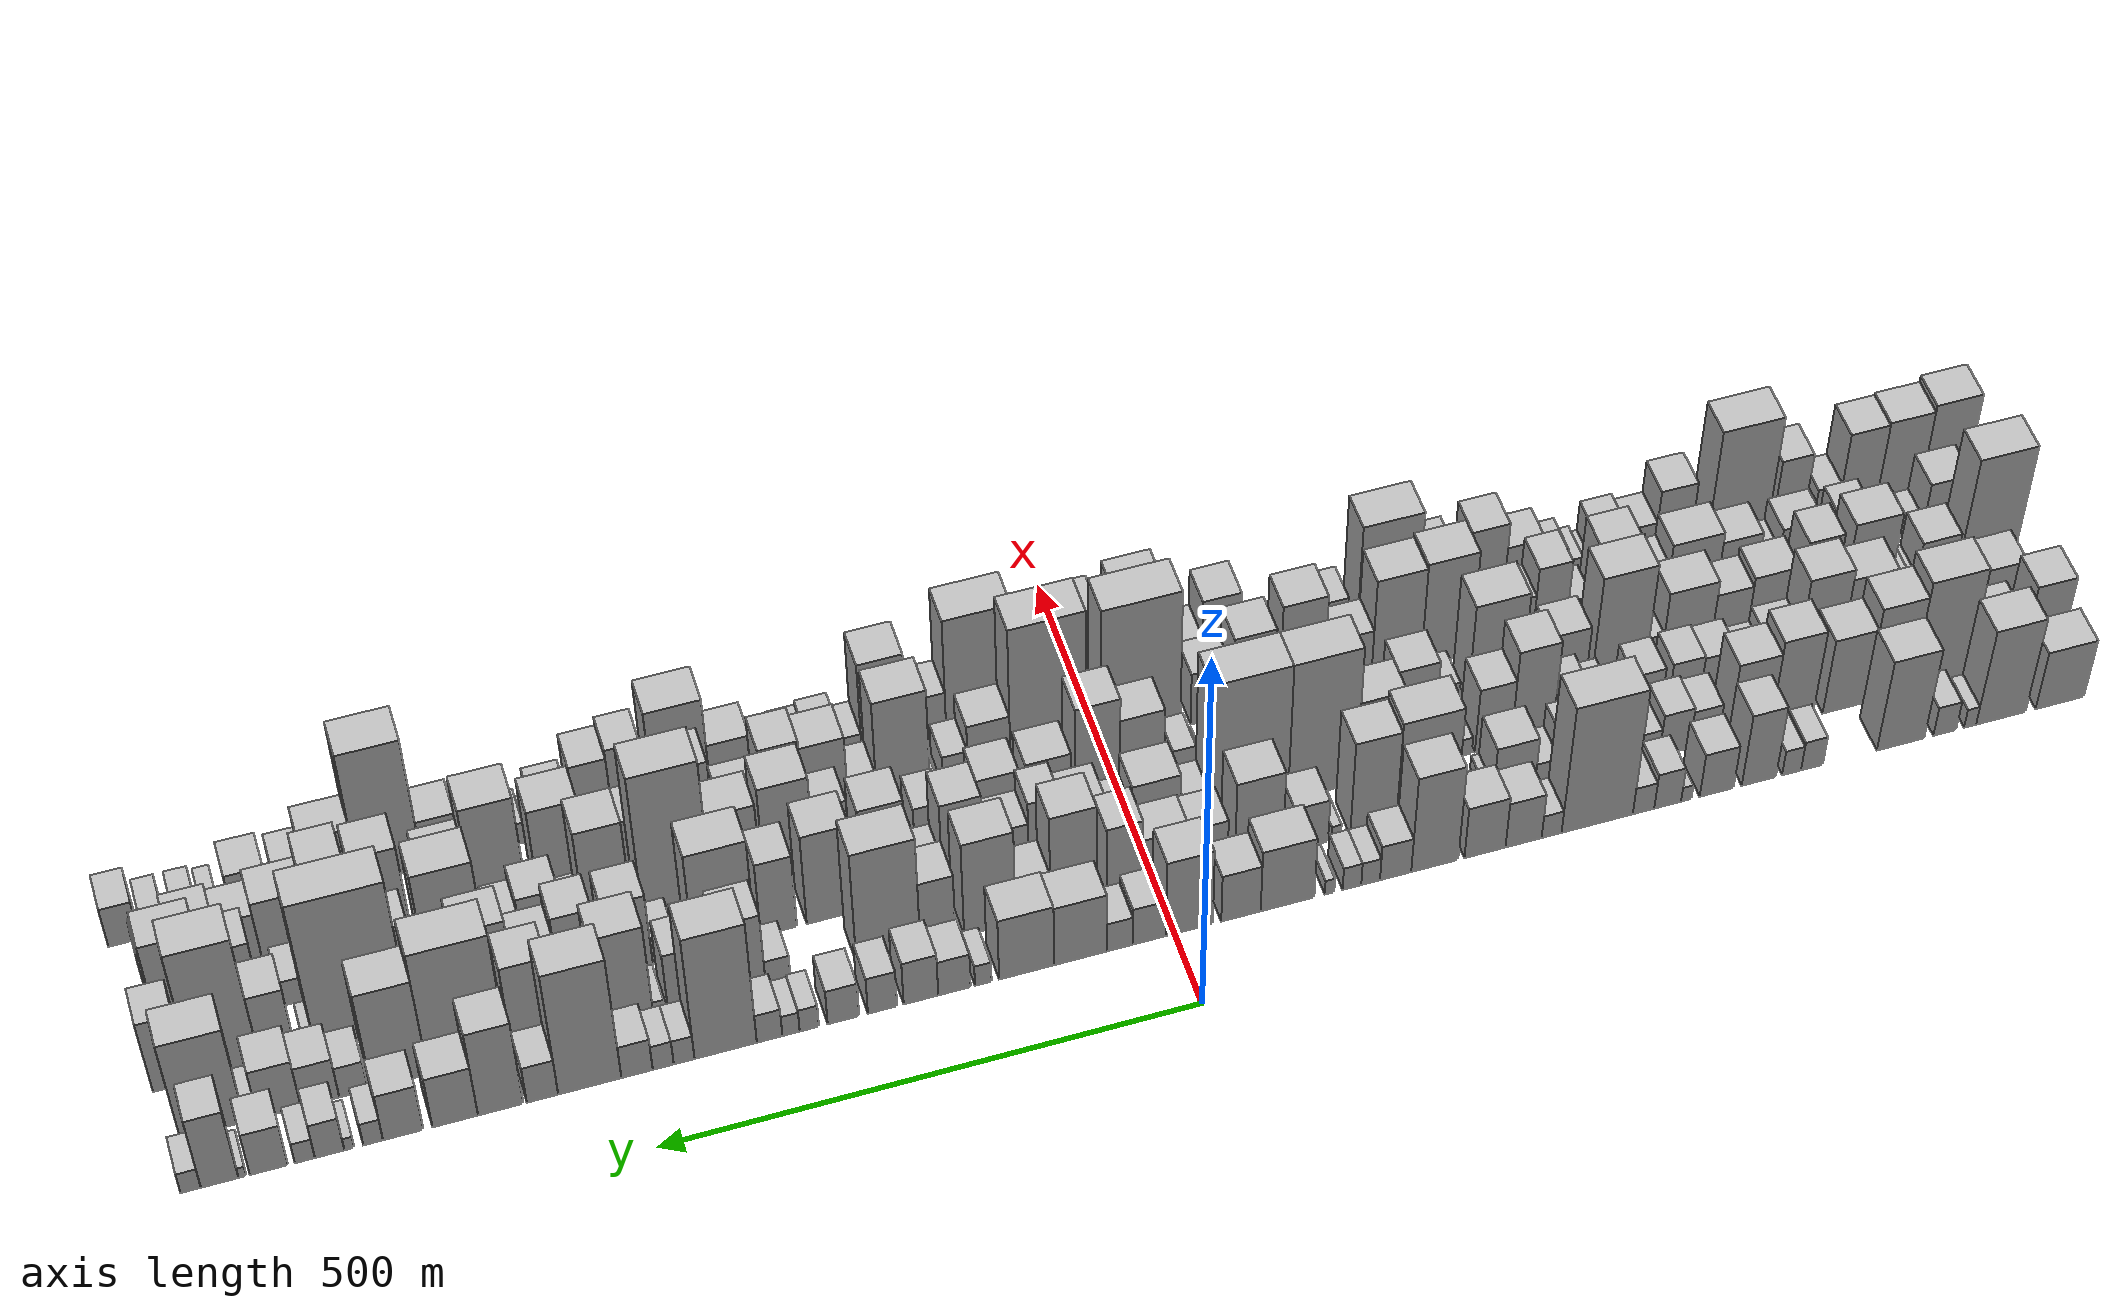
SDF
<sdf version="1.6">
 <world name="default">
  <scene>
   <sky><clouds><speed>12</speed></clouds></sky>
   <ambient>0.4 0.4 0.4 1</ambient>
   <background>0.7 0.7 0.7 1</background>
   <shadows>1</shadows>
  </scene>
  <gravity>0 0 -9.8066</gravity>
  <magnetic_field>6e-06 2.3e-05 -4.2e-05</magnetic_field>
  <physics default="0" name="default_physics" type="ode">
   <ode>
    <solver>
     <type>quick</type>
     <iters>10</iters>
     <sor>1.0</sor>
     <use_dynamic_moi_rescaling>0</use_dynamic_moi_rescaling>
    </solver>
    <constraints>
     <cfm>0</cfm>
     <erp>0.2</erp>
     <contact_max_correcting_vel>100</contact_max_correcting_vel>
     <contact_surface_layer>0.001</contact_surface_layer>
    </constraints>
   </ode>
   <max_step_size>0.004</max_step_size>
   <real_time_factor>1</real_time_factor>
   <real_time_update_rate>250</real_time_update_rate>
  </physics>
  <light name="sun" type="directional">
   <pose>0 0 10 0 0 0</pose>
   <diffuse>0.8 0.8 0.8 1</diffuse>
   <specular>0.2 0.2 0.2 1</specular>
   <attenuation>
    <range>1000</range>
    <constant>0.9</constant>
    <linear>0.01</linear>
    <quadratic>0.001</quadratic>
   </attenuation>
   <direction>-0.5 0.1 -0.9</direction>
  </light>
  <model name="building_1">
   <static>1</static>
   <pose>100.0000 -865.4337 0 0.000000 0.000000 0.000000</pose>
   <link name="link">
    <pose>0 0 42.00 0 0 0</pose>
    <collision name="collision"><geometry><box><size>40.0000 49.1326 84.0000</size></box></geometry></collision>
    <visual name="visual">
     <cast_shadows>0</cast_shadows>
     <geometry><box><size>40.0000 49.1326 84.0000</size></box></geometry>
     <material>
      <script>
       <uri>model://HANNAS_wall/materials/scripts</uri>
       <uri>model://HANNAS_wall/materials/textures</uri>
       <name>vrc/HANNAS_wall</name>
      </script>
     </material>
    </visual>
   </link>
  </model>
  <model name="building_2">
   <static>1</static>
   <pose>100.0000 -805.9090 0 0.000000 0.000000 0.000000</pose>
   <link name="link">
    <pose>0 0 69.00 0 0 0</pose>
    <collision name="collision"><geometry><box><size>40.0000 49.9168 138.0000</size></box></geometry></collision>
    <visual name="visual">
     <cast_shadows>0</cast_shadows>
     <geometry><box><size>40.0000 49.9168 138.0000</size></box></geometry>
     <material>
      <script>
       <uri>model://HANNAS_wall/materials/scripts</uri>
       <uri>model://HANNAS_wall/materials/textures</uri>
       <name>vrc/HANNAS_wall</name>
      </script>
     </material>
    </visual>
   </link>
  </model>
  <model name="building_3">
   <static>1</static>
   <pose>100.0000 -774.8887 0 0.000000 0.000000 0.000000</pose>
   <link name="link">
    <pose>0 0 13.50 0 0 0</pose>
    <collision name="collision"><geometry><box><size>40.0000 12.1238 27.0000</size></box></geometry></collision>
    <visual name="visual">
     <cast_shadows>0</cast_shadows>
     <geometry><box><size>40.0000 12.1238 27.0000</size></box></geometry>
     <material>
      <script>
       <uri>model://HANNAS_wall/materials/scripts</uri>
       <uri>model://HANNAS_wall/materials/textures</uri>
       <name>vrc/HANNAS_wall</name>
      </script>
     </material>
    </visual>
   </link>
  </model>
  <model name="building_4">
   <static>1</static>
   <pose>100.0000 -749.3840 0 0.000000 0.000000 0.000000</pose>
   <link name="link">
    <pose>0 0 21.00 0 0 0</pose>
    <collision name="collision"><geometry><box><size>40.0000 22.8857 42.0000</size></box></geometry></collision>
    <visual name="visual">
     <cast_shadows>0</cast_shadows>
     <geometry><box><size>40.0000 22.8857 42.0000</size></box></geometry>
     <material>
      <script>
       <uri>model://HANNAS_wall/materials/scripts</uri>
       <uri>model://HANNAS_wall/materials/textures</uri>
       <name>vrc/HANNAS_wall</name>
      </script>
     </material>
    </visual>
   </link>
  </model>
  <model name="building_5">
   <static>1</static>
   <pose>100.0000 -705.1346 0 0.000000 0.000000 0.000000</pose>
   <link name="link">
    <pose>0 0 66.00 0 0 0</pose>
    <collision name="collision"><geometry><box><size>40.0000 47.6131 132.0000</size></box></geometry></collision>
    <visual name="visual">
     <cast_shadows>0</cast_shadows>
     <geometry><box><size>40.0000 47.6131 132.0000</size></box></geometry>
     <material>
      <script>
       <uri>model://HANNAS_wall/materials/scripts</uri>
       <uri>model://HANNAS_wall/materials/textures</uri>
       <name>vrc/HANNAS_wall</name>
      </script>
     </material>
    </visual>
   </link>
  </model>
  <model name="building_6">
   <static>1</static>
   <pose>100.0000 -616.7171 0 0.000000 0.000000 0.000000</pose>
   <link name="link">
    <pose>0 0 21.00 0 0 0</pose>
    <collision name="collision"><geometry><box><size>40.0000 21.7406 42.0000</size></box></geometry></collision>
    <visual name="visual">
     <cast_shadows>0</cast_shadows>
     <geometry><box><size>40.0000 21.7406 42.0000</size></box></geometry>
     <material>
      <script>
       <uri>model://HANNAS_wall/materials/scripts</uri>
       <uri>model://HANNAS_wall/materials/textures</uri>
       <name>vrc/HANNAS_wall</name>
      </script>
     </material>
    </visual>
   </link>
  </model>
  <model name="building_7">
   <static>1</static>
   <pose>100.0000 -596.4582 0 0.000000 0.000000 0.000000</pose>
   <link name="link">
    <pose>0 0 18.00 0 0 0</pose>
    <collision name="collision"><geometry><box><size>40.0000 18.7772 36.0000</size></box></geometry></collision>
    <visual name="visual">
     <cast_shadows>0</cast_shadows>
     <geometry><box><size>40.0000 18.7772 36.0000</size></box></geometry>
     <material>
      <script>
       <uri>model://HANNAS_wall/materials/scripts</uri>
       <uri>model://HANNAS_wall/materials/textures</uri>
       <name>vrc/HANNAS_wall</name>
      </script>
     </material>
    </visual>
   </link>
  </model>
  <model name="building_8">
   <static>1</static>
   <pose>100.0000 -564.1123 0 0.000000 0.000000 0.000000</pose>
   <link name="link">
    <pose>0 0 52.50 0 0 0</pose>
    <collision name="collision"><geometry><box><size>40.0000 33.9147 105.0000</size></box></geometry></collision>
    <visual name="visual">
     <cast_shadows>0</cast_shadows>
     <geometry><box><size>40.0000 33.9147 105.0000</size></box></geometry>
     <material>
      <script>
       <uri>model://HANNAS_wall/materials/scripts</uri>
       <uri>model://HANNAS_wall/materials/textures</uri>
       <name>vrc/HANNAS_wall</name>
      </script>
     </material>
    </visual>
   </link>
  </model>
  <model name="building_9">
   <static>1</static>
   <pose>100.0000 -522.4168 0 0.000000 0.000000 0.000000</pose>
   <link name="link">
    <pose>0 0 31.50 0 0 0</pose>
    <collision name="collision"><geometry><box><size>40.0000 33.4762 63.0000</size></box></geometry></collision>
    <visual name="visual">
     <cast_shadows>0</cast_shadows>
     <geometry><box><size>40.0000 33.4762 63.0000</size></box></geometry>
     <material>
      <script>
       <uri>model://HANNAS_wall/materials/scripts</uri>
       <uri>model://HANNAS_wall/materials/textures</uri>
       <name>vrc/HANNAS_wall</name>
      </script>
     </material>
    </visual>
   </link>
  </model>
  <model name="building_10">
   <static>1</static>
   <pose>100.0000 -492.5437 0 0.000000 0.000000 0.000000</pose>
   <link name="link">
    <pose>0 0 10.50 0 0 0</pose>
    <collision name="collision"><geometry><box><size>40.0000 10.2700 21.0000</size></box></geometry></collision>
    <visual name="visual">
     <cast_shadows>0</cast_shadows>
     <geometry><box><size>40.0000 10.2700 21.0000</size></box></geometry>
     <material>
      <script>
       <uri>model://HANNAS_wall/materials/scripts</uri>
       <uri>model://HANNAS_wall/materials/textures</uri>
       <name>vrc/HANNAS_wall</name>
      </script>
     </material>
    </visual>
   </link>
  </model>
  <model name="building_11">
   <static>1</static>
   <pose>100.0000 -474.2443 0 0.000000 0.000000 0.000000</pose>
   <link name="link">
    <pose>0 0 25.50 0 0 0</pose>
    <collision name="collision"><geometry><box><size>40.0000 26.3288 51.0000</size></box></geometry></collision>
    <visual name="visual">
     <cast_shadows>0</cast_shadows>
     <geometry><box><size>40.0000 26.3288 51.0000</size></box></geometry>
     <material>
      <script>
       <uri>model://HANNAS_wall/materials/scripts</uri>
       <uri>model://HANNAS_wall/materials/textures</uri>
       <name>vrc/HANNAS_wall</name>
      </script>
     </material>
    </visual>
   </link>
  </model>
  <model name="building_12">
   <static>1</static>
   <pose>100.0000 -450.5782 0 0.000000 0.000000 0.000000</pose>
   <link name="link">
    <pose>0 0 19.50 0 0 0</pose>
    <collision name="collision"><geometry><box><size>40.0000 21.0034 39.0000</size></box></geometry></collision>
    <visual name="visual">
     <cast_shadows>0</cast_shadows>
     <geometry><box><size>40.0000 21.0034 39.0000</size></box></geometry>
     <material>
      <script>
       <uri>model://HANNAS_wall/materials/scripts</uri>
       <uri>model://HANNAS_wall/materials/textures</uri>
       <name>vrc/HANNAS_wall</name>
      </script>
     </material>
    </visual>
   </link>
  </model>
  <model name="building_13">
   <static>1</static>
   <pose>100.0000 -405.2971 0 0.000000 0.000000 0.000000</pose>
   <link name="link">
    <pose>0 0 93.00 0 0 0</pose>
    <collision name="collision"><geometry><box><size>40.0000 69.5590 186.0000</size></box></geometry></collision>
    <visual name="visual">
     <cast_shadows>0</cast_shadows>
     <geometry><box><size>40.0000 69.5590 186.0000</size></box></geometry>
     <material>
      <script>
       <uri>model://HANNAS_wall/materials/scripts</uri>
       <uri>model://HANNAS_wall/materials/textures</uri>
       <name>vrc/HANNAS_wall</name>
      </script>
     </material>
    </visual>
   </link>
  </model>
  <model name="building_14">
   <static>1</static>
   <pose>100.0000 -360.7872 0 0.000000 0.000000 0.000000</pose>
   <link name="link">
    <pose>0 0 16.50 0 0 0</pose>
    <collision name="collision"><geometry><box><size>40.0000 19.4608 33.0000</size></box></geometry></collision>
    <visual name="visual">
     <cast_shadows>0</cast_shadows>
     <geometry><box><size>40.0000 19.4608 33.0000</size></box></geometry>
     <material>
      <script>
       <uri>model://HANNAS_wall/materials/scripts</uri>
       <uri>model://HANNAS_wall/materials/textures</uri>
       <name>vrc/HANNAS_wall</name>
      </script>
     </material>
    </visual>
   </link>
  </model>
  <model name="building_15">
   <static>1</static>
   <pose>100.0000 -333.5483 0 0.000000 0.000000 0.000000</pose>
   <link name="link">
    <pose>0 0 33.00 0 0 0</pose>
    <collision name="collision"><geometry><box><size>40.0000 35.0169 66.0000</size></box></geometry></collision>
    <visual name="visual">
     <cast_shadows>0</cast_shadows>
     <geometry><box><size>40.0000 35.0169 66.0000</size></box></geometry>
     <material>
      <script>
       <uri>model://HANNAS_wall/materials/scripts</uri>
       <uri>model://HANNAS_wall/materials/textures</uri>
       <name>vrc/HANNAS_wall</name>
      </script>
     </material>
    </visual>
   </link>
  </model>
  <model name="building_16">
   <static>1</static>
   <pose>100.0000 -296.1378 0 0.000000 0.000000 0.000000</pose>
   <link name="link">
    <pose>0 0 37.50 0 0 0</pose>
    <collision name="collision"><geometry><box><size>40.0000 39.8042 75.0000</size></box></geometry></collision>
    <visual name="visual">
     <cast_shadows>0</cast_shadows>
     <geometry><box><size>40.0000 39.8042 75.0000</size></box></geometry>
     <material>
      <script>
       <uri>model://HANNAS_wall/materials/scripts</uri>
       <uri>model://HANNAS_wall/materials/textures</uri>
       <name>vrc/HANNAS_wall</name>
      </script>
     </material>
    </visual>
   </link>
  </model>
  <model name="building_17">
   <static>1</static>
   <pose>100.0000 -247.5709 0 0.000000 0.000000 0.000000</pose>
   <link name="link">
    <pose>0 0 70.50 0 0 0</pose>
    <collision name="collision"><geometry><box><size>40.0000 45.3294 141.0000</size></box></geometry></collision>
    <visual name="visual">
     <cast_shadows>0</cast_shadows>
     <geometry><box><size>40.0000 45.3294 141.0000</size></box></geometry>
     <material>
      <script>
       <uri>model://HANNAS_wall/materials/scripts</uri>
       <uri>model://HANNAS_wall/materials/textures</uri>
       <name>vrc/HANNAS_wall</name>
      </script>
     </material>
    </visual>
   </link>
  </model>
  <model name="building_18">
   <static>1</static>
   <pose>100.0000 -209.9071 0 0.000000 0.000000 0.000000</pose>
   <link name="link">
    <pose>0 0 25.50 0 0 0</pose>
    <collision name="collision"><geometry><box><size>40.0000 29.9982 51.0000</size></box></geometry></collision>
    <visual name="visual">
     <cast_shadows>0</cast_shadows>
     <geometry><box><size>40.0000 29.9982 51.0000</size></box></geometry>
     <material>
      <script>
       <uri>model://HANNAS_wall/materials/scripts</uri>
       <uri>model://HANNAS_wall/materials/textures</uri>
       <name>vrc/HANNAS_wall</name>
      </script>
     </material>
    </visual>
   </link>
  </model>
  <model name="building_19">
   <static>1</static>
   <pose>100.0000 -185.9173 0 0.000000 0.000000 0.000000</pose>
   <link name="link">
    <pose>0 0 16.50 0 0 0</pose>
    <collision name="collision"><geometry><box><size>40.0000 17.9815 33.0000</size></box></geometry></collision>
    <visual name="visual">
     <cast_shadows>0</cast_shadows>
     <geometry><box><size>40.0000 17.9815 33.0000</size></box></geometry>
     <material>
      <script>
       <uri>model://HANNAS_wall/materials/scripts</uri>
       <uri>model://HANNAS_wall/materials/textures</uri>
       <name>vrc/HANNAS_wall</name>
      </script>
     </material>
    </visual>
   </link>
  </model>
  <model name="building_20">
   <static>1</static>
   <pose>100.0000 -167.9910 0 0.000000 0.000000 0.000000</pose>
   <link name="link">
    <pose>0 0 16.50 0 0 0</pose>
    <collision name="collision"><geometry><box><size>40.0000 17.8710 33.0000</size></box></geometry></collision>
    <visual name="visual">
     <cast_shadows>0</cast_shadows>
     <geometry><box><size>40.0000 17.8710 33.0000</size></box></geometry>
     <material>
      <script>
       <uri>model://HANNAS_wall/materials/scripts</uri>
       <uri>model://HANNAS_wall/materials/textures</uri>
       <name>vrc/HANNAS_wall</name>
      </script>
     </material>
    </visual>
   </link>
  </model>
  <model name="building_21">
   <static>1</static>
   <pose>100.0000 -146.5413 0 0.000000 0.000000 0.000000</pose>
   <link name="link">
    <pose>0 0 10.50 0 0 0</pose>
    <collision name="collision"><geometry><box><size>40.0000 9.0284 21.0000</size></box></geometry></collision>
    <visual name="visual">
     <cast_shadows>0</cast_shadows>
     <geometry><box><size>40.0000 9.0284 21.0000</size></box></geometry>
     <material>
      <script>
       <uri>model://HANNAS_wall/materials/scripts</uri>
       <uri>model://HANNAS_wall/materials/textures</uri>
       <name>vrc/HANNAS_wall</name>
      </script>
     </material>
    </visual>
   </link>
  </model>
  <model name="building_22">
   <static>1</static>
   <pose>100.0000 -106.4332 0 0.000000 0.000000 0.000000</pose>
   <link name="link">
    <pose>0 0 45.00 0 0 0</pose>
    <collision name="collision"><geometry><box><size>40.0000 51.1879 90.0000</size></box></geometry></collision>
    <visual name="visual">
     <cast_shadows>0</cast_shadows>
     <geometry><box><size>40.0000 51.1879 90.0000</size></box></geometry>
     <material>
      <script>
       <uri>model://HANNAS_wall/materials/scripts</uri>
       <uri>model://HANNAS_wall/materials/textures</uri>
       <name>vrc/HANNAS_wall</name>
      </script>
     </material>
    </visual>
   </link>
  </model>
  <model name="building_23">
   <static>1</static>
   <pose>100.0000 -62.1196 0 0.000000 0.000000 0.000000</pose>
   <link name="link">
    <pose>0 0 34.50 0 0 0</pose>
    <collision name="collision"><geometry><box><size>40.0000 37.4392 69.0000</size></box></geometry></collision>
    <visual name="visual">
     <cast_shadows>0</cast_shadows>
     <geometry><box><size>40.0000 37.4392 69.0000</size></box></geometry>
     <material>
      <script>
       <uri>model://HANNAS_wall/materials/scripts</uri>
       <uri>model://HANNAS_wall/materials/textures</uri>
       <name>vrc/HANNAS_wall</name>
      </script>
     </material>
    </visual>
   </link>
  </model>
  <model name="building_24">
   <static>1</static>
   <pose>100.0000 -13.4017 0 0.000000 0.000000 0.000000</pose>
   <link name="link">
    <pose>0 0 55.50 0 0 0</pose>
    <collision name="collision"><geometry><box><size>40.0000 43.9966 111.0000</size></box></geometry></collision>
    <visual name="visual">
     <cast_shadows>0</cast_shadows>
     <geometry><box><size>40.0000 43.9966 111.0000</size></box></geometry>
     <material>
      <script>
       <uri>model://HANNAS_wall/materials/scripts</uri>
       <uri>model://HANNAS_wall/materials/textures</uri>
       <name>vrc/HANNAS_wall</name>
      </script>
     </material>
    </visual>
   </link>
  </model>
  <model name="building_25">
   <static>1</static>
   <pose>100.0000 24.3123 0 0.000000 0.000000 0.000000</pose>
   <link name="link">
    <pose>0 0 27.00 0 0 0</pose>
    <collision name="collision"><geometry><box><size>40.0000 31.4314 54.0000</size></box></geometry></collision>
    <visual name="visual">
     <cast_shadows>0</cast_shadows>
     <geometry><box><size>40.0000 31.4314 54.0000</size></box></geometry>
     <material>
      <script>
       <uri>model://HANNAS_wall/materials/scripts</uri>
       <uri>model://HANNAS_wall/materials/textures</uri>
       <name>vrc/HANNAS_wall</name>
      </script>
     </material>
    </visual>
   </link>
  </model>
  <model name="building_26">
   <static>1</static>
   <pose>100.0000 52.2416 0 0.000000 0.000000 0.000000</pose>
   <link name="link">
    <pose>0 0 21.00 0 0 0</pose>
    <collision name="collision"><geometry><box><size>40.0000 24.4274 42.0000</size></box></geometry></collision>
    <visual name="visual">
     <cast_shadows>0</cast_shadows>
     <geometry><box><size>40.0000 24.4274 42.0000</size></box></geometry>
     <material>
      <script>
       <uri>model://HANNAS_wall/materials/scripts</uri>
       <uri>model://HANNAS_wall/materials/textures</uri>
       <name>vrc/HANNAS_wall</name>
      </script>
     </material>
    </visual>
   </link>
  </model>
  <model name="building_27">
   <static>1</static>
   <pose>100.0000 89.1585 0 0.000000 0.000000 0.000000</pose>
   <link name="link">
    <pose>0 0 43.50 0 0 0</pose>
    <collision name="collision"><geometry><box><size>40.0000 49.4064 87.0000</size></box></geometry></collision>
    <visual name="visual">
     <cast_shadows>0</cast_shadows>
     <geometry><box><size>40.0000 49.4064 87.0000</size></box></geometry>
     <material>
      <script>
       <uri>model://HANNAS_wall/materials/scripts</uri>
       <uri>model://HANNAS_wall/materials/textures</uri>
       <name>vrc/HANNAS_wall</name>
      </script>
     </material>
    </visual>
   </link>
  </model>
  <model name="building_28">
   <static>1</static>
   <pose>100.0000 139.6292 0 0.000000 0.000000 0.000000</pose>
   <link name="link">
    <pose>0 0 45.00 0 0 0</pose>
    <collision name="collision"><geometry><box><size>40.0000 51.5349 90.0000</size></box></geometry></collision>
    <visual name="visual">
     <cast_shadows>0</cast_shadows>
     <geometry><box><size>40.0000 51.5349 90.0000</size></box></geometry>
     <material>
      <script>
       <uri>model://HANNAS_wall/materials/scripts</uri>
       <uri>model://HANNAS_wall/materials/textures</uri>
       <name>vrc/HANNAS_wall</name>
      </script>
     </material>
    </visual>
   </link>
  </model>
  <model name="building_29">
   <static>1</static>
   <pose>100.0000 180.1665 0 0.000000 0.000000 0.000000</pose>
   <link name="link">
    <pose>0 0 15.00 0 0 0</pose>
    <collision name="collision"><geometry><box><size>40.0000 15.5398 30.0000</size></box></geometry></collision>
    <visual name="visual">
     <cast_shadows>0</cast_shadows>
     <geometry><box><size>40.0000 15.5398 30.0000</size></box></geometry>
     <material>
      <script>
       <uri>model://HANNAS_wall/materials/scripts</uri>
       <uri>model://HANNAS_wall/materials/textures</uri>
       <name>vrc/HANNAS_wall</name>
      </script>
     </material>
    </visual>
   </link>
  </model>
  <model name="building_30">
   <static>1</static>
   <pose>100.0000 206.9516 0 0.000000 0.000000 0.000000</pose>
   <link name="link">
    <pose>0 0 25.50 0 0 0</pose>
    <collision name="collision"><geometry><box><size>40.0000 30.0303 51.0000</size></box></geometry></collision>
    <visual name="visual">
     <cast_shadows>0</cast_shadows>
     <geometry><box><size>40.0000 30.0303 51.0000</size></box></geometry>
     <material>
      <script>
       <uri>model://HANNAS_wall/materials/scripts</uri>
       <uri>model://HANNAS_wall/materials/textures</uri>
       <name>vrc/HANNAS_wall</name>
      </script>
     </material>
    </visual>
   </link>
  </model>
  <model name="building_31">
   <static>1</static>
   <pose>100.0000 238.0096 0 0.000000 0.000000 0.000000</pose>
   <link name="link">
    <pose>0 0 31.50 0 0 0</pose>
    <collision name="collision"><geometry><box><size>40.0000 32.0857 63.0000</size></box></geometry></collision>
    <visual name="visual">
     <cast_shadows>0</cast_shadows>
     <geometry><box><size>40.0000 32.0857 63.0000</size></box></geometry>
     <material>
      <script>
       <uri>model://HANNAS_wall/materials/scripts</uri>
       <uri>model://HANNAS_wall/materials/textures</uri>
       <name>vrc/HANNAS_wall</name>
      </script>
     </material>
    </visual>
   </link>
  </model>
  <model name="building_32">
   <static>1</static>
   <pose>100.0000 273.5645 0 0.000000 0.000000 0.000000</pose>
   <link name="link">
    <pose>0 0 27.00 0 0 0</pose>
    <collision name="collision"><geometry><box><size>40.0000 27.0241 54.0000</size></box></geometry></collision>
    <visual name="visual">
     <cast_shadows>0</cast_shadows>
     <geometry><box><size>40.0000 27.0241 54.0000</size></box></geometry>
     <material>
      <script>
       <uri>model://HANNAS_wall/materials/scripts</uri>
       <uri>model://HANNAS_wall/materials/textures</uri>
       <name>vrc/HANNAS_wall</name>
      </script>
     </material>
    </visual>
   </link>
  </model>
  <model name="building_33">
   <static>1</static>
   <pose>100.0000 309.6315 0 0.000000 0.000000 0.000000</pose>
   <link name="link">
    <pose>0 0 25.50 0 0 0</pose>
    <collision name="collision"><geometry><box><size>40.0000 29.1099 51.0000</size></box></geometry></collision>
    <visual name="visual">
     <cast_shadows>0</cast_shadows>
     <geometry><box><size>40.0000 29.1099 51.0000</size></box></geometry>
     <material>
      <script>
       <uri>model://HANNAS_wall/materials/scripts</uri>
       <uri>model://HANNAS_wall/materials/textures</uri>
       <name>vrc/HANNAS_wall</name>
      </script>
     </material>
    </visual>
   </link>
  </model>
  <model name="building_34">
   <static>1</static>
   <pose>100.0000 341.0101 0 0.000000 0.000000 0.000000</pose>
   <link name="link">
    <pose>0 0 16.50 0 0 0</pose>
    <collision name="collision"><geometry><box><size>40.0000 17.6474 33.0000</size></box></geometry></collision>
    <visual name="visual">
     <cast_shadows>0</cast_shadows>
     <geometry><box><size>40.0000 17.6474 33.0000</size></box></geometry>
     <material>
      <script>
       <uri>model://HANNAS_wall/materials/scripts</uri>
       <uri>model://HANNAS_wall/materials/textures</uri>
       <name>vrc/HANNAS_wall</name>
      </script>
     </material>
    </visual>
   </link>
  </model>
  <model name="building_35">
   <static>1</static>
   <pose>100.0000 357.7709 0 0.000000 0.000000 0.000000</pose>
   <link name="link">
    <pose>0 0 15.00 0 0 0</pose>
    <collision name="collision"><geometry><box><size>40.0000 15.8742 30.0000</size></box></geometry></collision>
    <visual name="visual">
     <cast_shadows>0</cast_shadows>
     <geometry><box><size>40.0000 15.8742 30.0000</size></box></geometry>
     <material>
      <script>
       <uri>model://HANNAS_wall/materials/scripts</uri>
       <uri>model://HANNAS_wall/materials/textures</uri>
       <name>vrc/HANNAS_wall</name>
      </script>
     </material>
    </visual>
   </link>
  </model>
  <model name="building_36">
   <static>1</static>
   <pose>100.0000 377.3944 0 0.000000 0.000000 0.000000</pose>
   <link name="link">
    <pose>0 0 21.00 0 0 0</pose>
    <collision name="collision"><geometry><box><size>40.0000 23.3728 42.0000</size></box></geometry></collision>
    <visual name="visual">
     <cast_shadows>0</cast_shadows>
     <geometry><box><size>40.0000 23.3728 42.0000</size></box></geometry>
     <material>
      <script>
       <uri>model://HANNAS_wall/materials/scripts</uri>
       <uri>model://HANNAS_wall/materials/textures</uri>
       <name>vrc/HANNAS_wall</name>
      </script>
     </material>
    </visual>
   </link>
  </model>
  <model name="building_37">
   <static>1</static>
   <pose>100.0000 417.5311 0 0.000000 0.000000 0.000000</pose>
   <link name="link">
    <pose>0 0 91.50 0 0 0</pose>
    <collision name="collision"><geometry><box><size>40.0000 56.9005 183.0000</size></box></geometry></collision>
    <visual name="visual">
     <cast_shadows>0</cast_shadows>
     <geometry><box><size>40.0000 56.9005 183.0000</size></box></geometry>
     <material>
      <script>
       <uri>model://HANNAS_wall/materials/scripts</uri>
       <uri>model://HANNAS_wall/materials/textures</uri>
       <name>vrc/HANNAS_wall</name>
      </script>
     </material>
    </visual>
   </link>
  </model>
  <model name="building_38">
   <static>1</static>
   <pose>100.0000 455.4224 0 0.000000 0.000000 0.000000</pose>
   <link name="link">
    <pose>0 0 18.00 0 0 0</pose>
    <collision name="collision"><geometry><box><size>40.0000 18.8821 36.0000</size></box></geometry></collision>
    <visual name="visual">
     <cast_shadows>0</cast_shadows>
     <geometry><box><size>40.0000 18.8821 36.0000</size></box></geometry>
     <material>
      <script>
       <uri>model://HANNAS_wall/materials/scripts</uri>
       <uri>model://HANNAS_wall/materials/textures</uri>
       <name>vrc/HANNAS_wall</name>
      </script>
     </material>
    </visual>
   </link>
  </model>
  <model name="building_39">
   <static>1</static>
   <pose>100.0000 474.3884 0 0.000000 0.000000 0.000000</pose>
   <link name="link">
    <pose>0 0 18.00 0 0 0</pose>
    <collision name="collision"><geometry><box><size>40.0000 19.0501 36.0000</size></box></geometry></collision>
    <visual name="visual">
     <cast_shadows>0</cast_shadows>
     <geometry><box><size>40.0000 19.0501 36.0000</size></box></geometry>
     <material>
      <script>
       <uri>model://HANNAS_wall/materials/scripts</uri>
       <uri>model://HANNAS_wall/materials/textures</uri>
       <name>vrc/HANNAS_wall</name>
      </script>
     </material>
    </visual>
   </link>
  </model>
  <model name="building_40">
   <static>1</static>
   <pose>100.0000 498.1025 0 0.000000 0.000000 0.000000</pose>
   <link name="link">
    <pose>0 0 24.00 0 0 0</pose>
    <collision name="collision"><geometry><box><size>40.0000 28.3781 48.0000</size></box></geometry></collision>
    <visual name="visual">
     <cast_shadows>0</cast_shadows>
     <geometry><box><size>40.0000 28.3781 48.0000</size></box></geometry>
     <material>
      <script>
       <uri>model://HANNAS_wall/materials/scripts</uri>
       <uri>model://HANNAS_wall/materials/textures</uri>
       <name>vrc/HANNAS_wall</name>
      </script>
     </material>
    </visual>
   </link>
  </model>
  <model name="building_41">
   <static>1</static>
   <pose>100.0000 540.8449 0 0.000000 0.000000 0.000000</pose>
   <link name="link">
    <pose>0 0 91.50 0 0 0</pose>
    <collision name="collision"><geometry><box><size>40.0000 57.1067 183.0000</size></box></geometry></collision>
    <visual name="visual">
     <cast_shadows>0</cast_shadows>
     <geometry><box><size>40.0000 57.1067 183.0000</size></box></geometry>
     <material>
      <script>
       <uri>model://HANNAS_wall/materials/scripts</uri>
       <uri>model://HANNAS_wall/materials/textures</uri>
       <name>vrc/HANNAS_wall</name>
      </script>
     </material>
    </visual>
   </link>
  </model>
  <model name="building_42">
   <static>1</static>
   <pose>100.0000 583.5705 0 0.000000 0.000000 0.000000</pose>
   <link name="link">
    <pose>0 0 27.00 0 0 0</pose>
    <collision name="collision"><geometry><box><size>40.0000 28.3445 54.0000</size></box></geometry></collision>
    <visual name="visual">
     <cast_shadows>0</cast_shadows>
     <geometry><box><size>40.0000 28.3445 54.0000</size></box></geometry>
     <material>
      <script>
       <uri>model://HANNAS_wall/materials/scripts</uri>
       <uri>model://HANNAS_wall/materials/textures</uri>
       <name>vrc/HANNAS_wall</name>
      </script>
     </material>
    </visual>
   </link>
  </model>
  <model name="building_43">
   <static>1</static>
   <pose>100.0000 621.0852 0 0.000000 0.000000 0.000000</pose>
   <link name="link">
    <pose>0 0 63.00 0 0 0</pose>
    <collision name="collision"><geometry><box><size>40.0000 40.6848 126.0000</size></box></geometry></collision>
    <visual name="visual">
     <cast_shadows>0</cast_shadows>
     <geometry><box><size>40.0000 40.6848 126.0000</size></box></geometry>
     <material>
      <script>
       <uri>model://HANNAS_wall/materials/scripts</uri>
       <uri>model://HANNAS_wall/materials/textures</uri>
       <name>vrc/HANNAS_wall</name>
      </script>
     </material>
    </visual>
   </link>
  </model>
  <model name="building_44">
   <static>1</static>
   <pose>100.0000 661.8343 0 0.000000 0.000000 0.000000</pose>
   <link name="link">
    <pose>0 0 37.50 0 0 0</pose>
    <collision name="collision"><geometry><box><size>40.0000 40.8136 75.0000</size></box></geometry></collision>
    <visual name="visual">
     <cast_shadows>0</cast_shadows>
     <geometry><box><size>40.0000 40.8136 75.0000</size></box></geometry>
     <material>
      <script>
       <uri>model://HANNAS_wall/materials/scripts</uri>
       <uri>model://HANNAS_wall/materials/textures</uri>
       <name>vrc/HANNAS_wall</name>
      </script>
     </material>
    </visual>
   </link>
  </model>
  <model name="building_45">
   <static>1</static>
   <pose>100.0000 708.2543 0 0.000000 0.000000 0.000000</pose>
   <link name="link">
    <pose>0 0 34.50 0 0 0</pose>
    <collision name="collision"><geometry><box><size>40.0000 36.0265 69.0000</size></box></geometry></collision>
    <visual name="visual">
     <cast_shadows>0</cast_shadows>
     <geometry><box><size>40.0000 36.0265 69.0000</size></box></geometry>
     <material>
      <script>
       <uri>model://HANNAS_wall/materials/scripts</uri>
       <uri>model://HANNAS_wall/materials/textures</uri>
       <name>vrc/HANNAS_wall</name>
      </script>
     </material>
    </visual>
   </link>
  </model>
  <model name="building_46">
   <static>1</static>
   <pose>100.0000 735.0538 0 0.000000 0.000000 0.000000</pose>
   <link name="link">
    <pose>0 0 16.50 0 0 0</pose>
    <collision name="collision"><geometry><box><size>40.0000 17.5725 33.0000</size></box></geometry></collision>
    <visual name="visual">
     <cast_shadows>0</cast_shadows>
     <geometry><box><size>40.0000 17.5725 33.0000</size></box></geometry>
     <material>
      <script>
       <uri>model://HANNAS_wall/materials/scripts</uri>
       <uri>model://HANNAS_wall/materials/textures</uri>
       <name>vrc/HANNAS_wall</name>
      </script>
     </material>
    </visual>
   </link>
  </model>
  <model name="building_47">
   <static>1</static>
   <pose>100.0000 756.2226 0 0.000000 0.000000 0.000000</pose>
   <link name="link">
    <pose>0 0 9.00 0 0 0</pose>
    <collision name="collision"><geometry><box><size>40.0000 8.7650 18.0000</size></box></geometry></collision>
    <visual name="visual">
     <cast_shadows>0</cast_shadows>
     <geometry><box><size>40.0000 8.7650 18.0000</size></box></geometry>
     <material>
      <script>
       <uri>model://HANNAS_wall/materials/scripts</uri>
       <uri>model://HANNAS_wall/materials/textures</uri>
       <name>vrc/HANNAS_wall</name>
      </script>
     </material>
    </visual>
   </link>
  </model>
  <model name="building_48">
   <static>1</static>
   <pose>100.0000 773.6560 0 0.000000 0.000000 0.000000</pose>
   <link name="link">
    <pose>0 0 25.50 0 0 0</pose>
    <collision name="collision"><geometry><box><size>40.0000 26.1020 51.0000</size></box></geometry></collision>
    <visual name="visual">
     <cast_shadows>0</cast_shadows>
     <geometry><box><size>40.0000 26.1020 51.0000</size></box></geometry>
     <material>
      <script>
       <uri>model://HANNAS_wall/materials/scripts</uri>
       <uri>model://HANNAS_wall/materials/textures</uri>
       <name>vrc/HANNAS_wall</name>
      </script>
     </material>
    </visual>
   </link>
  </model>
  <model name="building_49">
   <static>1</static>
   <pose>100.0000 795.6062 0 0.000000 0.000000 0.000000</pose>
   <link name="link">
    <pose>0 0 15.00 0 0 0</pose>
    <collision name="collision"><geometry><box><size>40.0000 17.7983 30.0000</size></box></geometry></collision>
    <visual name="visual">
     <cast_shadows>0</cast_shadows>
     <geometry><box><size>40.0000 17.7983 30.0000</size></box></geometry>
     <material>
      <script>
       <uri>model://HANNAS_wall/materials/scripts</uri>
       <uri>model://HANNAS_wall/materials/textures</uri>
       <name>vrc/HANNAS_wall</name>
      </script>
     </material>
    </visual>
   </link>
  </model>
  <model name="building_50">
   <static>1</static>
   <pose>100.0000 827.3472 0 0.000000 0.000000 0.000000</pose>
   <link name="link">
    <pose>0 0 31.50 0 0 0</pose>
    <collision name="collision"><geometry><box><size>40.0000 33.6838 63.0000</size></box></geometry></collision>
    <visual name="visual">
     <cast_shadows>0</cast_shadows>
     <geometry><box><size>40.0000 33.6838 63.0000</size></box></geometry>
     <material>
      <script>
       <uri>model://HANNAS_wall/materials/scripts</uri>
       <uri>model://HANNAS_wall/materials/textures</uri>
       <name>vrc/HANNAS_wall</name>
      </script>
     </material>
    </visual>
   </link>
  </model>
  <model name="building_51">
   <static>1</static>
   <pose>100.0000 850.6374 0 0.000000 0.000000 0.000000</pose>
   <link name="link">
    <pose>0 0 7.50 0 0 0</pose>
    <collision name="collision"><geometry><box><size>40.0000 6.8966 15.0000</size></box></geometry></collision>
    <visual name="visual">
     <cast_shadows>0</cast_shadows>
     <geometry><box><size>40.0000 6.8966 15.0000</size></box></geometry>
     <material>
      <script>
       <uri>model://HANNAS_wall/materials/scripts</uri>
       <uri>model://HANNAS_wall/materials/textures</uri>
       <name>vrc/HANNAS_wall</name>
      </script>
     </material>
    </visual>
   </link>
  </model>
  <model name="building_52">
   <static>1</static>
   <pose>100.0000 870.6389 0 0.000000 0.000000 0.000000</pose>
   <link name="link">
    <pose>0 0 52.50 0 0 0</pose>
    <collision name="collision"><geometry><box><size>40.0000 33.1064 105.0000</size></box></geometry></collision>
    <visual name="visual">
     <cast_shadows>0</cast_shadows>
     <geometry><box><size>40.0000 33.1064 105.0000</size></box></geometry>
     <material>
      <script>
       <uri>model://HANNAS_wall/materials/scripts</uri>
       <uri>model://HANNAS_wall/materials/textures</uri>
       <name>vrc/HANNAS_wall</name>
      </script>
     </material>
    </visual>
   </link>
  </model>
  <model name="building_53">
   <static>1</static>
   <pose>100.0000 896.1446 0 0.000000 0.000000 0.000000</pose>
   <link name="link">
    <pose>0 0 15.00 0 0 0</pose>
    <collision name="collision"><geometry><box><size>40.0000 17.9050 30.0000</size></box></geometry></collision>
    <visual name="visual">
     <cast_shadows>0</cast_shadows>
     <geometry><box><size>40.0000 17.9050 30.0000</size></box></geometry>
     <material>
      <script>
       <uri>model://HANNAS_wall/materials/scripts</uri>
       <uri>model://HANNAS_wall/materials/textures</uri>
       <name>vrc/HANNAS_wall</name>
      </script>
     </material>
    </visual>
   </link>
  </model>
  <model name="building_54">
   <static>1</static>
   <pose>155.0000 -870.3266 0 0.000000 0.000000 0.000000</pose>
   <link name="link">
    <pose>0 0 55.50 0 0 0</pose>
    <collision name="collision"><geometry><box><size>40.0000 39.3467 111.0000</size></box></geometry></collision>
    <visual name="visual">
     <cast_shadows>0</cast_shadows>
     <geometry><box><size>40.0000 39.3467 111.0000</size></box></geometry>
     <material>
      <script>
       <uri>model://HANNAS_wall/materials/scripts</uri>
       <uri>model://HANNAS_wall/materials/textures</uri>
       <name>vrc/HANNAS_wall</name>
      </script>
     </material>
    </visual>
   </link>
  </model>
  <model name="building_55">
   <static>1</static>
   <pose>155.0000 -817.9297 0 0.000000 0.000000 0.000000</pose>
   <link name="link">
    <pose>0 0 39.00 0 0 0</pose>
    <collision name="collision"><geometry><box><size>40.0000 45.4471 78.0000</size></box></geometry></collision>
    <visual name="visual">
     <cast_shadows>0</cast_shadows>
     <geometry><box><size>40.0000 45.4471 78.0000</size></box></geometry>
     <material>
      <script>
       <uri>model://HANNAS_wall/materials/scripts</uri>
       <uri>model://HANNAS_wall/materials/textures</uri>
       <name>vrc/HANNAS_wall</name>
      </script>
     </material>
    </visual>
   </link>
  </model>
  <model name="building_56">
   <static>1</static>
   <pose>155.0000 -767.0032 0 0.000000 0.000000 0.000000</pose>
   <link name="link">
    <pose>0 0 79.50 0 0 0</pose>
    <collision name="collision"><geometry><box><size>40.0000 56.4059 159.0000</size></box></geometry></collision>
    <visual name="visual">
     <cast_shadows>0</cast_shadows>
     <geometry><box><size>40.0000 56.4059 159.0000</size></box></geometry>
     <material>
      <script>
       <uri>model://HANNAS_wall/materials/scripts</uri>
       <uri>model://HANNAS_wall/materials/textures</uri>
       <name>vrc/HANNAS_wall</name>
      </script>
     </material>
    </visual>
   </link>
  </model>
  <model name="building_57">
   <static>1</static>
   <pose>155.0000 -716.0120 0 0.000000 0.000000 0.000000</pose>
   <link name="link">
    <pose>0 0 69.00 0 0 0</pose>
    <collision name="collision"><geometry><box><size>40.0000 45.5765 138.0000</size></box></geometry></collision>
    <visual name="visual">
     <cast_shadows>0</cast_shadows>
     <geometry><box><size>40.0000 45.5765 138.0000</size></box></geometry>
     <material>
      <script>
       <uri>model://HANNAS_wall/materials/scripts</uri>
       <uri>model://HANNAS_wall/materials/textures</uri>
       <name>vrc/HANNAS_wall</name>
      </script>
     </material>
    </visual>
   </link>
  </model>
  <model name="building_58">
   <static>1</static>
   <pose>155.0000 -671.6950 0 0.000000 0.000000 0.000000</pose>
   <link name="link">
    <pose>0 0 54.00 0 0 0</pose>
    <collision name="collision"><geometry><box><size>40.0000 43.0575 108.0000</size></box></geometry></collision>
    <visual name="visual">
     <cast_shadows>0</cast_shadows>
     <geometry><box><size>40.0000 43.0575 108.0000</size></box></geometry>
     <material>
      <script>
       <uri>model://HANNAS_wall/materials/scripts</uri>
       <uri>model://HANNAS_wall/materials/textures</uri>
       <name>vrc/HANNAS_wall</name>
      </script>
     </material>
    </visual>
   </link>
  </model>
  <model name="building_59">
   <static>1</static>
   <pose>155.0000 -619.2268 0 0.000000 0.000000 0.000000</pose>
   <link name="link">
    <pose>0 0 63.00 0 0 0</pose>
    <collision name="collision"><geometry><box><size>40.0000 41.8789 126.0000</size></box></geometry></collision>
    <visual name="visual">
     <cast_shadows>0</cast_shadows>
     <geometry><box><size>40.0000 41.8789 126.0000</size></box></geometry>
     <material>
      <script>
       <uri>model://HANNAS_wall/materials/scripts</uri>
       <uri>model://HANNAS_wall/materials/textures</uri>
       <name>vrc/HANNAS_wall</name>
      </script>
     </material>
    </visual>
   </link>
  </model>
  <model name="building_60">
   <static>1</static>
   <pose>155.0000 -577.2388 0 0.000000 0.000000 0.000000</pose>
   <link name="link">
    <pose>0 0 54.00 0 0 0</pose>
    <collision name="collision"><geometry><box><size>40.0000 42.0971 108.0000</size></box></geometry></collision>
    <visual name="visual">
     <cast_shadows>0</cast_shadows>
     <geometry><box><size>40.0000 42.0971 108.0000</size></box></geometry>
     <material>
      <script>
       <uri>model://HANNAS_wall/materials/scripts</uri>
       <uri>model://HANNAS_wall/materials/textures</uri>
       <name>vrc/HANNAS_wall</name>
      </script>
     </material>
    </visual>
   </link>
  </model>
  <model name="building_61">
   <static>1</static>
   <pose>155.0000 -531.8750 0 0.000000 0.000000 0.000000</pose>
   <link name="link">
    <pose>0 0 27.00 0 0 0</pose>
    <collision name="collision"><geometry><box><size>40.0000 28.6306 54.0000</size></box></geometry></collision>
    <visual name="visual">
     <cast_shadows>0</cast_shadows>
     <geometry><box><size>40.0000 28.6306 54.0000</size></box></geometry>
     <material>
      <script>
       <uri>model://HANNAS_wall/materials/scripts</uri>
       <uri>model://HANNAS_wall/materials/textures</uri>
       <name>vrc/HANNAS_wall</name>
      </script>
     </material>
    </visual>
   </link>
  </model>
  <model name="building_62">
   <static>1</static>
   <pose>155.0000 -502.5242 0 0.000000 0.000000 0.000000</pose>
   <link name="link">
    <pose>0 0 30.00 0 0 0</pose>
    <collision name="collision"><geometry><box><size>40.0000 30.0711 60.0000</size></box></geometry></collision>
    <visual name="visual">
     <cast_shadows>0</cast_shadows>
     <geometry><box><size>40.0000 30.0711 60.0000</size></box></geometry>
     <material>
      <script>
       <uri>model://HANNAS_wall/materials/scripts</uri>
       <uri>model://HANNAS_wall/materials/textures</uri>
       <name>vrc/HANNAS_wall</name>
      </script>
     </material>
    </visual>
   </link>
  </model>
  <model name="building_63">
   <static>1</static>
   <pose>155.0000 -477.6024 0 0.000000 0.000000 0.000000</pose>
   <link name="link">
    <pose>0 0 19.50 0 0 0</pose>
    <collision name="collision"><geometry><box><size>40.0000 19.7726 39.0000</size></box></geometry></collision>
    <visual name="visual">
     <cast_shadows>0</cast_shadows>
     <geometry><box><size>40.0000 19.7726 39.0000</size></box></geometry>
     <material>
      <script>
       <uri>model://HANNAS_wall/materials/scripts</uri>
       <uri>model://HANNAS_wall/materials/textures</uri>
       <name>vrc/HANNAS_wall</name>
      </script>
     </material>
    </visual>
   </link>
  </model>
  <model name="building_64">
   <static>1</static>
   <pose>155.0000 -458.9212 0 0.000000 0.000000 0.000000</pose>
   <link name="link">
    <pose>0 0 15.00 0 0 0</pose>
    <collision name="collision"><geometry><box><size>40.0000 17.5897 30.0000</size></box></geometry></collision>
    <visual name="visual">
     <cast_shadows>0</cast_shadows>
     <geometry><box><size>40.0000 17.5897 30.0000</size></box></geometry>
     <material>
      <script>
       <uri>model://HANNAS_wall/materials/scripts</uri>
       <uri>model://HANNAS_wall/materials/textures</uri>
       <name>vrc/HANNAS_wall</name>
      </script>
     </material>
    </visual>
   </link>
  </model>
  <model name="building_65">
   <static>1</static>
   <pose>155.0000 -438.3830 0 0.000000 0.000000 0.000000</pose>
   <link name="link">
    <pose>0 0 22.50 0 0 0</pose>
    <collision name="collision"><geometry><box><size>40.0000 23.4865 45.0000</size></box></geometry></collision>
    <visual name="visual">
     <cast_shadows>0</cast_shadows>
     <geometry><box><size>40.0000 23.4865 45.0000</size></box></geometry>
     <material>
      <script>
       <uri>model://HANNAS_wall/materials/scripts</uri>
       <uri>model://HANNAS_wall/materials/textures</uri>
       <name>vrc/HANNAS_wall</name>
      </script>
     </material>
    </visual>
   </link>
  </model>
  <model name="building_66">
   <static>1</static>
   <pose>155.0000 -406.3846 0 0.000000 0.000000 0.000000</pose>
   <link name="link">
    <pose>0 0 34.50 0 0 0</pose>
    <collision name="collision"><geometry><box><size>40.0000 40.5104 69.0000</size></box></geometry></collision>
    <visual name="visual">
     <cast_shadows>0</cast_shadows>
     <geometry><box><size>40.0000 40.5104 69.0000</size></box></geometry>
     <material>
      <script>
       <uri>model://HANNAS_wall/materials/scripts</uri>
       <uri>model://HANNAS_wall/materials/textures</uri>
       <name>vrc/HANNAS_wall</name>
      </script>
     </material>
    </visual>
   </link>
  </model>
  <model name="building_67">
   <static>1</static>
   <pose>155.0000 -375.4196 0 0.000000 0.000000 0.000000</pose>
   <link name="link">
    <pose>0 0 18.00 0 0 0</pose>
    <collision name="collision"><geometry><box><size>40.0000 21.4194 36.0000</size></box></geometry></collision>
    <visual name="visual">
     <cast_shadows>0</cast_shadows>
     <geometry><box><size>40.0000 21.4194 36.0000</size></box></geometry>
     <material>
      <script>
       <uri>model://HANNAS_wall/materials/scripts</uri>
       <uri>model://HANNAS_wall/materials/textures</uri>
       <name>vrc/HANNAS_wall</name>
      </script>
     </material>
    </visual>
   </link>
  </model>
  <model name="building_68">
   <static>1</static>
   <pose>155.0000 -344.3547 0 0.000000 0.000000 0.000000</pose>
   <link name="link">
    <pose>0 0 37.50 0 0 0</pose>
    <collision name="collision"><geometry><box><size>40.0000 40.7104 75.0000</size></box></geometry></collision>
    <visual name="visual">
     <cast_shadows>0</cast_shadows>
     <geometry><box><size>40.0000 40.7104 75.0000</size></box></geometry>
     <material>
      <script>
       <uri>model://HANNAS_wall/materials/scripts</uri>
       <uri>model://HANNAS_wall/materials/textures</uri>
       <name>vrc/HANNAS_wall</name>
      </script>
     </material>
    </visual>
   </link>
  </model>
  <model name="building_69">
   <static>1</static>
   <pose>155.0000 -320.2169 0 0.000000 0.000000 0.000000</pose>
   <link name="link">
    <pose>0 0 9.00 0 0 0</pose>
    <collision name="collision"><geometry><box><size>40.0000 7.5652 18.0000</size></box></geometry></collision>
    <visual name="visual">
     <cast_shadows>0</cast_shadows>
     <geometry><box><size>40.0000 7.5652 18.0000</size></box></geometry>
     <material>
      <script>
       <uri>model://HANNAS_wall/materials/scripts</uri>
       <uri>model://HANNAS_wall/materials/textures</uri>
       <name>vrc/HANNAS_wall</name>
      </script>
     </material>
    </visual>
   </link>
  </model>
  <model name="building_70">
   <static>1</static>
   <pose>155.0000 -303.4905 0 0.000000 0.000000 0.000000</pose>
   <link name="link">
    <pose>0 0 9.00 0 0 0</pose>
    <collision name="collision"><geometry><box><size>40.0000 7.8875 18.0000</size></box></geometry></collision>
    <visual name="visual">
     <cast_shadows>0</cast_shadows>
     <geometry><box><size>40.0000 7.8875 18.0000</size></box></geometry>
     <material>
      <script>
       <uri>model://HANNAS_wall/materials/scripts</uri>
       <uri>model://HANNAS_wall/materials/textures</uri>
       <name>vrc/HANNAS_wall</name>
      </script>
     </material>
    </visual>
   </link>
  </model>
  <model name="building_71">
   <static>1</static>
   <pose>155.0000 -292.1097 0 0.000000 0.000000 0.000000</pose>
   <link name="link">
    <pose>0 0 7.50 0 0 0</pose>
    <collision name="collision"><geometry><box><size>40.0000 6.8742 15.0000</size></box></geometry></collision>
    <visual name="visual">
     <cast_shadows>0</cast_shadows>
     <geometry><box><size>40.0000 6.8742 15.0000</size></box></geometry>
     <material>
      <script>
       <uri>model://HANNAS_wall/materials/scripts</uri>
       <uri>model://HANNAS_wall/materials/textures</uri>
       <name>vrc/HANNAS_wall</name>
      </script>
     </material>
    </visual>
   </link>
  </model>
  <model name="building_72">
   <static>1</static>
   <pose>155.0000 -259.3034 0 0.000000 0.000000 0.000000</pose>
   <link name="link">
    <pose>0 0 75.00 0 0 0</pose>
    <collision name="collision"><geometry><box><size>40.0000 58.7383 150.0000</size></box></geometry></collision>
    <visual name="visual">
     <cast_shadows>0</cast_shadows>
     <geometry><box><size>40.0000 58.7383 150.0000</size></box></geometry>
     <material>
      <script>
       <uri>model://HANNAS_wall/materials/scripts</uri>
       <uri>model://HANNAS_wall/materials/textures</uri>
       <name>vrc/HANNAS_wall</name>
      </script>
     </material>
    </visual>
   </link>
  </model>
  <model name="building_73">
   <static>1</static>
   <pose>155.0000 -207.7042 0 0.000000 0.000000 0.000000</pose>
   <link name="link">
    <pose>0 0 69.00 0 0 0</pose>
    <collision name="collision"><geometry><box><size>40.0000 44.4602 138.0000</size></box></geometry></collision>
    <visual name="visual">
     <cast_shadows>0</cast_shadows>
     <geometry><box><size>40.0000 44.4602 138.0000</size></box></geometry>
     <material>
      <script>
       <uri>model://HANNAS_wall/materials/scripts</uri>
       <uri>model://HANNAS_wall/materials/textures</uri>
       <name>vrc/HANNAS_wall</name>
      </script>
     </material>
    </visual>
   </link>
  </model>
  <model name="building_74">
   <static>1</static>
   <pose>155.0000 -171.7749 0 0.000000 0.000000 0.000000</pose>
   <link name="link">
    <pose>0 0 10.50 0 0 0</pose>
    <collision name="collision"><geometry><box><size>40.0000 9.3984 21.0000</size></box></geometry></collision>
    <visual name="visual">
     <cast_shadows>0</cast_shadows>
     <geometry><box><size>40.0000 9.3984 21.0000</size></box></geometry>
     <material>
      <script>
       <uri>model://HANNAS_wall/materials/scripts</uri>
       <uri>model://HANNAS_wall/materials/textures</uri>
       <name>vrc/HANNAS_wall</name>
      </script>
     </material>
    </visual>
   </link>
  </model>
  <model name="building_75">
   <static>1</static>
   <pose>155.0000 -147.3558 0 0.000000 0.000000 0.000000</pose>
   <link name="link">
    <pose>0 0 31.50 0 0 0</pose>
    <collision name="collision"><geometry><box><size>40.0000 33.4397 63.0000</size></box></geometry></collision>
    <visual name="visual">
     <cast_shadows>0</cast_shadows>
     <geometry><box><size>40.0000 33.4397 63.0000</size></box></geometry>
     <material>
      <script>
       <uri>model://HANNAS_wall/materials/scripts</uri>
       <uri>model://HANNAS_wall/materials/textures</uri>
       <name>vrc/HANNAS_wall</name>
      </script>
     </material>
    </visual>
   </link>
  </model>
  <model name="building_76">
   <static>1</static>
   <pose>155.0000 -125.5573 0 0.000000 0.000000 0.000000</pose>
   <link name="link">
    <pose>0 0 10.50 0 0 0</pose>
    <collision name="collision"><geometry><box><size>40.0000 10.1575 21.0000</size></box></geometry></collision>
    <visual name="visual">
     <cast_shadows>0</cast_shadows>
     <geometry><box><size>40.0000 10.1575 21.0000</size></box></geometry>
     <material>
      <script>
       <uri>model://HANNAS_wall/materials/scripts</uri>
       <uri>model://HANNAS_wall/materials/textures</uri>
       <name>vrc/HANNAS_wall</name>
      </script>
     </material>
    </visual>
   </link>
  </model>
  <model name="building_77">
   <static>1</static>
   <pose>155.0000 -97.4582 0 0.000000 0.000000 0.000000</pose>
   <link name="link">
    <pose>0 0 61.50 0 0 0</pose>
    <collision name="collision"><geometry><box><size>40.0000 46.0406 123.0000</size></box></geometry></collision>
    <visual name="visual">
     <cast_shadows>0</cast_shadows>
     <geometry><box><size>40.0000 46.0406 123.0000</size></box></geometry>
     <material>
      <script>
       <uri>model://HANNAS_wall/materials/scripts</uri>
       <uri>model://HANNAS_wall/materials/textures</uri>
       <name>vrc/HANNAS_wall</name>
      </script>
     </material>
    </visual>
   </link>
  </model>
  <model name="building_78">
   <static>1</static>
   <pose>155.0000 -49.2746 0 0.000000 0.000000 0.000000</pose>
   <link name="link">
    <pose>0 0 36.00 0 0 0</pose>
    <collision name="collision"><geometry><box><size>40.0000 36.3266 72.0000</size></box></geometry></collision>
    <visual name="visual">
     <cast_shadows>0</cast_shadows>
     <geometry><box><size>40.0000 36.3266 72.0000</size></box></geometry>
     <material>
      <script>
       <uri>model://HANNAS_wall/materials/scripts</uri>
       <uri>model://HANNAS_wall/materials/textures</uri>
       <name>vrc/HANNAS_wall</name>
      </script>
     </material>
    </visual>
   </link>
  </model>
  <model name="building_79">
   <static>1</static>
   <pose>155.0000 -8.9823 0 0.000000 0.000000 0.000000</pose>
   <link name="link">
    <pose>0 0 37.50 0 0 0</pose>
    <collision name="collision"><geometry><box><size>40.0000 44.2579 75.0000</size></box></geometry></collision>
    <visual name="visual">
     <cast_shadows>0</cast_shadows>
     <geometry><box><size>40.0000 44.2579 75.0000</size></box></geometry>
     <material>
      <script>
       <uri>model://HANNAS_wall/materials/scripts</uri>
       <uri>model://HANNAS_wall/materials/textures</uri>
       <name>vrc/HANNAS_wall</name>
      </script>
     </material>
    </visual>
   </link>
  </model>
  <model name="building_80">
   <static>1</static>
   <pose>155.0000 30.2844 0 0.000000 0.000000 0.000000</pose>
   <link name="link">
    <pose>0 0 52.50 0 0 0</pose>
    <collision name="collision"><geometry><box><size>40.0000 34.2755 105.0000</size></box></geometry></collision>
    <visual name="visual">
     <cast_shadows>0</cast_shadows>
     <geometry><box><size>40.0000 34.2755 105.0000</size></box></geometry>
     <material>
      <script>
       <uri>model://HANNAS_wall/materials/scripts</uri>
       <uri>model://HANNAS_wall/materials/textures</uri>
       <name>vrc/HANNAS_wall</name>
      </script>
     </material>
    </visual>
   </link>
  </model>
  <model name="building_81">
   <static>1</static>
   <pose>155.0000 78.4259 0 0.000000 0.000000 0.000000</pose>
   <link name="link">
    <pose>0 0 72.00 0 0 0</pose>
    <collision name="collision"><geometry><box><size>40.0000 44.0075 144.0000</size></box></geometry></collision>
    <visual name="visual">
     <cast_shadows>0</cast_shadows>
     <geometry><box><size>40.0000 44.0075 144.0000</size></box></geometry>
     <material>
      <script>
       <uri>model://HANNAS_wall/materials/scripts</uri>
       <uri>model://HANNAS_wall/materials/textures</uri>
       <name>vrc/HANNAS_wall</name>
      </script>
     </material>
    </visual>
   </link>
  </model>
  <model name="building_82">
   <static>1</static>
   <pose>155.0000 116.8655 0 0.000000 0.000000 0.000000</pose>
   <link name="link">
    <pose>0 0 30.00 0 0 0</pose>
    <collision name="collision"><geometry><box><size>40.0000 32.8717 60.0000</size></box></geometry></collision>
    <visual name="visual">
     <cast_shadows>0</cast_shadows>
     <geometry><box><size>40.0000 32.8717 60.0000</size></box></geometry>
     <material>
      <script>
       <uri>model://HANNAS_wall/materials/scripts</uri>
       <uri>model://HANNAS_wall/materials/textures</uri>
       <name>vrc/HANNAS_wall</name>
      </script>
     </material>
    </visual>
   </link>
  </model>
  <model name="building_83">
   <static>1</static>
   <pose>155.0000 157.4721 0 0.000000 0.000000 0.000000</pose>
   <link name="link">
    <pose>0 0 69.00 0 0 0</pose>
    <collision name="collision"><geometry><box><size>40.0000 48.3414 138.0000</size></box></geometry></collision>
    <visual name="visual">
     <cast_shadows>0</cast_shadows>
     <geometry><box><size>40.0000 48.3414 138.0000</size></box></geometry>
     <material>
      <script>
       <uri>model://HANNAS_wall/materials/scripts</uri>
       <uri>model://HANNAS_wall/materials/textures</uri>
       <name>vrc/HANNAS_wall</name>
      </script>
     </material>
    </visual>
   </link>
  </model>
  <model name="building_84">
   <static>1</static>
   <pose>155.0000 206.0429 0 0.000000 0.000000 0.000000</pose>
   <link name="link">
    <pose>0 0 48.00 0 0 0</pose>
    <collision name="collision"><geometry><box><size>40.0000 32.8003 96.0000</size></box></geometry></collision>
    <visual name="visual">
     <cast_shadows>0</cast_shadows>
     <geometry><box><size>40.0000 32.8003 96.0000</size></box></geometry>
     <material>
      <script>
       <uri>model://HANNAS_wall/materials/scripts</uri>
       <uri>model://HANNAS_wall/materials/textures</uri>
       <name>vrc/HANNAS_wall</name>
      </script>
     </material>
    </visual>
   </link>
  </model>
  <model name="building_85">
   <static>1</static>
   <pose>155.0000 252.2715 0 0.000000 0.000000 0.000000</pose>
   <link name="link">
    <pose>0 0 82.50 0 0 0</pose>
    <collision name="collision"><geometry><box><size>40.0000 59.6567 165.0000</size></box></geometry></collision>
    <visual name="visual">
     <cast_shadows>0</cast_shadows>
     <geometry><box><size>40.0000 59.6567 165.0000</size></box></geometry>
     <material>
      <script>
       <uri>model://HANNAS_wall/materials/scripts</uri>
       <uri>model://HANNAS_wall/materials/textures</uri>
       <name>vrc/HANNAS_wall</name>
      </script>
     </material>
    </visual>
   </link>
  </model>
  <model name="building_86">
   <static>1</static>
   <pose>155.0000 354.3469 0 0.000000 0.000000 0.000000</pose>
   <link name="link">
    <pose>0 0 19.50 0 0 0</pose>
    <collision name="collision"><geometry><box><size>40.0000 22.8314 39.0000</size></box></geometry></collision>
    <visual name="visual">
     <cast_shadows>0</cast_shadows>
     <geometry><box><size>40.0000 22.8314 39.0000</size></box></geometry>
     <material>
      <script>
       <uri>model://HANNAS_wall/materials/scripts</uri>
       <uri>model://HANNAS_wall/materials/textures</uri>
       <name>vrc/HANNAS_wall</name>
      </script>
     </material>
    </visual>
   </link>
  </model>
  <model name="building_87">
   <static>1</static>
   <pose>155.0000 386.0031 0 0.000000 0.000000 0.000000</pose>
   <link name="link">
    <pose>0 0 55.50 0 0 0</pose>
    <collision name="collision"><geometry><box><size>40.0000 40.4810 111.0000</size></box></geometry></collision>
    <visual name="visual">
     <cast_shadows>0</cast_shadows>
     <geometry><box><size>40.0000 40.4810 111.0000</size></box></geometry>
     <material>
      <script>
       <uri>model://HANNAS_wall/materials/scripts</uri>
       <uri>model://HANNAS_wall/materials/textures</uri>
       <name>vrc/HANNAS_wall</name>
      </script>
     </material>
    </visual>
   </link>
  </model>
  <model name="building_88">
   <static>1</static>
   <pose>155.0000 430.9013 0 0.000000 0.000000 0.000000</pose>
   <link name="link">
    <pose>0 0 43.50 0 0 0</pose>
    <collision name="collision"><geometry><box><size>40.0000 49.3153 87.0000</size></box></geometry></collision>
    <visual name="visual">
     <cast_shadows>0</cast_shadows>
     <geometry><box><size>40.0000 49.3153 87.0000</size></box></geometry>
     <material>
      <script>
       <uri>model://HANNAS_wall/materials/scripts</uri>
       <uri>model://HANNAS_wall/materials/textures</uri>
       <name>vrc/HANNAS_wall</name>
      </script>
     </material>
    </visual>
   </link>
  </model>
  <model name="building_89">
   <static>1</static>
   <pose>155.0000 463.7974 0 0.000000 0.000000 0.000000</pose>
   <link name="link">
    <pose>0 0 10.50 0 0 0</pose>
    <collision name="collision"><geometry><box><size>40.0000 10.4770 21.0000</size></box></geometry></collision>
    <visual name="visual">
     <cast_shadows>0</cast_shadows>
     <geometry><box><size>40.0000 10.4770 21.0000</size></box></geometry>
     <material>
      <script>
       <uri>model://HANNAS_wall/materials/scripts</uri>
       <uri>model://HANNAS_wall/materials/textures</uri>
       <name>vrc/HANNAS_wall</name>
      </script>
     </material>
    </visual>
   </link>
  </model>
  <model name="building_90">
   <static>1</static>
   <pose>155.0000 492.8624 0 0.000000 0.000000 0.000000</pose>
   <link name="link">
    <pose>0 0 69.00 0 0 0</pose>
    <collision name="collision"><geometry><box><size>40.0000 47.6530 138.0000</size></box></geometry></collision>
    <visual name="visual">
     <cast_shadows>0</cast_shadows>
     <geometry><box><size>40.0000 47.6530 138.0000</size></box></geometry>
     <material>
      <script>
       <uri>model://HANNAS_wall/materials/scripts</uri>
       <uri>model://HANNAS_wall/materials/textures</uri>
       <name>vrc/HANNAS_wall</name>
      </script>
     </material>
    </visual>
   </link>
  </model>
  <model name="building_91">
   <static>1</static>
   <pose>155.0000 536.0569 0 0.000000 0.000000 0.000000</pose>
   <link name="link">
    <pose>0 0 28.50 0 0 0</pose>
    <collision name="collision"><geometry><box><size>40.0000 30.7359 57.0000</size></box></geometry></collision>
    <visual name="visual">
     <cast_shadows>0</cast_shadows>
     <geometry><box><size>40.0000 30.7359 57.0000</size></box></geometry>
     <material>
      <script>
       <uri>model://HANNAS_wall/materials/scripts</uri>
       <uri>model://HANNAS_wall/materials/textures</uri>
       <name>vrc/HANNAS_wall</name>
      </script>
     </material>
    </visual>
   </link>
  </model>
  <model name="building_92">
   <static>1</static>
   <pose>155.0000 576.3079 0 0.000000 0.000000 0.000000</pose>
   <link name="link">
    <pose>0 0 64.50 0 0 0</pose>
    <collision name="collision"><geometry><box><size>40.0000 41.7662 129.0000</size></box></geometry></collision>
    <visual name="visual">
     <cast_shadows>0</cast_shadows>
     <geometry><box><size>40.0000 41.7662 129.0000</size></box></geometry>
     <material>
      <script>
       <uri>model://HANNAS_wall/materials/scripts</uri>
       <uri>model://HANNAS_wall/materials/textures</uri>
       <name>vrc/HANNAS_wall</name>
      </script>
     </material>
    </visual>
   </link>
  </model>
  <model name="building_93">
   <static>1</static>
   <pose>155.0000 637.2382 0 0.000000 0.000000 0.000000</pose>
   <link name="link">
    <pose>0 0 91.50 0 0 0</pose>
    <collision name="collision"><geometry><box><size>40.0000 72.0943 183.0000</size></box></geometry></collision>
    <visual name="visual">
     <cast_shadows>0</cast_shadows>
     <geometry><box><size>40.0000 72.0943 183.0000</size></box></geometry>
     <material>
      <script>
       <uri>model://HANNAS_wall/materials/scripts</uri>
       <uri>model://HANNAS_wall/materials/textures</uri>
       <name>vrc/HANNAS_wall</name>
      </script>
     </material>
    </visual>
   </link>
  </model>
  <model name="building_94">
   <static>1</static>
   <pose>155.0000 698.8178 0 0.000000 0.000000 0.000000</pose>
   <link name="link">
    <pose>0 0 72.00 0 0 0</pose>
    <collision name="collision"><geometry><box><size>40.0000 51.0649 144.0000</size></box></geometry></collision>
    <visual name="visual">
     <cast_shadows>0</cast_shadows>
     <geometry><box><size>40.0000 51.0649 144.0000</size></box></geometry>
     <material>
      <script>
       <uri>model://HANNAS_wall/materials/scripts</uri>
       <uri>model://HANNAS_wall/materials/textures</uri>
       <name>vrc/HANNAS_wall</name>
      </script>
     </material>
    </visual>
   </link>
  </model>
  <model name="building_95">
   <static>1</static>
   <pose>155.0000 740.2610 0 0.000000 0.000000 0.000000</pose>
   <link name="link">
    <pose>0 0 22.50 0 0 0</pose>
    <collision name="collision"><geometry><box><size>40.0000 25.8215 45.0000</size></box></geometry></collision>
    <visual name="visual">
     <cast_shadows>0</cast_shadows>
     <geometry><box><size>40.0000 25.8215 45.0000</size></box></geometry>
     <material>
      <script>
       <uri>model://HANNAS_wall/materials/scripts</uri>
       <uri>model://HANNAS_wall/materials/textures</uri>
       <name>vrc/HANNAS_wall</name>
      </script>
     </material>
    </visual>
   </link>
  </model>
  <model name="building_96">
   <static>1</static>
   <pose>155.0000 770.3138 0 0.000000 0.000000 0.000000</pose>
   <link name="link">
    <pose>0 0 30.00 0 0 0</pose>
    <collision name="collision"><geometry><box><size>40.0000 34.2841 60.0000</size></box></geometry></collision>
    <visual name="visual">
     <cast_shadows>0</cast_shadows>
     <geometry><box><size>40.0000 34.2841 60.0000</size></box></geometry>
     <material>
      <script>
       <uri>model://HANNAS_wall/materials/scripts</uri>
       <uri>model://HANNAS_wall/materials/textures</uri>
       <name>vrc/HANNAS_wall</name>
      </script>
     </material>
    </visual>
   </link>
  </model>
  <model name="building_97">
   <static>1</static>
   <pose>155.0000 806.6465 0 0.000000 0.000000 0.000000</pose>
   <link name="link">
    <pose>0 0 36.00 0 0 0</pose>
    <collision name="collision"><geometry><box><size>40.0000 38.3814 72.0000</size></box></geometry></collision>
    <visual name="visual">
     <cast_shadows>0</cast_shadows>
     <geometry><box><size>40.0000 38.3814 72.0000</size></box></geometry>
     <material>
      <script>
       <uri>model://HANNAS_wall/materials/scripts</uri>
       <uri>model://HANNAS_wall/materials/textures</uri>
       <name>vrc/HANNAS_wall</name>
      </script>
     </material>
    </visual>
   </link>
  </model>
  <model name="building_98">
   <static>1</static>
   <pose>155.0000 831.5222 0 0.000000 0.000000 0.000000</pose>
   <link name="link">
    <pose>0 0 13.50 0 0 0</pose>
    <collision name="collision"><geometry><box><size>40.0000 11.3699 27.0000</size></box></geometry></collision>
    <visual name="visual">
     <cast_shadows>0</cast_shadows>
     <geometry><box><size>40.0000 11.3699 27.0000</size></box></geometry>
     <material>
      <script>
       <uri>model://HANNAS_wall/materials/scripts</uri>
       <uri>model://HANNAS_wall/materials/textures</uri>
       <name>vrc/HANNAS_wall</name>
      </script>
     </material>
    </visual>
   </link>
  </model>
  <model name="building_99">
   <static>1</static>
   <pose>155.0000 865.8969 0 0.000000 0.000000 0.000000</pose>
   <link name="link">
    <pose>0 0 72.00 0 0 0</pose>
    <collision name="collision"><geometry><box><size>40.0000 57.3795 144.0000</size></box></geometry></collision>
    <visual name="visual">
     <cast_shadows>0</cast_shadows>
     <geometry><box><size>40.0000 57.3795 144.0000</size></box></geometry>
     <material>
      <script>
       <uri>model://HANNAS_wall/materials/scripts</uri>
       <uri>model://HANNAS_wall/materials/textures</uri>
       <name>vrc/HANNAS_wall</name>
      </script>
     </material>
    </visual>
   </link>
  </model>
  <model name="building_100">
   <static>1</static>
   <pose>210.0000 -879.9022 0 0.000000 0.000000 0.000000</pose>
   <link name="link">
    <pose>0 0 18.00 0 0 0</pose>
    <collision name="collision"><geometry><box><size>40.0000 20.1956 36.0000</size></box></geometry></collision>
    <visual name="visual">
     <cast_shadows>0</cast_shadows>
     <geometry><box><size>40.0000 20.1956 36.0000</size></box></geometry>
     <material>
      <script>
       <uri>model://HANNAS_wall/materials/scripts</uri>
       <uri>model://HANNAS_wall/materials/textures</uri>
       <name>vrc/HANNAS_wall</name>
      </script>
     </material>
    </visual>
   </link>
  </model>
  <model name="building_101">
   <static>1</static>
   <pose>210.0000 -848.7890 0 0.000000 0.000000 0.000000</pose>
   <link name="link">
    <pose>0 0 39.00 0 0 0</pose>
    <collision name="collision"><geometry><box><size>40.0000 42.0309 78.0000</size></box></geometry></collision>
    <visual name="visual">
     <cast_shadows>0</cast_shadows>
     <geometry><box><size>40.0000 42.0309 78.0000</size></box></geometry>
     <material>
      <script>
       <uri>model://HANNAS_wall/materials/scripts</uri>
       <uri>model://HANNAS_wall/materials/textures</uri>
       <name>vrc/HANNAS_wall</name>
      </script>
     </material>
    </visual>
   </link>
  </model>
  <model name="building_102">
   <static>1</static>
   <pose>210.0000 -804.4169 0 0.000000 0.000000 0.000000</pose>
   <link name="link">
    <pose>0 0 28.50 0 0 0</pose>
    <collision name="collision"><geometry><box><size>40.0000 32.7133 57.0000</size></box></geometry></collision>
    <visual name="visual">
     <cast_shadows>0</cast_shadows>
     <geometry><box><size>40.0000 32.7133 57.0000</size></box></geometry>
     <material>
      <script>
       <uri>model://HANNAS_wall/materials/scripts</uri>
       <uri>model://HANNAS_wall/materials/textures</uri>
       <name>vrc/HANNAS_wall</name>
      </script>
     </material>
    </visual>
   </link>
  </model>
  <model name="building_103">
   <static>1</static>
   <pose>210.0000 -773.6252 0 0.000000 0.000000 0.000000</pose>
   <link name="link">
    <pose>0 0 25.50 0 0 0</pose>
    <collision name="collision"><geometry><box><size>40.0000 28.8702 51.0000</size></box></geometry></collision>
    <visual name="visual">
     <cast_shadows>0</cast_shadows>
     <geometry><box><size>40.0000 28.8702 51.0000</size></box></geometry>
     <material>
      <script>
       <uri>model://HANNAS_wall/materials/scripts</uri>
       <uri>model://HANNAS_wall/materials/textures</uri>
       <name>vrc/HANNAS_wall</name>
      </script>
     </material>
    </visual>
   </link>
  </model>
  <model name="building_104">
   <static>1</static>
   <pose>210.0000 -744.2525 0 0.000000 0.000000 0.000000</pose>
   <link name="link">
    <pose>0 0 13.50 0 0 0</pose>
    <collision name="collision"><geometry><box><size>40.0000 11.8750 27.0000</size></box></geometry></collision>
    <visual name="visual">
     <cast_shadows>0</cast_shadows>
     <geometry><box><size>40.0000 11.8750 27.0000</size></box></geometry>
     <material>
      <script>
       <uri>model://HANNAS_wall/materials/scripts</uri>
       <uri>model://HANNAS_wall/materials/textures</uri>
       <name>vrc/HANNAS_wall</name>
      </script>
     </material>
    </visual>
   </link>
  </model>
  <model name="building_105">
   <static>1</static>
   <pose>210.0000 -712.7268 0 0.000000 0.000000 0.000000</pose>
   <link name="link">
    <pose>0 0 58.50 0 0 0</pose>
    <collision name="collision"><geometry><box><size>40.0000 45.1766 117.0000</size></box></geometry></collision>
    <visual name="visual">
     <cast_shadows>0</cast_shadows>
     <geometry><box><size>40.0000 45.1766 117.0000</size></box></geometry>
     <material>
      <script>
       <uri>model://HANNAS_wall/materials/scripts</uri>
       <uri>model://HANNAS_wall/materials/textures</uri>
       <name>vrc/HANNAS_wall</name>
      </script>
     </material>
    </visual>
   </link>
  </model>
  <model name="building_106">
   <static>1</static>
   <pose>210.0000 -667.9759 0 0.000000 0.000000 0.000000</pose>
   <link name="link">
    <pose>0 0 66.00 0 0 0</pose>
    <collision name="collision"><geometry><box><size>40.0000 44.3251 132.0000</size></box></geometry></collision>
    <visual name="visual">
     <cast_shadows>0</cast_shadows>
     <geometry><box><size>40.0000 44.3251 132.0000</size></box></geometry>
     <material>
      <script>
       <uri>model://HANNAS_wall/materials/scripts</uri>
       <uri>model://HANNAS_wall/materials/textures</uri>
       <name>vrc/HANNAS_wall</name>
      </script>
     </material>
    </visual>
   </link>
  </model>
  <model name="building_107">
   <static>1</static>
   <pose>210.0000 -628.2667 0 0.000000 0.000000 0.000000</pose>
   <link name="link">
    <pose>0 0 30.00 0 0 0</pose>
    <collision name="collision"><geometry><box><size>40.0000 35.0933 60.0000</size></box></geometry></collision>
    <visual name="visual">
     <cast_shadows>0</cast_shadows>
     <geometry><box><size>40.0000 35.0933 60.0000</size></box></geometry>
     <material>
      <script>
       <uri>model://HANNAS_wall/materials/scripts</uri>
       <uri>model://HANNAS_wall/materials/textures</uri>
       <name>vrc/HANNAS_wall</name>
      </script>
     </material>
    </visual>
   </link>
  </model>
  <model name="building_108">
   <static>1</static>
   <pose>210.0000 -599.4378 0 0.000000 0.000000 0.000000</pose>
   <link name="link">
    <pose>0 0 19.50 0 0 0</pose>
    <collision name="collision"><geometry><box><size>40.0000 22.5645 39.0000</size></box></geometry></collision>
    <visual name="visual">
     <cast_shadows>0</cast_shadows>
     <geometry><box><size>40.0000 22.5645 39.0000</size></box></geometry>
     <material>
      <script>
       <uri>model://HANNAS_wall/materials/scripts</uri>
       <uri>model://HANNAS_wall/materials/textures</uri>
       <name>vrc/HANNAS_wall</name>
      </script>
     </material>
    </visual>
   </link>
  </model>
  <model name="building_109">
   <static>1</static>
   <pose>210.0000 -566.1874 0 0.000000 0.000000 0.000000</pose>
   <link name="link">
    <pose>0 0 27.00 0 0 0</pose>
    <collision name="collision"><geometry><box><size>40.0000 31.9362 54.0000</size></box></geometry></collision>
    <visual name="visual">
     <cast_shadows>0</cast_shadows>
     <geometry><box><size>40.0000 31.9362 54.0000</size></box></geometry>
     <material>
      <script>
       <uri>model://HANNAS_wall/materials/scripts</uri>
       <uri>model://HANNAS_wall/materials/textures</uri>
       <name>vrc/HANNAS_wall</name>
      </script>
     </material>
    </visual>
   </link>
  </model>
  <model name="building_110">
   <static>1</static>
   <pose>210.0000 -534.3283 0 0.000000 0.000000 0.000000</pose>
   <link name="link">
    <pose>0 0 28.50 0 0 0</pose>
    <collision name="collision"><geometry><box><size>40.0000 31.7820 57.0000</size></box></geometry></collision>
    <visual name="visual">
     <cast_shadows>0</cast_shadows>
     <geometry><box><size>40.0000 31.7820 57.0000</size></box></geometry>
     <material>
      <script>
       <uri>model://HANNAS_wall/materials/scripts</uri>
       <uri>model://HANNAS_wall/materials/textures</uri>
       <name>vrc/HANNAS_wall</name>
      </script>
     </material>
    </visual>
   </link>
  </model>
  <model name="building_111">
   <static>1</static>
   <pose>210.0000 -495.6723 0 0.000000 0.000000 0.000000</pose>
   <link name="link">
    <pose>0 0 27.00 0 0 0</pose>
    <collision name="collision"><geometry><box><size>40.0000 31.5301 54.0000</size></box></geometry></collision>
    <visual name="visual">
     <cast_shadows>0</cast_shadows>
     <geometry><box><size>40.0000 31.5301 54.0000</size></box></geometry>
     <material>
      <script>
       <uri>model://HANNAS_wall/materials/scripts</uri>
       <uri>model://HANNAS_wall/materials/textures</uri>
       <name>vrc/HANNAS_wall</name>
      </script>
     </material>
    </visual>
   </link>
  </model>
  <model name="building_112">
   <static>1</static>
   <pose>210.0000 -473.8277 0 0.000000 0.000000 0.000000</pose>
   <link name="link">
    <pose>0 0 13.50 0 0 0</pose>
    <collision name="collision"><geometry><box><size>40.0000 12.1591 27.0000</size></box></geometry></collision>
    <visual name="visual">
     <cast_shadows>0</cast_shadows>
     <geometry><box><size>40.0000 12.1591 27.0000</size></box></geometry>
     <material>
      <script>
       <uri>model://HANNAS_wall/materials/scripts</uri>
       <uri>model://HANNAS_wall/materials/textures</uri>
       <name>vrc/HANNAS_wall</name>
      </script>
     </material>
    </visual>
   </link>
  </model>
  <model name="building_113">
   <static>1</static>
   <pose>210.0000 -446.6222 0 0.000000 0.000000 0.000000</pose>
   <link name="link">
    <pose>0 0 21.00 0 0 0</pose>
    <collision name="collision"><geometry><box><size>40.0000 22.2520 42.0000</size></box></geometry></collision>
    <visual name="visual">
     <cast_shadows>0</cast_shadows>
     <geometry><box><size>40.0000 22.2520 42.0000</size></box></geometry>
     <material>
      <script>
       <uri>model://HANNAS_wall/materials/scripts</uri>
       <uri>model://HANNAS_wall/materials/textures</uri>
       <name>vrc/HANNAS_wall</name>
      </script>
     </material>
    </visual>
   </link>
  </model>
  <model name="building_114">
   <static>1</static>
   <pose>210.0000 -419.2208 0 0.000000 0.000000 0.000000</pose>
   <link name="link">
    <pose>0 0 28.50 0 0 0</pose>
    <collision name="collision"><geometry><box><size>40.0000 32.5506 57.0000</size></box></geometry></collision>
    <visual name="visual">
     <cast_shadows>0</cast_shadows>
     <geometry><box><size>40.0000 32.5506 57.0000</size></box></geometry>
     <material>
      <script>
       <uri>model://HANNAS_wall/materials/scripts</uri>
       <uri>model://HANNAS_wall/materials/textures</uri>
       <name>vrc/HANNAS_wall</name>
      </script>
     </material>
    </visual>
   </link>
  </model>
  <model name="building_115">
   <static>1</static>
   <pose>210.0000 -382.5174 0 0.000000 0.000000 0.000000</pose>
   <link name="link">
    <pose>0 0 67.50 0 0 0</pose>
    <collision name="collision"><geometry><box><size>40.0000 40.8563 135.0000</size></box></geometry></collision>
    <visual name="visual">
     <cast_shadows>0</cast_shadows>
     <geometry><box><size>40.0000 40.8563 135.0000</size></box></geometry>
     <material>
      <script>
       <uri>model://HANNAS_wall/materials/scripts</uri>
       <uri>model://HANNAS_wall/materials/textures</uri>
       <name>vrc/HANNAS_wall</name>
      </script>
     </material>
    </visual>
   </link>
  </model>
  <model name="building_116">
   <static>1</static>
   <pose>210.0000 -344.3401 0 0.000000 0.000000 0.000000</pose>
   <link name="link">
    <pose>0 0 46.50 0 0 0</pose>
    <collision name="collision"><geometry><box><size>40.0000 35.4983 93.0000</size></box></geometry></collision>
    <visual name="visual">
     <cast_shadows>0</cast_shadows>
     <geometry><box><size>40.0000 35.4983 93.0000</size></box></geometry>
     <material>
      <script>
       <uri>model://HANNAS_wall/materials/scripts</uri>
       <uri>model://HANNAS_wall/materials/textures</uri>
       <name>vrc/HANNAS_wall</name>
      </script>
     </material>
    </visual>
   </link>
  </model>
  <model name="building_117">
   <static>1</static>
   <pose>210.0000 -318.1123 0 0.000000 0.000000 0.000000</pose>
   <link name="link">
    <pose>0 0 12.00 0 0 0</pose>
    <collision name="collision"><geometry><box><size>40.0000 10.9573 24.0000</size></box></geometry></collision>
    <visual name="visual">
     <cast_shadows>0</cast_shadows>
     <geometry><box><size>40.0000 10.9573 24.0000</size></box></geometry>
     <material>
      <script>
       <uri>model://HANNAS_wall/materials/scripts</uri>
       <uri>model://HANNAS_wall/materials/textures</uri>
       <name>vrc/HANNAS_wall</name>
      </script>
     </material>
    </visual>
   </link>
  </model>
  <model name="building_118">
   <static>1</static>
   <pose>210.0000 -291.8791 0 0.000000 0.000000 0.000000</pose>
   <link name="link">
    <pose>0 0 31.50 0 0 0</pose>
    <collision name="collision"><geometry><box><size>40.0000 33.5091 63.0000</size></box></geometry></collision>
    <visual name="visual">
     <cast_shadows>0</cast_shadows>
     <geometry><box><size>40.0000 33.5091 63.0000</size></box></geometry>
     <material>
      <script>
       <uri>model://HANNAS_wall/materials/scripts</uri>
       <uri>model://HANNAS_wall/materials/textures</uri>
       <name>vrc/HANNAS_wall</name>
      </script>
     </material>
    </visual>
   </link>
  </model>
  <model name="building_119">
   <static>1</static>
   <pose>210.0000 -263.5239 0 0.000000 0.000000 0.000000</pose>
   <link name="link">
    <pose>0 0 15.00 0 0 0</pose>
    <collision name="collision"><geometry><box><size>40.0000 17.2013 30.0000</size></box></geometry></collision>
    <visual name="visual">
     <cast_shadows>0</cast_shadows>
     <geometry><box><size>40.0000 17.2013 30.0000</size></box></geometry>
     <material>
      <script>
       <uri>model://HANNAS_wall/materials/scripts</uri>
       <uri>model://HANNAS_wall/materials/textures</uri>
       <name>vrc/HANNAS_wall</name>
      </script>
     </material>
    </visual>
   </link>
  </model>
  <model name="building_120">
   <static>1</static>
   <pose>210.0000 -232.6788 0 0.000000 0.000000 0.000000</pose>
   <link name="link">
    <pose>0 0 60.00 0 0 0</pose>
    <collision name="collision"><geometry><box><size>40.0000 44.4890 120.0000</size></box></geometry></collision>
    <visual name="visual">
     <cast_shadows>0</cast_shadows>
     <geometry><box><size>40.0000 44.4890 120.0000</size></box></geometry>
     <material>
      <script>
       <uri>model://HANNAS_wall/materials/scripts</uri>
       <uri>model://HANNAS_wall/materials/textures</uri>
       <name>vrc/HANNAS_wall</name>
      </script>
     </material>
    </visual>
   </link>
  </model>
  <model name="building_121">
   <static>1</static>
   <pose>210.0000 -177.3393 0 0.000000 0.000000 0.000000</pose>
   <link name="link">
    <pose>0 0 100.50 0 0 0</pose>
    <collision name="collision"><geometry><box><size>40.0000 66.1899 201.0000</size></box></geometry></collision>
    <visual name="visual">
     <cast_shadows>0</cast_shadows>
     <geometry><box><size>40.0000 66.1899 201.0000</size></box></geometry>
     <material>
      <script>
       <uri>model://HANNAS_wall/materials/scripts</uri>
       <uri>model://HANNAS_wall/materials/textures</uri>
       <name>vrc/HANNAS_wall</name>
      </script>
     </material>
    </visual>
   </link>
  </model>
  <model name="building_122">
   <static>1</static>
   <pose>210.0000 -106.1321 0 0.000000 0.000000 0.000000</pose>
   <link name="link">
    <pose>0 0 100.50 0 0 0</pose>
    <collision name="collision"><geometry><box><size>40.0000 76.2245 201.0000</size></box></geometry></collision>
    <visual name="visual">
     <cast_shadows>0</cast_shadows>
     <geometry><box><size>40.0000 76.2245 201.0000</size></box></geometry>
     <material>
      <script>
       <uri>model://HANNAS_wall/materials/scripts</uri>
       <uri>model://HANNAS_wall/materials/textures</uri>
       <name>vrc/HANNAS_wall</name>
      </script>
     </material>
    </visual>
   </link>
  </model>
  <model name="building_123">
   <static>1</static>
   <pose>210.0000 -55.7911 0 0.000000 0.000000 0.000000</pose>
   <link name="link">
    <pose>0 0 21.00 0 0 0</pose>
    <collision name="collision"><geometry><box><size>40.0000 24.4575 42.0000</size></box></geometry></collision>
    <visual name="visual">
     <cast_shadows>0</cast_shadows>
     <geometry><box><size>40.0000 24.4575 42.0000</size></box></geometry>
     <material>
      <script>
       <uri>model://HANNAS_wall/materials/scripts</uri>
       <uri>model://HANNAS_wall/materials/textures</uri>
       <name>vrc/HANNAS_wall</name>
      </script>
     </material>
    </visual>
   </link>
  </model>
  <model name="building_124">
   <static>1</static>
   <pose>210.0000 -17.4130 0 0.000000 0.000000 0.000000</pose>
   <link name="link">
    <pose>0 0 40.50 0 0 0</pose>
    <collision name="collision"><geometry><box><size>40.0000 46.2987 81.0000</size></box></geometry></collision>
    <visual name="visual">
     <cast_shadows>0</cast_shadows>
     <geometry><box><size>40.0000 46.2987 81.0000</size></box></geometry>
     <material>
      <script>
       <uri>model://HANNAS_wall/materials/scripts</uri>
       <uri>model://HANNAS_wall/materials/textures</uri>
       <name>vrc/HANNAS_wall</name>
      </script>
     </material>
    </visual>
   </link>
  </model>
  <model name="building_125">
   <static>1</static>
   <pose>210.0000 18.6129 0 0.000000 0.000000 0.000000</pose>
   <link name="link">
    <pose>0 0 24.00 0 0 0</pose>
    <collision name="collision"><geometry><box><size>40.0000 25.7530 48.0000</size></box></geometry></collision>
    <visual name="visual">
     <cast_shadows>0</cast_shadows>
     <geometry><box><size>40.0000 25.7530 48.0000</size></box></geometry>
     <material>
      <script>
       <uri>model://HANNAS_wall/materials/scripts</uri>
       <uri>model://HANNAS_wall/materials/textures</uri>
       <name>vrc/HANNAS_wall</name>
      </script>
     </material>
    </visual>
   </link>
  </model>
  <model name="building_126">
   <static>1</static>
   <pose>210.0000 52.4357 0 0.000000 0.000000 0.000000</pose>
   <link name="link">
    <pose>0 0 39.00 0 0 0</pose>
    <collision name="collision"><geometry><box><size>40.0000 41.8926 78.0000</size></box></geometry></collision>
    <visual name="visual">
     <cast_shadows>0</cast_shadows>
     <geometry><box><size>40.0000 41.8926 78.0000</size></box></geometry>
     <material>
      <script>
       <uri>model://HANNAS_wall/materials/scripts</uri>
       <uri>model://HANNAS_wall/materials/textures</uri>
       <name>vrc/HANNAS_wall</name>
      </script>
     </material>
    </visual>
   </link>
  </model>
  <model name="building_127">
   <static>1</static>
   <pose>210.0000 88.7464 0 0.000000 0.000000 0.000000</pose>
   <link name="link">
    <pose>0 0 48.00 0 0 0</pose>
    <collision name="collision"><geometry><box><size>40.0000 30.7289 96.0000</size></box></geometry></collision>
    <visual name="visual">
     <cast_shadows>0</cast_shadows>
     <geometry><box><size>40.0000 30.7289 96.0000</size></box></geometry>
     <material>
      <script>
       <uri>model://HANNAS_wall/materials/scripts</uri>
       <uri>model://HANNAS_wall/materials/textures</uri>
       <name>vrc/HANNAS_wall</name>
      </script>
     </material>
    </visual>
   </link>
  </model>
  <model name="building_128">
   <static>1</static>
   <pose>210.0000 122.4856 0 0.000000 0.000000 0.000000</pose>
   <link name="link">
    <pose>0 0 33.00 0 0 0</pose>
    <collision name="collision"><geometry><box><size>40.0000 36.7495 66.0000</size></box></geometry></collision>
    <visual name="visual">
     <cast_shadows>0</cast_shadows>
     <geometry><box><size>40.0000 36.7495 66.0000</size></box></geometry>
     <material>
      <script>
       <uri>model://HANNAS_wall/materials/scripts</uri>
       <uri>model://HANNAS_wall/materials/textures</uri>
       <name>vrc/HANNAS_wall</name>
      </script>
     </material>
    </visual>
   </link>
  </model>
  <model name="building_129">
   <static>1</static>
   <pose>210.0000 166.2036 0 0.000000 0.000000 0.000000</pose>
   <link name="link">
    <pose>0 0 63.00 0 0 0</pose>
    <collision name="collision"><geometry><box><size>40.0000 38.6865 126.0000</size></box></geometry></collision>
    <visual name="visual">
     <cast_shadows>0</cast_shadows>
     <geometry><box><size>40.0000 38.6865 126.0000</size></box></geometry>
     <material>
      <script>
       <uri>model://HANNAS_wall/materials/scripts</uri>
       <uri>model://HANNAS_wall/materials/textures</uri>
       <name>vrc/HANNAS_wall</name>
      </script>
     </material>
    </visual>
   </link>
  </model>
  <model name="building_130">
   <static>1</static>
   <pose>210.0000 197.9665 0 0.000000 0.000000 0.000000</pose>
   <link name="link">
    <pose>0 0 24.00 0 0 0</pose>
    <collision name="collision"><geometry><box><size>40.0000 24.8393 48.0000</size></box></geometry></collision>
    <visual name="visual">
     <cast_shadows>0</cast_shadows>
     <geometry><box><size>40.0000 24.8393 48.0000</size></box></geometry>
     <material>
      <script>
       <uri>model://HANNAS_wall/materials/scripts</uri>
       <uri>model://HANNAS_wall/materials/textures</uri>
       <name>vrc/HANNAS_wall</name>
      </script>
     </material>
    </visual>
   </link>
  </model>
  <model name="building_131">
   <static>1</static>
   <pose>210.0000 221.9935 0 0.000000 0.000000 0.000000</pose>
   <link name="link">
    <pose>0 0 19.50 0 0 0</pose>
    <collision name="collision"><geometry><box><size>40.0000 23.2146 39.0000</size></box></geometry></collision>
    <visual name="visual">
     <cast_shadows>0</cast_shadows>
     <geometry><box><size>40.0000 23.2146 39.0000</size></box></geometry>
     <material>
      <script>
       <uri>model://HANNAS_wall/materials/scripts</uri>
       <uri>model://HANNAS_wall/materials/textures</uri>
       <name>vrc/HANNAS_wall</name>
      </script>
     </material>
    </visual>
   </link>
  </model>
  <model name="building_132">
   <static>1</static>
   <pose>210.0000 252.3618 0 0.000000 0.000000 0.000000</pose>
   <link name="link">
    <pose>0 0 15.00 0 0 0</pose>
    <collision name="collision"><geometry><box><size>40.0000 17.5220 30.0000</size></box></geometry></collision>
    <visual name="visual">
     <cast_shadows>0</cast_shadows>
     <geometry><box><size>40.0000 17.5220 30.0000</size></box></geometry>
     <material>
      <script>
       <uri>model://HANNAS_wall/materials/scripts</uri>
       <uri>model://HANNAS_wall/materials/textures</uri>
       <name>vrc/HANNAS_wall</name>
      </script>
     </material>
    </visual>
   </link>
  </model>
  <model name="building_133">
   <static>1</static>
   <pose>210.0000 290.5511 0 0.000000 0.000000 0.000000</pose>
   <link name="link">
    <pose>0 0 66.00 0 0 0</pose>
    <collision name="collision"><geometry><box><size>40.0000 44.8566 132.0000</size></box></geometry></collision>
    <visual name="visual">
     <cast_shadows>0</cast_shadows>
     <geometry><box><size>40.0000 44.8566 132.0000</size></box></geometry>
     <material>
      <script>
       <uri>model://HANNAS_wall/materials/scripts</uri>
       <uri>model://HANNAS_wall/materials/textures</uri>
       <name>vrc/HANNAS_wall</name>
      </script>
     </material>
    </visual>
   </link>
  </model>
  <model name="building_134">
   <static>1</static>
   <pose>210.0000 338.9120 0 0.000000 0.000000 0.000000</pose>
   <link name="link">
    <pose>0 0 54.00 0 0 0</pose>
    <collision name="collision"><geometry><box><size>40.0000 33.8652 108.0000</size></box></geometry></collision>
    <visual name="visual">
     <cast_shadows>0</cast_shadows>
     <geometry><box><size>40.0000 33.8652 108.0000</size></box></geometry>
     <material>
      <script>
       <uri>model://HANNAS_wall/materials/scripts</uri>
       <uri>model://HANNAS_wall/materials/textures</uri>
       <name>vrc/HANNAS_wall</name>
      </script>
     </material>
    </visual>
   </link>
  </model>
  <model name="building_135">
   <static>1</static>
   <pose>210.0000 389.4150 0 0.000000 0.000000 0.000000</pose>
   <link name="link">
    <pose>0 0 73.50 0 0 0</pose>
    <collision name="collision"><geometry><box><size>40.0000 57.1408 147.0000</size></box></geometry></collision>
    <visual name="visual">
     <cast_shadows>0</cast_shadows>
     <geometry><box><size>40.0000 57.1408 147.0000</size></box></geometry>
     <material>
      <script>
       <uri>model://HANNAS_wall/materials/scripts</uri>
       <uri>model://HANNAS_wall/materials/textures</uri>
       <name>vrc/HANNAS_wall</name>
      </script>
     </material>
    </visual>
   </link>
  </model>
  <model name="building_136">
   <static>1</static>
   <pose>210.0000 424.0996 0 0.000000 0.000000 0.000000</pose>
   <link name="link">
    <pose>0 0 13.50 0 0 0</pose>
    <collision name="collision"><geometry><box><size>40.0000 12.2284 27.0000</size></box></geometry></collision>
    <visual name="visual">
     <cast_shadows>0</cast_shadows>
     <geometry><box><size>40.0000 12.2284 27.0000</size></box></geometry>
     <material>
      <script>
       <uri>model://HANNAS_wall/materials/scripts</uri>
       <uri>model://HANNAS_wall/materials/textures</uri>
       <name>vrc/HANNAS_wall</name>
      </script>
     </material>
    </visual>
   </link>
  </model>
  <model name="building_137">
   <static>1</static>
   <pose>210.0000 444.4427 0 0.000000 0.000000 0.000000</pose>
   <link name="link">
    <pose>0 0 19.50 0 0 0</pose>
    <collision name="collision"><geometry><box><size>40.0000 22.4580 39.0000</size></box></geometry></collision>
    <visual name="visual">
     <cast_shadows>0</cast_shadows>
     <geometry><box><size>40.0000 22.4580 39.0000</size></box></geometry>
     <material>
      <script>
       <uri>model://HANNAS_wall/materials/scripts</uri>
       <uri>model://HANNAS_wall/materials/textures</uri>
       <name>vrc/HANNAS_wall</name>
      </script>
     </material>
    </visual>
   </link>
  </model>
  <model name="building_138">
   <static>1</static>
   <pose>210.0000 475.4661 0 0.000000 0.000000 0.000000</pose>
   <link name="link">
    <pose>0 0 52.50 0 0 0</pose>
    <collision name="collision"><geometry><box><size>40.0000 39.5887 105.0000</size></box></geometry></collision>
    <visual name="visual">
     <cast_shadows>0</cast_shadows>
     <geometry><box><size>40.0000 39.5887 105.0000</size></box></geometry>
     <material>
      <script>
       <uri>model://HANNAS_wall/materials/scripts</uri>
       <uri>model://HANNAS_wall/materials/textures</uri>
       <name>vrc/HANNAS_wall</name>
      </script>
     </material>
    </visual>
   </link>
  </model>
  <model name="building_139">
   <static>1</static>
   <pose>210.0000 522.0845 0 0.000000 0.000000 0.000000</pose>
   <link name="link">
    <pose>0 0 52.50 0 0 0</pose>
    <collision name="collision"><geometry><box><size>40.0000 37.6482 105.0000</size></box></geometry></collision>
    <visual name="visual">
     <cast_shadows>0</cast_shadows>
     <geometry><box><size>40.0000 37.6482 105.0000</size></box></geometry>
     <material>
      <script>
       <uri>model://HANNAS_wall/materials/scripts</uri>
       <uri>model://HANNAS_wall/materials/textures</uri>
       <name>vrc/HANNAS_wall</name>
      </script>
     </material>
    </visual>
   </link>
  </model>
  <model name="building_140">
   <static>1</static>
   <pose>210.0000 560.6796 0 0.000000 0.000000 0.000000</pose>
   <link name="link">
    <pose>0 0 37.50 0 0 0</pose>
    <collision name="collision"><geometry><box><size>40.0000 39.5419 75.0000</size></box></geometry></collision>
    <visual name="visual">
     <cast_shadows>0</cast_shadows>
     <geometry><box><size>40.0000 39.5419 75.0000</size></box></geometry>
     <material>
      <script>
       <uri>model://HANNAS_wall/materials/scripts</uri>
       <uri>model://HANNAS_wall/materials/textures</uri>
       <name>vrc/HANNAS_wall</name>
      </script>
     </material>
    </visual>
   </link>
  </model>
  <model name="building_141">
   <static>1</static>
   <pose>210.0000 603.6416 0 0.000000 0.000000 0.000000</pose>
   <link name="link">
    <pose>0 0 60.00 0 0 0</pose>
    <collision name="collision"><geometry><box><size>40.0000 46.3823 120.0000</size></box></geometry></collision>
    <visual name="visual">
     <cast_shadows>0</cast_shadows>
     <geometry><box><size>40.0000 46.3823 120.0000</size></box></geometry>
     <material>
      <script>
       <uri>model://HANNAS_wall/materials/scripts</uri>
       <uri>model://HANNAS_wall/materials/textures</uri>
       <name>vrc/HANNAS_wall</name>
      </script>
     </material>
    </visual>
   </link>
  </model>
  <model name="building_142">
   <static>1</static>
   <pose>210.0000 643.5115 0 0.000000 0.000000 0.000000</pose>
   <link name="link">
    <pose>0 0 31.50 0 0 0</pose>
    <collision name="collision"><geometry><box><size>40.0000 33.3575 63.0000</size></box></geometry></collision>
    <visual name="visual">
     <cast_shadows>0</cast_shadows>
     <geometry><box><size>40.0000 33.3575 63.0000</size></box></geometry>
     <material>
      <script>
       <uri>model://HANNAS_wall/materials/scripts</uri>
       <uri>model://HANNAS_wall/materials/textures</uri>
       <name>vrc/HANNAS_wall</name>
      </script>
     </material>
    </visual>
   </link>
  </model>
  <model name="building_143">
   <static>1</static>
   <pose>210.0000 666.1431 0 0.000000 0.000000 0.000000</pose>
   <link name="link">
    <pose>0 0 12.00 0 0 0</pose>
    <collision name="collision"><geometry><box><size>40.0000 11.9057 24.0000</size></box></geometry></collision>
    <visual name="visual">
     <cast_shadows>0</cast_shadows>
     <geometry><box><size>40.0000 11.9057 24.0000</size></box></geometry>
     <material>
      <script>
       <uri>model://HANNAS_wall/materials/scripts</uri>
       <uri>model://HANNAS_wall/materials/textures</uri>
       <name>vrc/HANNAS_wall</name>
      </script>
     </material>
    </visual>
   </link>
  </model>
  <model name="building_144">
   <static>1</static>
   <pose>210.0000 718.7740 0 0.000000 0.000000 0.000000</pose>
   <link name="link">
    <pose>0 0 109.50 0 0 0</pose>
    <collision name="collision"><geometry><box><size>40.0000 87.3560 219.0000</size></box></geometry></collision>
    <visual name="visual">
     <cast_shadows>0</cast_shadows>
     <geometry><box><size>40.0000 87.3560 219.0000</size></box></geometry>
     <material>
      <script>
       <uri>model://HANNAS_wall/materials/scripts</uri>
       <uri>model://HANNAS_wall/materials/textures</uri>
       <name>vrc/HANNAS_wall</name>
      </script>
     </material>
    </visual>
   </link>
  </model>
  <model name="building_145">
   <static>1</static>
   <pose>210.0000 766.8879 0 0.000000 0.000000 0.000000</pose>
   <link name="link">
    <pose>0 0 10.50 0 0 0</pose>
    <collision name="collision"><geometry><box><size>40.0000 8.8718 21.0000</size></box></geometry></collision>
    <visual name="visual">
     <cast_shadows>0</cast_shadows>
     <geometry><box><size>40.0000 8.8718 21.0000</size></box></geometry>
     <material>
      <script>
       <uri>model://HANNAS_wall/materials/scripts</uri>
       <uri>model://HANNAS_wall/materials/textures</uri>
       <name>vrc/HANNAS_wall</name>
      </script>
     </material>
    </visual>
   </link>
  </model>
  <model name="building_146">
   <static>1</static>
   <pose>210.0000 795.5869 0 0.000000 0.000000 0.000000</pose>
   <link name="link">
    <pose>0 0 51.00 0 0 0</pose>
    <collision name="collision"><geometry><box><size>40.0000 32.5262 102.0000</size></box></geometry></collision>
    <visual name="visual">
     <cast_shadows>0</cast_shadows>
     <geometry><box><size>40.0000 32.5262 102.0000</size></box></geometry>
     <material>
      <script>
       <uri>model://HANNAS_wall/materials/scripts</uri>
       <uri>model://HANNAS_wall/materials/textures</uri>
       <name>vrc/HANNAS_wall</name>
      </script>
     </material>
    </visual>
   </link>
  </model>
  <model name="building_147">
   <static>1</static>
   <pose>210.0000 841.2586 0 0.000000 0.000000 0.000000</pose>
   <link name="link">
    <pose>0 0 96.00 0 0 0</pose>
    <collision name="collision"><geometry><box><size>40.0000 58.8173 192.0000</size></box></geometry></collision>
    <visual name="visual">
     <cast_shadows>0</cast_shadows>
     <geometry><box><size>40.0000 58.8173 192.0000</size></box></geometry>
     <material>
      <script>
       <uri>model://HANNAS_wall/materials/scripts</uri>
       <uri>model://HANNAS_wall/materials/textures</uri>
       <name>vrc/HANNAS_wall</name>
      </script>
     </material>
    </visual>
   </link>
  </model>
  <model name="building_148">
   <static>1</static>
   <pose>210.0000 891.3242 0 0.000000 0.000000 0.000000</pose>
   <link name="link">
    <pose>0 0 52.50 0 0 0</pose>
    <collision name="collision"><geometry><box><size>40.0000 33.3137 105.0000</size></box></geometry></collision>
    <visual name="visual">
     <cast_shadows>0</cast_shadows>
     <geometry><box><size>40.0000 33.3137 105.0000</size></box></geometry>
     <material>
      <script>
       <uri>model://HANNAS_wall/materials/scripts</uri>
       <uri>model://HANNAS_wall/materials/textures</uri>
       <name>vrc/HANNAS_wall</name>
      </script>
     </material>
    </visual>
   </link>
  </model>
  <model name="building_149">
   <static>1</static>
   <pose>265.0000 -860.9510 0 0.000000 0.000000 0.000000</pose>
   <link name="link">
    <pose>0 0 87.00 0 0 0</pose>
    <collision name="collision"><geometry><box><size>40.0000 58.0979 174.0000</size></box></geometry></collision>
    <visual name="visual">
     <cast_shadows>0</cast_shadows>
     <geometry><box><size>40.0000 58.0979 174.0000</size></box></geometry>
     <material>
      <script>
       <uri>model://HANNAS_wall/materials/scripts</uri>
       <uri>model://HANNAS_wall/materials/textures</uri>
       <name>vrc/HANNAS_wall</name>
      </script>
     </material>
    </visual>
   </link>
  </model>
  <model name="building_150">
   <static>1</static>
   <pose>265.0000 -809.2157 0 0.000000 0.000000 0.000000</pose>
   <link name="link">
    <pose>0 0 34.50 0 0 0</pose>
    <collision name="collision"><geometry><box><size>40.0000 39.3727 69.0000</size></box></geometry></collision>
    <visual name="visual">
     <cast_shadows>0</cast_shadows>
     <geometry><box><size>40.0000 39.3727 69.0000</size></box></geometry>
     <material>
      <script>
       <uri>model://HANNAS_wall/materials/scripts</uri>
       <uri>model://HANNAS_wall/materials/textures</uri>
       <name>vrc/HANNAS_wall</name>
      </script>
     </material>
    </visual>
   </link>
  </model>
  <model name="building_151">
   <static>1</static>
   <pose>265.0000 -784.8930 0 0.000000 0.000000 0.000000</pose>
   <link name="link">
    <pose>0 0 10.50 0 0 0</pose>
    <collision name="collision"><geometry><box><size>40.0000 9.2728 21.0000</size></box></geometry></collision>
    <visual name="visual">
     <cast_shadows>0</cast_shadows>
     <geometry><box><size>40.0000 9.2728 21.0000</size></box></geometry>
     <material>
      <script>
       <uri>model://HANNAS_wall/materials/scripts</uri>
       <uri>model://HANNAS_wall/materials/textures</uri>
       <name>vrc/HANNAS_wall</name>
      </script>
     </material>
    </visual>
   </link>
  </model>
  <model name="building_152">
   <static>1</static>
   <pose>265.0000 -771.2846 0 0.000000 0.000000 0.000000</pose>
   <link name="link">
    <pose>0 0 15.00 0 0 0</pose>
    <collision name="collision"><geometry><box><size>40.0000 17.9439 30.0000</size></box></geometry></collision>
    <visual name="visual">
     <cast_shadows>0</cast_shadows>
     <geometry><box><size>40.0000 17.9439 30.0000</size></box></geometry>
     <material>
      <script>
       <uri>model://HANNAS_wall/materials/scripts</uri>
       <uri>model://HANNAS_wall/materials/textures</uri>
       <name>vrc/HANNAS_wall</name>
      </script>
     </material>
    </visual>
   </link>
  </model>
  <model name="building_153">
   <static>1</static>
   <pose>265.0000 -738.6752 0 0.000000 0.000000 0.000000</pose>
   <link name="link">
    <pose>0 0 61.50 0 0 0</pose>
    <collision name="collision"><geometry><box><size>40.0000 47.2751 123.0000</size></box></geometry></collision>
    <visual name="visual">
     <cast_shadows>0</cast_shadows>
     <geometry><box><size>40.0000 47.2751 123.0000</size></box></geometry>
     <material>
      <script>
       <uri>model://HANNAS_wall/materials/scripts</uri>
       <uri>model://HANNAS_wall/materials/textures</uri>
       <name>vrc/HANNAS_wall</name>
      </script>
     </material>
    </visual>
   </link>
  </model>
  <model name="building_154">
   <static>1</static>
   <pose>265.0000 -687.3267 0 0.000000 0.000000 0.000000</pose>
   <link name="link">
    <pose>0 0 57.00 0 0 0</pose>
    <collision name="collision"><geometry><box><size>40.0000 35.4218 114.0000</size></box></geometry></collision>
    <visual name="visual">
     <cast_shadows>0</cast_shadows>
     <geometry><box><size>40.0000 35.4218 114.0000</size></box></geometry>
     <material>
      <script>
       <uri>model://HANNAS_wall/materials/scripts</uri>
       <uri>model://HANNAS_wall/materials/textures</uri>
       <name>vrc/HANNAS_wall</name>
      </script>
     </material>
    </visual>
   </link>
  </model>
  <model name="building_155">
   <static>1</static>
   <pose>265.0000 -641.3528 0 0.000000 0.000000 0.000000</pose>
   <link name="link">
    <pose>0 0 40.50 0 0 0</pose>
    <collision name="collision"><geometry><box><size>40.0000 44.5261 81.0000</size></box></geometry></collision>
    <visual name="visual">
     <cast_shadows>0</cast_shadows>
     <geometry><box><size>40.0000 44.5261 81.0000</size></box></geometry>
     <material>
      <script>
       <uri>model://HANNAS_wall/materials/scripts</uri>
       <uri>model://HANNAS_wall/materials/textures</uri>
       <name>vrc/HANNAS_wall</name>
      </script>
     </material>
    </visual>
   </link>
  </model>
  <model name="building_156">
   <static>1</static>
   <pose>265.0000 -600.9685 0 0.000000 0.000000 0.000000</pose>
   <link name="link">
    <pose>0 0 34.50 0 0 0</pose>
    <collision name="collision"><geometry><box><size>40.0000 36.2424 69.0000</size></box></geometry></collision>
    <visual name="visual">
     <cast_shadows>0</cast_shadows>
     <geometry><box><size>40.0000 36.2424 69.0000</size></box></geometry>
     <material>
      <script>
       <uri>model://HANNAS_wall/materials/scripts</uri>
       <uri>model://HANNAS_wall/materials/textures</uri>
       <name>vrc/HANNAS_wall</name>
      </script>
     </material>
    </visual>
   </link>
  </model>
  <model name="building_157">
   <static>1</static>
   <pose>265.0000 -558.1128 0 0.000000 0.000000 0.000000</pose>
   <link name="link">
    <pose>0 0 45.00 0 0 0</pose>
    <collision name="collision"><geometry><box><size>40.0000 49.4691 90.0000</size></box></geometry></collision>
    <visual name="visual">
     <cast_shadows>0</cast_shadows>
     <geometry><box><size>40.0000 49.4691 90.0000</size></box></geometry>
     <material>
      <script>
       <uri>model://HANNAS_wall/materials/scripts</uri>
       <uri>model://HANNAS_wall/materials/textures</uri>
       <name>vrc/HANNAS_wall</name>
      </script>
     </material>
    </visual>
   </link>
  </model>
  <model name="building_158">
   <static>1</static>
   <pose>265.0000 -525.6977 0 0.000000 0.000000 0.000000</pose>
   <link name="link">
    <pose>0 0 15.00 0 0 0</pose>
    <collision name="collision"><geometry><box><size>40.0000 15.3612 30.0000</size></box></geometry></collision>
    <visual name="visual">
     <cast_shadows>0</cast_shadows>
     <geometry><box><size>40.0000 15.3612 30.0000</size></box></geometry>
     <material>
      <script>
       <uri>model://HANNAS_wall/materials/scripts</uri>
       <uri>model://HANNAS_wall/materials/textures</uri>
       <name>vrc/HANNAS_wall</name>
      </script>
     </material>
    </visual>
   </link>
  </model>
  <model name="building_159">
   <static>1</static>
   <pose>265.0000 -490.9596 0 0.000000 0.000000 0.000000</pose>
   <link name="link">
    <pose>0 0 69.00 0 0 0</pose>
    <collision name="collision"><geometry><box><size>40.0000 54.1150 138.0000</size></box></geometry></collision>
    <visual name="visual">
     <cast_shadows>0</cast_shadows>
     <geometry><box><size>40.0000 54.1150 138.0000</size></box></geometry>
     <material>
      <script>
       <uri>model://HANNAS_wall/materials/scripts</uri>
       <uri>model://HANNAS_wall/materials/textures</uri>
       <name>vrc/HANNAS_wall</name>
      </script>
     </material>
    </visual>
   </link>
  </model>
  <model name="building_160">
   <static>1</static>
   <pose>265.0000 -438.0370 0 0.000000 0.000000 0.000000</pose>
   <link name="link">
    <pose>0 0 34.50 0 0 0</pose>
    <collision name="collision"><geometry><box><size>40.0000 39.7303 69.0000</size></box></geometry></collision>
    <visual name="visual">
     <cast_shadows>0</cast_shadows>
     <geometry><box><size>40.0000 39.7303 69.0000</size></box></geometry>
     <material>
      <script>
       <uri>model://HANNAS_wall/materials/scripts</uri>
       <uri>model://HANNAS_wall/materials/textures</uri>
       <name>vrc/HANNAS_wall</name>
      </script>
     </material>
    </visual>
   </link>
  </model>
  <model name="building_161">
   <static>1</static>
   <pose>265.0000 -414.6934 0 0.000000 0.000000 0.000000</pose>
   <link name="link">
    <pose>0 0 7.50 0 0 0</pose>
    <collision name="collision"><geometry><box><size>40.0000 6.9567 15.0000</size></box></geometry></collision>
    <visual name="visual">
     <cast_shadows>0</cast_shadows>
     <geometry><box><size>40.0000 6.9567 15.0000</size></box></geometry>
     <material>
      <script>
       <uri>model://HANNAS_wall/materials/scripts</uri>
       <uri>model://HANNAS_wall/materials/textures</uri>
       <name>vrc/HANNAS_wall</name>
      </script>
     </material>
    </visual>
   </link>
  </model>
  <model name="building_162">
   <static>1</static>
   <pose>265.0000 -401.9398 0 0.000000 0.000000 0.000000</pose>
   <link name="link">
    <pose>0 0 18.00 0 0 0</pose>
    <collision name="collision"><geometry><box><size>40.0000 18.5506 36.0000</size></box></geometry></collision>
    <visual name="visual">
     <cast_shadows>0</cast_shadows>
     <geometry><box><size>40.0000 18.5506 36.0000</size></box></geometry>
     <material>
      <script>
       <uri>model://HANNAS_wall/materials/scripts</uri>
       <uri>model://HANNAS_wall/materials/textures</uri>
       <name>vrc/HANNAS_wall</name>
      </script>
     </material>
    </visual>
   </link>
  </model>
  <model name="building_163">
   <static>1</static>
   <pose>265.0000 -366.1361 0 0.000000 0.000000 0.000000</pose>
   <link name="link">
    <pose>0 0 72.00 0 0 0</pose>
    <collision name="collision"><geometry><box><size>40.0000 53.0567 144.0000</size></box></geometry></collision>
    <visual name="visual">
     <cast_shadows>0</cast_shadows>
     <geometry><box><size>40.0000 53.0567 144.0000</size></box></geometry>
     <material>
      <script>
       <uri>model://HANNAS_wall/materials/scripts</uri>
       <uri>model://HANNAS_wall/materials/textures</uri>
       <name>vrc/HANNAS_wall</name>
      </script>
     </material>
    </visual>
   </link>
  </model>
  <model name="building_164">
   <static>1</static>
   <pose>265.0000 -319.8297 0 0.000000 0.000000 0.000000</pose>
   <link name="link">
    <pose>0 0 18.00 0 0 0</pose>
    <collision name="collision"><geometry><box><size>40.0000 21.5561 36.0000</size></box></geometry></collision>
    <visual name="visual">
     <cast_shadows>0</cast_shadows>
     <geometry><box><size>40.0000 21.5561 36.0000</size></box></geometry>
     <material>
      <script>
       <uri>model://HANNAS_wall/materials/scripts</uri>
       <uri>model://HANNAS_wall/materials/textures</uri>
       <name>vrc/HANNAS_wall</name>
      </script>
     </material>
    </visual>
   </link>
  </model>
  <model name="building_165">
   <static>1</static>
   <pose>265.0000 -289.0322 0 0.000000 0.000000 0.000000</pose>
   <link name="link">
    <pose>0 0 37.50 0 0 0</pose>
    <collision name="collision"><geometry><box><size>40.0000 40.0387 75.0000</size></box></geometry></collision>
    <visual name="visual">
     <cast_shadows>0</cast_shadows>
     <geometry><box><size>40.0000 40.0387 75.0000</size></box></geometry>
     <material>
      <script>
       <uri>model://HANNAS_wall/materials/scripts</uri>
       <uri>model://HANNAS_wall/materials/textures</uri>
       <name>vrc/HANNAS_wall</name>
      </script>
     </material>
    </visual>
   </link>
  </model>
  <model name="building_166">
   <static>1</static>
   <pose>265.0000 -258.6447 0 0.000000 0.000000 0.000000</pose>
   <link name="link">
    <pose>0 0 13.50 0 0 0</pose>
    <collision name="collision"><geometry><box><size>40.0000 12.7364 27.0000</size></box></geometry></collision>
    <visual name="visual">
     <cast_shadows>0</cast_shadows>
     <geometry><box><size>40.0000 12.7364 27.0000</size></box></geometry>
     <material>
      <script>
       <uri>model://HANNAS_wall/materials/scripts</uri>
       <uri>model://HANNAS_wall/materials/textures</uri>
       <name>vrc/HANNAS_wall</name>
      </script>
     </material>
    </visual>
   </link>
  </model>
  <model name="building_167">
   <static>1</static>
   <pose>265.0000 -224.0963 0 0.000000 0.000000 0.000000</pose>
   <link name="link">
    <pose>0 0 33.00 0 0 0</pose>
    <collision name="collision"><geometry><box><size>40.0000 36.3604 66.0000</size></box></geometry></collision>
    <visual name="visual">
     <cast_shadows>0</cast_shadows>
     <geometry><box><size>40.0000 36.3604 66.0000</size></box></geometry>
     <material>
      <script>
       <uri>model://HANNAS_wall/materials/scripts</uri>
       <uri>model://HANNAS_wall/materials/textures</uri>
       <name>vrc/HANNAS_wall</name>
      </script>
     </material>
    </visual>
   </link>
  </model>
  <model name="building_168">
   <static>1</static>
   <pose>265.0000 -196.7572 0 0.000000 0.000000 0.000000</pose>
   <link name="link">
    <pose>0 0 16.50 0 0 0</pose>
    <collision name="collision"><geometry><box><size>40.0000 18.3178 33.0000</size></box></geometry></collision>
    <visual name="visual">
     <cast_shadows>0</cast_shadows>
     <geometry><box><size>40.0000 18.3178 33.0000</size></box></geometry>
     <material>
      <script>
       <uri>model://HANNAS_wall/materials/scripts</uri>
       <uri>model://HANNAS_wall/materials/textures</uri>
       <name>vrc/HANNAS_wall</name>
      </script>
     </material>
    </visual>
   </link>
  </model>
  <model name="building_169">
   <static>1</static>
   <pose>265.0000 -161.6780 0 0.000000 0.000000 0.000000</pose>
   <link name="link">
    <pose>0 0 30.00 0 0 0</pose>
    <collision name="collision"><geometry><box><size>40.0000 35.8407 60.0000</size></box></geometry></collision>
    <visual name="visual">
     <cast_shadows>0</cast_shadows>
     <geometry><box><size>40.0000 35.8407 60.0000</size></box></geometry>
     <material>
      <script>
       <uri>model://HANNAS_wall/materials/scripts</uri>
       <uri>model://HANNAS_wall/materials/textures</uri>
       <name>vrc/HANNAS_wall</name>
      </script>
     </material>
    </visual>
   </link>
  </model>
  <model name="building_170">
   <static>1</static>
   <pose>265.0000 -128.5585 0 0.000000 0.000000 0.000000</pose>
   <link name="link">
    <pose>0 0 28.50 0 0 0</pose>
    <collision name="collision"><geometry><box><size>40.0000 30.3983 57.0000</size></box></geometry></collision>
    <visual name="visual">
     <cast_shadows>0</cast_shadows>
     <geometry><box><size>40.0000 30.3983 57.0000</size></box></geometry>
     <material>
      <script>
       <uri>model://HANNAS_wall/materials/scripts</uri>
       <uri>model://HANNAS_wall/materials/textures</uri>
       <name>vrc/HANNAS_wall</name>
      </script>
     </material>
    </visual>
   </link>
  </model>
  <model name="building_171">
   <static>1</static>
   <pose>265.0000 -102.3649 0 0.000000 0.000000 0.000000</pose>
   <link name="link">
    <pose>0 0 19.50 0 0 0</pose>
    <collision name="collision"><geometry><box><size>40.0000 21.9888 39.0000</size></box></geometry></collision>
    <visual name="visual">
     <cast_shadows>0</cast_shadows>
     <geometry><box><size>40.0000 21.9888 39.0000</size></box></geometry>
     <material>
      <script>
       <uri>model://HANNAS_wall/materials/scripts</uri>
       <uri>model://HANNAS_wall/materials/textures</uri>
       <name>vrc/HANNAS_wall</name>
      </script>
     </material>
    </visual>
   </link>
  </model>
  <model name="building_172">
   <static>1</static>
   <pose>265.0000 -77.3118 0 0.000000 0.000000 0.000000</pose>
   <link name="link">
    <pose>0 0 9.00 0 0 0</pose>
    <collision name="collision"><geometry><box><size>40.0000 8.1174 18.0000</size></box></geometry></collision>
    <visual name="visual">
     <cast_shadows>0</cast_shadows>
     <geometry><box><size>40.0000 8.1174 18.0000</size></box></geometry>
     <material>
      <script>
       <uri>model://HANNAS_wall/materials/scripts</uri>
       <uri>model://HANNAS_wall/materials/textures</uri>
       <name>vrc/HANNAS_wall</name>
      </script>
     </material>
    </visual>
   </link>
  </model>
  <model name="building_173">
   <static>1</static>
   <pose>265.0000 -62.1522 0 0.000000 0.000000 0.000000</pose>
   <link name="link">
    <pose>0 0 21.00 0 0 0</pose>
    <collision name="collision"><geometry><box><size>40.0000 22.2018 42.0000</size></box></geometry></collision>
    <visual name="visual">
     <cast_shadows>0</cast_shadows>
     <geometry><box><size>40.0000 22.2018 42.0000</size></box></geometry>
     <material>
      <script>
       <uri>model://HANNAS_wall/materials/scripts</uri>
       <uri>model://HANNAS_wall/materials/textures</uri>
       <name>vrc/HANNAS_wall</name>
      </script>
     </material>
    </visual>
   </link>
  </model>
  <model name="building_174">
   <static>1</static>
   <pose>265.0000 -21.7586 0 0.000000 0.000000 0.000000</pose>
   <link name="link">
    <pose>0 0 54.00 0 0 0</pose>
    <collision name="collision"><geometry><box><size>40.0000 42.5854 108.0000</size></box></geometry></collision>
    <visual name="visual">
     <cast_shadows>0</cast_shadows>
     <geometry><box><size>40.0000 42.5854 108.0000</size></box></geometry>
     <material>
      <script>
       <uri>model://HANNAS_wall/materials/scripts</uri>
       <uri>model://HANNAS_wall/materials/textures</uri>
       <name>vrc/HANNAS_wall</name>
      </script>
     </material>
    </visual>
   </link>
  </model>
  <model name="building_175">
   <static>1</static>
   <pose>265.0000 20.9119 0 0.000000 0.000000 0.000000</pose>
   <link name="link">
    <pose>0 0 70.50 0 0 0</pose>
    <collision name="collision"><geometry><box><size>40.0000 42.7556 141.0000</size></box></geometry></collision>
    <visual name="visual">
     <cast_shadows>0</cast_shadows>
     <geometry><box><size>40.0000 42.7556 141.0000</size></box></geometry>
     <material>
      <script>
       <uri>model://HANNAS_wall/materials/scripts</uri>
       <uri>model://HANNAS_wall/materials/textures</uri>
       <name>vrc/HANNAS_wall</name>
      </script>
     </material>
    </visual>
   </link>
  </model>
  <model name="building_176">
   <static>1</static>
   <pose>265.0000 67.9492 0 0.000000 0.000000 0.000000</pose>
   <link name="link">
    <pose>0 0 39.00 0 0 0</pose>
    <collision name="collision"><geometry><box><size>40.0000 43.3189 78.0000</size></box></geometry></collision>
    <visual name="visual">
     <cast_shadows>0</cast_shadows>
     <geometry><box><size>40.0000 43.3189 78.0000</size></box></geometry>
     <material>
      <script>
       <uri>model://HANNAS_wall/materials/scripts</uri>
       <uri>model://HANNAS_wall/materials/textures</uri>
       <name>vrc/HANNAS_wall</name>
      </script>
     </material>
    </visual>
   </link>
  </model>
  <model name="building_177">
   <static>1</static>
   <pose>265.0000 115.8186 0 0.000000 0.000000 0.000000</pose>
   <link name="link">
    <pose>0 0 36.00 0 0 0</pose>
    <collision name="collision"><geometry><box><size>40.0000 40.4199 72.0000</size></box></geometry></collision>
    <visual name="visual">
     <cast_shadows>0</cast_shadows>
     <geometry><box><size>40.0000 40.4199 72.0000</size></box></geometry>
     <material>
      <script>
       <uri>model://HANNAS_wall/materials/scripts</uri>
       <uri>model://HANNAS_wall/materials/textures</uri>
       <name>vrc/HANNAS_wall</name>
      </script>
     </material>
    </visual>
   </link>
  </model>
  <model name="building_178">
   <static>1</static>
   <pose>265.0000 147.9122 0 0.000000 0.000000 0.000000</pose>
   <link name="link">
    <pose>0 0 22.50 0 0 0</pose>
    <collision name="collision"><geometry><box><size>40.0000 23.7673 45.0000</size></box></geometry></collision>
    <visual name="visual">
     <cast_shadows>0</cast_shadows>
     <geometry><box><size>40.0000 23.7673 45.0000</size></box></geometry>
     <material>
      <script>
       <uri>model://HANNAS_wall/materials/scripts</uri>
       <uri>model://HANNAS_wall/materials/textures</uri>
       <name>vrc/HANNAS_wall</name>
      </script>
     </material>
    </visual>
   </link>
  </model>
  <model name="building_179">
   <static>1</static>
   <pose>265.0000 163.5779 0 0.000000 0.000000 0.000000</pose>
   <link name="link">
    <pose>0 0 9.00 0 0 0</pose>
    <collision name="collision"><geometry><box><size>40.0000 7.5643 18.0000</size></box></geometry></collision>
    <visual name="visual">
     <cast_shadows>0</cast_shadows>
     <geometry><box><size>40.0000 7.5643 18.0000</size></box></geometry>
     <material>
      <script>
       <uri>model://HANNAS_wall/materials/scripts</uri>
       <uri>model://HANNAS_wall/materials/textures</uri>
       <name>vrc/HANNAS_wall</name>
      </script>
     </material>
    </visual>
   </link>
  </model>
  <model name="building_180">
   <static>1</static>
   <pose>265.0000 181.6731 0 0.000000 0.000000 0.000000</pose>
   <link name="link">
    <pose>0 0 27.00 0 0 0</pose>
    <collision name="collision"><geometry><box><size>40.0000 28.6261 54.0000</size></box></geometry></collision>
    <visual name="visual">
     <cast_shadows>0</cast_shadows>
     <geometry><box><size>40.0000 28.6261 54.0000</size></box></geometry>
     <material>
      <script>
       <uri>model://HANNAS_wall/materials/scripts</uri>
       <uri>model://HANNAS_wall/materials/textures</uri>
       <name>vrc/HANNAS_wall</name>
      </script>
     </material>
    </visual>
   </link>
  </model>
  <model name="building_181">
   <static>1</static>
   <pose>265.0000 226.4719 0 0.000000 0.000000 0.000000</pose>
   <link name="link">
    <pose>0 0 36.00 0 0 0</pose>
    <collision name="collision"><geometry><box><size>40.0000 42.9714 72.0000</size></box></geometry></collision>
    <visual name="visual">
     <cast_shadows>0</cast_shadows>
     <geometry><box><size>40.0000 42.9714 72.0000</size></box></geometry>
     <material>
      <script>
       <uri>model://HANNAS_wall/materials/scripts</uri>
       <uri>model://HANNAS_wall/materials/textures</uri>
       <name>vrc/HANNAS_wall</name>
      </script>
     </material>
    </visual>
   </link>
  </model>
  <model name="building_182">
   <static>1</static>
   <pose>265.0000 273.5150 0 0.000000 0.000000 0.000000</pose>
   <link name="link">
    <pose>0 0 46.50 0 0 0</pose>
    <collision name="collision"><geometry><box><size>40.0000 33.1149 93.0000</size></box></geometry></collision>
    <visual name="visual">
     <cast_shadows>0</cast_shadows>
     <geometry><box><size>40.0000 33.1149 93.0000</size></box></geometry>
     <material>
      <script>
       <uri>model://HANNAS_wall/materials/scripts</uri>
       <uri>model://HANNAS_wall/materials/textures</uri>
       <name>vrc/HANNAS_wall</name>
      </script>
     </material>
    </visual>
   </link>
  </model>
  <model name="building_183">
   <static>1</static>
   <pose>265.0000 313.5343 0 0.000000 0.000000 0.000000</pose>
   <link name="link">
    <pose>0 0 70.50 0 0 0</pose>
    <collision name="collision"><geometry><box><size>40.0000 46.9236 141.0000</size></box></geometry></collision>
    <visual name="visual">
     <cast_shadows>0</cast_shadows>
     <geometry><box><size>40.0000 46.9236 141.0000</size></box></geometry>
     <material>
      <script>
       <uri>model://HANNAS_wall/materials/scripts</uri>
       <uri>model://HANNAS_wall/materials/textures</uri>
       <name>vrc/HANNAS_wall</name>
      </script>
     </material>
    </visual>
   </link>
  </model>
  <model name="building_184">
   <static>1</static>
   <pose>265.0000 363.2095 0 0.000000 0.000000 0.000000</pose>
   <link name="link">
    <pose>0 0 60.00 0 0 0</pose>
    <collision name="collision"><geometry><box><size>40.0000 46.4269 120.0000</size></box></geometry></collision>
    <visual name="visual">
     <cast_shadows>0</cast_shadows>
     <geometry><box><size>40.0000 46.4269 120.0000</size></box></geometry>
     <material>
      <script>
       <uri>model://HANNAS_wall/materials/scripts</uri>
       <uri>model://HANNAS_wall/materials/textures</uri>
       <name>vrc/HANNAS_wall</name>
      </script>
     </material>
    </visual>
   </link>
  </model>
  <model name="building_185">
   <static>1</static>
   <pose>265.0000 418.6877 0 0.000000 0.000000 0.000000</pose>
   <link name="link">
    <pose>0 0 102.00 0 0 0</pose>
    <collision name="collision"><geometry><box><size>40.0000 64.5295 204.0000</size></box></geometry></collision>
    <visual name="visual">
     <cast_shadows>0</cast_shadows>
     <geometry><box><size>40.0000 64.5295 204.0000</size></box></geometry>
     <material>
      <script>
       <uri>model://HANNAS_wall/materials/scripts</uri>
       <uri>model://HANNAS_wall/materials/textures</uri>
       <name>vrc/HANNAS_wall</name>
      </script>
     </material>
    </visual>
   </link>
  </model>
  <model name="building_186">
   <static>1</static>
   <pose>265.0000 455.5057 0 0.000000 0.000000 0.000000</pose>
   <link name="link">
    <pose>0 0 10.50 0 0 0</pose>
    <collision name="collision"><geometry><box><size>40.0000 9.1065 21.0000</size></box></geometry></collision>
    <visual name="visual">
     <cast_shadows>0</cast_shadows>
     <geometry><box><size>40.0000 9.1065 21.0000</size></box></geometry>
     <material>
      <script>
       <uri>model://HANNAS_wall/materials/scripts</uri>
       <uri>model://HANNAS_wall/materials/textures</uri>
       <name>vrc/HANNAS_wall</name>
      </script>
     </material>
    </visual>
   </link>
  </model>
  <model name="building_187">
   <static>1</static>
   <pose>265.0000 481.8986 0 0.000000 0.000000 0.000000</pose>
   <link name="link">
    <pose>0 0 72.00 0 0 0</pose>
    <collision name="collision"><geometry><box><size>40.0000 43.6792 144.0000</size></box></geometry></collision>
    <visual name="visual">
     <cast_shadows>0</cast_shadows>
     <geometry><box><size>40.0000 43.6792 144.0000</size></box></geometry>
     <material>
      <script>
       <uri>model://HANNAS_wall/materials/scripts</uri>
       <uri>model://HANNAS_wall/materials/textures</uri>
       <name>vrc/HANNAS_wall</name>
      </script>
     </material>
    </visual>
   </link>
  </model>
  <model name="building_188">
   <static>1</static>
   <pose>265.0000 513.4515 0 0.000000 0.000000 0.000000</pose>
   <link name="link">
    <pose>0 0 16.50 0 0 0</pose>
    <collision name="collision"><geometry><box><size>40.0000 19.4266 33.0000</size></box></geometry></collision>
    <visual name="visual">
     <cast_shadows>0</cast_shadows>
     <geometry><box><size>40.0000 19.4266 33.0000</size></box></geometry>
     <material>
      <script>
       <uri>model://HANNAS_wall/materials/scripts</uri>
       <uri>model://HANNAS_wall/materials/textures</uri>
       <name>vrc/HANNAS_wall</name>
      </script>
     </material>
    </visual>
   </link>
  </model>
  <model name="building_189">
   <static>1</static>
   <pose>265.0000 542.7818 0 0.000000 0.000000 0.000000</pose>
   <link name="link">
    <pose>0 0 34.50 0 0 0</pose>
    <collision name="collision"><geometry><box><size>40.0000 39.2340 69.0000</size></box></geometry></collision>
    <visual name="visual">
     <cast_shadows>0</cast_shadows>
     <geometry><box><size>40.0000 39.2340 69.0000</size></box></geometry>
     <material>
      <script>
       <uri>model://HANNAS_wall/materials/scripts</uri>
       <uri>model://HANNAS_wall/materials/textures</uri>
       <name>vrc/HANNAS_wall</name>
      </script>
     </material>
    </visual>
   </link>
  </model>
  <model name="building_190">
   <static>1</static>
   <pose>265.0000 575.4847 0 0.000000 0.000000 0.000000</pose>
   <link name="link">
    <pose>0 0 24.00 0 0 0</pose>
    <collision name="collision"><geometry><box><size>40.0000 26.1719 48.0000</size></box></geometry></collision>
    <visual name="visual">
     <cast_shadows>0</cast_shadows>
     <geometry><box><size>40.0000 26.1719 48.0000</size></box></geometry>
     <material>
      <script>
       <uri>model://HANNAS_wall/materials/scripts</uri>
       <uri>model://HANNAS_wall/materials/textures</uri>
       <name>vrc/HANNAS_wall</name>
      </script>
     </material>
    </visual>
   </link>
  </model>
  <model name="building_191">
   <static>1</static>
   <pose>265.0000 622.3760 0 0.000000 0.000000 0.000000</pose>
   <link name="link">
    <pose>0 0 70.50 0 0 0</pose>
    <collision name="collision"><geometry><box><size>40.0000 55.6106 141.0000</size></box></geometry></collision>
    <visual name="visual">
     <cast_shadows>0</cast_shadows>
     <geometry><box><size>40.0000 55.6106 141.0000</size></box></geometry>
     <material>
      <script>
       <uri>model://HANNAS_wall/materials/scripts</uri>
       <uri>model://HANNAS_wall/materials/textures</uri>
       <name>vrc/HANNAS_wall</name>
      </script>
     </material>
    </visual>
   </link>
  </model>
  <model name="building_192">
   <static>1</static>
   <pose>265.0000 680.4960 0 0.000000 0.000000 0.000000</pose>
   <link name="link">
    <pose>0 0 37.50 0 0 0</pose>
    <collision name="collision"><geometry><box><size>40.0000 42.6293 75.0000</size></box></geometry></collision>
    <visual name="visual">
     <cast_shadows>0</cast_shadows>
     <geometry><box><size>40.0000 42.6293 75.0000</size></box></geometry>
     <material>
      <script>
       <uri>model://HANNAS_wall/materials/scripts</uri>
       <uri>model://HANNAS_wall/materials/textures</uri>
       <name>vrc/HANNAS_wall</name>
      </script>
     </material>
    </visual>
   </link>
  </model>
  <model name="building_193">
   <static>1</static>
   <pose>265.0000 727.6653 0 0.000000 0.000000 0.000000</pose>
   <link name="link">
    <pose>0 0 42.00 0 0 0</pose>
    <collision name="collision"><geometry><box><size>40.0000 45.7095 84.0000</size></box></geometry></collision>
    <visual name="visual">
     <cast_shadows>0</cast_shadows>
     <geometry><box><size>40.0000 45.7095 84.0000</size></box></geometry>
     <material>
      <script>
       <uri>model://HANNAS_wall/materials/scripts</uri>
       <uri>model://HANNAS_wall/materials/textures</uri>
       <name>vrc/HANNAS_wall</name>
      </script>
     </material>
    </visual>
   </link>
  </model>
  <model name="building_194">
   <static>1</static>
   <pose>265.0000 770.1838 0 0.000000 0.000000 0.000000</pose>
   <link name="link">
    <pose>0 0 18.00 0 0 0</pose>
    <collision name="collision"><geometry><box><size>40.0000 21.3275 36.0000</size></box></geometry></collision>
    <visual name="visual">
     <cast_shadows>0</cast_shadows>
     <geometry><box><size>40.0000 21.3275 36.0000</size></box></geometry>
     <material>
      <script>
       <uri>model://HANNAS_wall/materials/scripts</uri>
       <uri>model://HANNAS_wall/materials/textures</uri>
       <name>vrc/HANNAS_wall</name>
      </script>
     </material>
    </visual>
   </link>
  </model>
  <model name="building_195">
   <static>1</static>
   <pose>265.0000 784.6744 0 0.000000 0.000000 0.000000</pose>
   <link name="link">
    <pose>0 0 9.00 0 0 0</pose>
    <collision name="collision"><geometry><box><size>40.0000 7.6537 18.0000</size></box></geometry></collision>
    <visual name="visual">
     <cast_shadows>0</cast_shadows>
     <geometry><box><size>40.0000 7.6537 18.0000</size></box></geometry>
     <material>
      <script>
       <uri>model://HANNAS_wall/materials/scripts</uri>
       <uri>model://HANNAS_wall/materials/textures</uri>
       <name>vrc/HANNAS_wall</name>
      </script>
     </material>
    </visual>
   </link>
  </model>
  <model name="building_196">
   <static>1</static>
   <pose>265.0000 816.5180 0 0.000000 0.000000 0.000000</pose>
   <link name="link">
    <pose>0 0 52.50 0 0 0</pose>
    <collision name="collision"><geometry><box><size>40.0000 38.0335 105.0000</size></box></geometry></collision>
    <visual name="visual">
     <cast_shadows>0</cast_shadows>
     <geometry><box><size>40.0000 38.0335 105.0000</size></box></geometry>
     <material>
      <script>
       <uri>model://HANNAS_wall/materials/scripts</uri>
       <uri>model://HANNAS_wall/materials/textures</uri>
       <name>vrc/HANNAS_wall</name>
      </script>
     </material>
    </visual>
   </link>
  </model>
  <model name="building_197">
   <static>1</static>
   <pose>265.0000 864.9848 0 0.000000 0.000000 0.000000</pose>
   <link name="link">
    <pose>0 0 69.00 0 0 0</pose>
    <collision name="collision"><geometry><box><size>40.0000 50.9001 138.0000</size></box></geometry></collision>
    <visual name="visual">
     <cast_shadows>0</cast_shadows>
     <geometry><box><size>40.0000 50.9001 138.0000</size></box></geometry>
     <material>
      <script>
       <uri>model://HANNAS_wall/materials/scripts</uri>
       <uri>model://HANNAS_wall/materials/textures</uri>
       <name>vrc/HANNAS_wall</name>
      </script>
     </material>
    </visual>
   </link>
  </model>
  <model name="building_198">
   <static>1</static>
   <pose>320.0000 -876.2742 0 0.000000 0.000000 0.000000</pose>
   <link name="link">
    <pose>0 0 15.00 0 0 0</pose>
    <collision name="collision"><geometry><box><size>40.0000 17.4515 30.0000</size></box></geometry></collision>
    <visual name="visual">
     <cast_shadows>0</cast_shadows>
     <geometry><box><size>40.0000 17.4515 30.0000</size></box></geometry>
     <material>
      <script>
       <uri>model://HANNAS_wall/materials/scripts</uri>
       <uri>model://HANNAS_wall/materials/textures</uri>
       <name>vrc/HANNAS_wall</name>
      </script>
     </material>
    </visual>
   </link>
  </model>
  <model name="building_199">
   <static>1</static>
   <pose>320.0000 -840.0806 0 0.000000 0.000000 0.000000</pose>
   <link name="link">
    <pose>0 0 40.50 0 0 0</pose>
    <collision name="collision"><geometry><box><size>40.0000 40.9357 81.0000</size></box></geometry></collision>
    <visual name="visual">
     <cast_shadows>0</cast_shadows>
     <geometry><box><size>40.0000 40.9357 81.0000</size></box></geometry>
     <material>
      <script>
       <uri>model://HANNAS_wall/materials/scripts</uri>
       <uri>model://HANNAS_wall/materials/textures</uri>
       <name>vrc/HANNAS_wall</name>
      </script>
     </material>
    </visual>
   </link>
  </model>
  <model name="building_200">
   <static>1</static>
   <pose>320.0000 -812.1042 0 0.000000 0.000000 0.000000</pose>
   <link name="link">
    <pose>0 0 15.00 0 0 0</pose>
    <collision name="collision"><geometry><box><size>40.0000 15.0173 30.0000</size></box></geometry></collision>
    <visual name="visual">
     <cast_shadows>0</cast_shadows>
     <geometry><box><size>40.0000 15.0173 30.0000</size></box></geometry>
     <material>
      <script>
       <uri>model://HANNAS_wall/materials/scripts</uri>
       <uri>model://HANNAS_wall/materials/textures</uri>
       <name>vrc/HANNAS_wall</name>
      </script>
     </material>
    </visual>
   </link>
  </model>
  <model name="building_201">
   <static>1</static>
   <pose>320.0000 -781.9552 0 0.000000 0.000000 0.000000</pose>
   <link name="link">
    <pose>0 0 24.00 0 0 0</pose>
    <collision name="collision"><geometry><box><size>40.0000 27.2806 48.0000</size></box></geometry></collision>
    <visual name="visual">
     <cast_shadows>0</cast_shadows>
     <geometry><box><size>40.0000 27.2806 48.0000</size></box></geometry>
     <material>
      <script>
       <uri>model://HANNAS_wall/materials/scripts</uri>
       <uri>model://HANNAS_wall/materials/textures</uri>
       <name>vrc/HANNAS_wall</name>
      </script>
     </material>
    </visual>
   </link>
  </model>
  <model name="building_202">
   <static>1</static>
   <pose>320.0000 -745.6546 0 0.000000 0.000000 0.000000</pose>
   <link name="link">
    <pose>0 0 33.00 0 0 0</pose>
    <collision name="collision"><geometry><box><size>40.0000 33.3207 66.0000</size></box></geometry></collision>
    <visual name="visual">
     <cast_shadows>0</cast_shadows>
     <geometry><box><size>40.0000 33.3207 66.0000</size></box></geometry>
     <material>
      <script>
       <uri>model://HANNAS_wall/materials/scripts</uri>
       <uri>model://HANNAS_wall/materials/textures</uri>
       <name>vrc/HANNAS_wall</name>
      </script>
     </material>
    </visual>
   </link>
  </model>
  <model name="building_203">
   <static>1</static>
   <pose>320.0000 -720.6482 0 0.000000 0.000000 0.000000</pose>
   <link name="link">
    <pose>0 0 16.50 0 0 0</pose>
    <collision name="collision"><geometry><box><size>40.0000 16.6921 33.0000</size></box></geometry></collision>
    <visual name="visual">
     <cast_shadows>0</cast_shadows>
     <geometry><box><size>40.0000 16.6921 33.0000</size></box></geometry>
     <material>
      <script>
       <uri>model://HANNAS_wall/materials/scripts</uri>
       <uri>model://HANNAS_wall/materials/textures</uri>
       <name>vrc/HANNAS_wall</name>
      </script>
     </material>
    </visual>
   </link>
  </model>
  <model name="building_204">
   <static>1</static>
   <pose>320.0000 -691.6612 0 0.000000 0.000000 0.000000</pose>
   <link name="link">
    <pose>0 0 34.50 0 0 0</pose>
    <collision name="collision"><geometry><box><size>40.0000 41.2819 69.0000</size></box></geometry></collision>
    <visual name="visual">
     <cast_shadows>0</cast_shadows>
     <geometry><box><size>40.0000 41.2819 69.0000</size></box></geometry>
     <material>
      <script>
       <uri>model://HANNAS_wall/materials/scripts</uri>
       <uri>model://HANNAS_wall/materials/textures</uri>
       <name>vrc/HANNAS_wall</name>
      </script>
     </material>
    </visual>
   </link>
  </model>
  <model name="building_205">
   <static>1</static>
   <pose>320.0000 -660.9012 0 0.000000 0.000000 0.000000</pose>
   <link name="link">
    <pose>0 0 19.50 0 0 0</pose>
    <collision name="collision"><geometry><box><size>40.0000 20.2382 39.0000</size></box></geometry></collision>
    <visual name="visual">
     <cast_shadows>0</cast_shadows>
     <geometry><box><size>40.0000 20.2382 39.0000</size></box></geometry>
     <material>
      <script>
       <uri>model://HANNAS_wall/materials/scripts</uri>
       <uri>model://HANNAS_wall/materials/textures</uri>
       <name>vrc/HANNAS_wall</name>
      </script>
     </material>
    </visual>
   </link>
  </model>
  <model name="building_206">
   <static>1</static>
   <pose>320.0000 -630.5078 0 0.000000 0.000000 0.000000</pose>
   <link name="link">
    <pose>0 0 36.00 0 0 0</pose>
    <collision name="collision"><geometry><box><size>40.0000 40.5485 72.0000</size></box></geometry></collision>
    <visual name="visual">
     <cast_shadows>0</cast_shadows>
     <geometry><box><size>40.0000 40.5485 72.0000</size></box></geometry>
     <material>
      <script>
       <uri>model://HANNAS_wall/materials/scripts</uri>
       <uri>model://HANNAS_wall/materials/textures</uri>
       <name>vrc/HANNAS_wall</name>
      </script>
     </material>
    </visual>
   </link>
  </model>
  <model name="building_207">
   <static>1</static>
   <pose>320.0000 -584.3606 0 0.000000 0.000000 0.000000</pose>
   <link name="link">
    <pose>0 0 43.50 0 0 0</pose>
    <collision name="collision"><geometry><box><size>40.0000 51.7460 87.0000</size></box></geometry></collision>
    <visual name="visual">
     <cast_shadows>0</cast_shadows>
     <geometry><box><size>40.0000 51.7460 87.0000</size></box></geometry>
     <material>
      <script>
       <uri>model://HANNAS_wall/materials/scripts</uri>
       <uri>model://HANNAS_wall/materials/textures</uri>
       <name>vrc/HANNAS_wall</name>
      </script>
     </material>
    </visual>
   </link>
  </model>
  <model name="building_208">
   <static>1</static>
   <pose>320.0000 -542.3988 0 0.000000 0.000000 0.000000</pose>
   <link name="link">
    <pose>0 0 28.50 0 0 0</pose>
    <collision name="collision"><geometry><box><size>40.0000 32.1776 57.0000</size></box></geometry></collision>
    <visual name="visual">
     <cast_shadows>0</cast_shadows>
     <geometry><box><size>40.0000 32.1776 57.0000</size></box></geometry>
     <material>
      <script>
       <uri>model://HANNAS_wall/materials/scripts</uri>
       <uri>model://HANNAS_wall/materials/textures</uri>
       <name>vrc/HANNAS_wall</name>
      </script>
     </material>
    </visual>
   </link>
  </model>
  <model name="building_209">
   <static>1</static>
   <pose>320.0000 -505.6804 0 0.000000 0.000000 0.000000</pose>
   <link name="link">
    <pose>0 0 55.50 0 0 0</pose>
    <collision name="collision"><geometry><box><size>40.0000 41.2592 111.0000</size></box></geometry></collision>
    <visual name="visual">
     <cast_shadows>0</cast_shadows>
     <geometry><box><size>40.0000 41.2592 111.0000</size></box></geometry>
     <material>
      <script>
       <uri>model://HANNAS_wall/materials/scripts</uri>
       <uri>model://HANNAS_wall/materials/textures</uri>
       <name>vrc/HANNAS_wall</name>
      </script>
     </material>
    </visual>
   </link>
  </model>
  <model name="building_210">
   <static>1</static>
   <pose>320.0000 -469.3583 0 0.000000 0.000000 0.000000</pose>
   <link name="link">
    <pose>0 0 21.00 0 0 0</pose>
    <collision name="collision"><geometry><box><size>40.0000 23.3848 42.0000</size></box></geometry></collision>
    <visual name="visual">
     <cast_shadows>0</cast_shadows>
     <geometry><box><size>40.0000 23.3848 42.0000</size></box></geometry>
     <material>
      <script>
       <uri>model://HANNAS_wall/materials/scripts</uri>
       <uri>model://HANNAS_wall/materials/textures</uri>
       <name>vrc/HANNAS_wall</name>
      </script>
     </material>
    </visual>
   </link>
  </model>
  <model name="building_211">
   <static>1</static>
   <pose>320.0000 -441.0327 0 0.000000 0.000000 0.000000</pose>
   <link name="link">
    <pose>0 0 51.00 0 0 0</pose>
    <collision name="collision"><geometry><box><size>40.0000 33.2664 102.0000</size></box></geometry></collision>
    <visual name="visual">
     <cast_shadows>0</cast_shadows>
     <geometry><box><size>40.0000 33.2664 102.0000</size></box></geometry>
     <material>
      <script>
       <uri>model://HANNAS_wall/materials/scripts</uri>
       <uri>model://HANNAS_wall/materials/textures</uri>
       <name>vrc/HANNAS_wall</name>
      </script>
     </material>
    </visual>
   </link>
  </model>
  <model name="building_212">
   <static>1</static>
   <pose>320.0000 -408.1252 0 0.000000 0.000000 0.000000</pose>
   <link name="link">
    <pose>0 0 31.50 0 0 0</pose>
    <collision name="collision"><geometry><box><size>40.0000 32.5486 63.0000</size></box></geometry></collision>
    <visual name="visual">
     <cast_shadows>0</cast_shadows>
     <geometry><box><size>40.0000 32.5486 63.0000</size></box></geometry>
     <material>
      <script>
       <uri>model://HANNAS_wall/materials/scripts</uri>
       <uri>model://HANNAS_wall/materials/textures</uri>
       <name>vrc/HANNAS_wall</name>
      </script>
     </material>
    </visual>
   </link>
  </model>
  <model name="building_213">
   <static>1</static>
   <pose>320.0000 -373.1142 0 0.000000 0.000000 0.000000</pose>
   <link name="link">
    <pose>0 0 16.50 0 0 0</pose>
    <collision name="collision"><geometry><box><size>40.0000 19.4733 33.0000</size></box></geometry></collision>
    <visual name="visual">
     <cast_shadows>0</cast_shadows>
     <geometry><box><size>40.0000 19.4733 33.0000</size></box></geometry>
     <material>
      <script>
       <uri>model://HANNAS_wall/materials/scripts</uri>
       <uri>model://HANNAS_wall/materials/textures</uri>
       <name>vrc/HANNAS_wall</name>
      </script>
     </material>
    </visual>
   </link>
  </model>
  <model name="building_214">
   <static>1</static>
   <pose>320.0000 -338.2332 0 0.000000 0.000000 0.000000</pose>
   <link name="link">
    <pose>0 0 75.00 0 0 0</pose>
    <collision name="collision"><geometry><box><size>40.0000 50.2886 150.0000</size></box></geometry></collision>
    <visual name="visual">
     <cast_shadows>0</cast_shadows>
     <geometry><box><size>40.0000 50.2886 150.0000</size></box></geometry>
     <material>
      <script>
       <uri>model://HANNAS_wall/materials/scripts</uri>
       <uri>model://HANNAS_wall/materials/textures</uri>
       <name>vrc/HANNAS_wall</name>
      </script>
     </material>
    </visual>
   </link>
  </model>
  <model name="building_215">
   <static>1</static>
   <pose>320.0000 -288.4957 0 0.000000 0.000000 0.000000</pose>
   <link name="link">
    <pose>0 0 72.00 0 0 0</pose>
    <collision name="collision"><geometry><box><size>40.0000 49.1863 144.0000</size></box></geometry></collision>
    <visual name="visual">
     <cast_shadows>0</cast_shadows>
     <geometry><box><size>40.0000 49.1863 144.0000</size></box></geometry>
     <material>
      <script>
       <uri>model://HANNAS_wall/materials/scripts</uri>
       <uri>model://HANNAS_wall/materials/textures</uri>
       <name>vrc/HANNAS_wall</name>
      </script>
     </material>
    </visual>
   </link>
  </model>
  <model name="building_216">
   <static>1</static>
   <pose>320.0000 -243.9485 0 0.000000 0.000000 0.000000</pose>
   <link name="link">
    <pose>0 0 36.00 0 0 0</pose>
    <collision name="collision"><geometry><box><size>40.0000 39.9082 72.0000</size></box></geometry></collision>
    <visual name="visual">
     <cast_shadows>0</cast_shadows>
     <geometry><box><size>40.0000 39.9082 72.0000</size></box></geometry>
     <material>
      <script>
       <uri>model://HANNAS_wall/materials/scripts</uri>
       <uri>model://HANNAS_wall/materials/textures</uri>
       <name>vrc/HANNAS_wall</name>
      </script>
     </material>
    </visual>
   </link>
  </model>
  <model name="building_217">
   <static>1</static>
   <pose>320.0000 -195.1925 0 0.000000 0.000000 0.000000</pose>
   <link name="link">
    <pose>0 0 70.50 0 0 0</pose>
    <collision name="collision"><geometry><box><size>40.0000 43.6037 141.0000</size></box></geometry></collision>
    <visual name="visual">
     <cast_shadows>0</cast_shadows>
     <geometry><box><size>40.0000 43.6037 141.0000</size></box></geometry>
     <material>
      <script>
       <uri>model://HANNAS_wall/materials/scripts</uri>
       <uri>model://HANNAS_wall/materials/textures</uri>
       <name>vrc/HANNAS_wall</name>
      </script>
     </material>
    </visual>
   </link>
  </model>
  <model name="building_218">
   <static>1</static>
   <pose>320.0000 -147.9862 0 0.000000 0.000000 0.000000</pose>
   <link name="link">
    <pose>0 0 55.50 0 0 0</pose>
    <collision name="collision"><geometry><box><size>40.0000 40.8087 111.0000</size></box></geometry></collision>
    <visual name="visual">
     <cast_shadows>0</cast_shadows>
     <geometry><box><size>40.0000 40.8087 111.0000</size></box></geometry>
     <material>
      <script>
       <uri>model://HANNAS_wall/materials/scripts</uri>
       <uri>model://HANNAS_wall/materials/textures</uri>
       <name>vrc/HANNAS_wall</name>
      </script>
     </material>
    </visual>
   </link>
  </model>
  <model name="building_219">
   <static>1</static>
   <pose>320.0000 -105.5208 0 0.000000 0.000000 0.000000</pose>
   <link name="link">
    <pose>0 0 37.50 0 0 0</pose>
    <collision name="collision"><geometry><box><size>40.0000 38.1222 75.0000</size></box></geometry></collision>
    <visual name="visual">
     <cast_shadows>0</cast_shadows>
     <geometry><box><size>40.0000 38.1222 75.0000</size></box></geometry>
     <material>
      <script>
       <uri>model://HANNAS_wall/materials/scripts</uri>
       <uri>model://HANNAS_wall/materials/textures</uri>
       <name>vrc/HANNAS_wall</name>
      </script>
     </material>
    </visual>
   </link>
  </model>
  <model name="building_220">
   <static>1</static>
   <pose>320.0000 -38.1067 0 0.000000 0.000000 0.000000</pose>
   <link name="link">
    <pose>0 0 100.50 0 0 0</pose>
    <collision name="collision"><geometry><box><size>40.0000 76.7059 201.0000</size></box></geometry></collision>
    <visual name="visual">
     <cast_shadows>0</cast_shadows>
     <geometry><box><size>40.0000 76.7059 201.0000</size></box></geometry>
     <material>
      <script>
       <uri>model://HANNAS_wall/materials/scripts</uri>
       <uri>model://HANNAS_wall/materials/textures</uri>
       <name>vrc/HANNAS_wall</name>
      </script>
     </material>
    </visual>
   </link>
  </model>
  <model name="building_221">
   <static>1</static>
   <pose>320.0000 4.4426 0 0.000000 0.000000 0.000000</pose>
   <link name="link">
    <pose>0 0 9.00 0 0 0</pose>
    <collision name="collision"><geometry><box><size>40.0000 8.3928 18.0000</size></box></geometry></collision>
    <visual name="visual">
     <cast_shadows>0</cast_shadows>
     <geometry><box><size>40.0000 8.3928 18.0000</size></box></geometry>
     <material>
      <script>
       <uri>model://HANNAS_wall/materials/scripts</uri>
       <uri>model://HANNAS_wall/materials/textures</uri>
       <name>vrc/HANNAS_wall</name>
      </script>
     </material>
    </visual>
   </link>
  </model>
  <model name="building_222">
   <static>1</static>
   <pose>320.0000 51.2324 0 0.000000 0.000000 0.000000</pose>
   <link name="link">
    <pose>0 0 103.50 0 0 0</pose>
    <collision name="collision"><geometry><box><size>40.0000 73.1867 207.0000</size></box></geometry></collision>
    <visual name="visual">
     <cast_shadows>0</cast_shadows>
     <geometry><box><size>40.0000 73.1867 207.0000</size></box></geometry>
     <material>
      <script>
       <uri>model://HANNAS_wall/materials/scripts</uri>
       <uri>model://HANNAS_wall/materials/textures</uri>
       <name>vrc/HANNAS_wall</name>
      </script>
     </material>
    </visual>
   </link>
  </model>
  <model name="building_223">
   <static>1</static>
   <pose>320.0000 108.2170 0 0.000000 0.000000 0.000000</pose>
   <link name="link">
    <pose>0 0 40.50 0 0 0</pose>
    <collision name="collision"><geometry><box><size>40.0000 40.7826 81.0000</size></box></geometry></collision>
    <visual name="visual">
     <cast_shadows>0</cast_shadows>
     <geometry><box><size>40.0000 40.7826 81.0000</size></box></geometry>
     <material>
      <script>
       <uri>model://HANNAS_wall/materials/scripts</uri>
       <uri>model://HANNAS_wall/materials/textures</uri>
       <name>vrc/HANNAS_wall</name>
      </script>
     </material>
    </visual>
   </link>
  </model>
  <model name="building_224">
   <static>1</static>
   <pose>320.0000 140.7177 0 0.000000 0.000000 0.000000</pose>
   <link name="link">
    <pose>0 0 22.50 0 0 0</pose>
    <collision name="collision"><geometry><box><size>40.0000 24.2188 45.0000</size></box></geometry></collision>
    <visual name="visual">
     <cast_shadows>0</cast_shadows>
     <geometry><box><size>40.0000 24.2188 45.0000</size></box></geometry>
     <material>
      <script>
       <uri>model://HANNAS_wall/materials/scripts</uri>
       <uri>model://HANNAS_wall/materials/textures</uri>
       <name>vrc/HANNAS_wall</name>
      </script>
     </material>
    </visual>
   </link>
  </model>
  <model name="building_225">
   <static>1</static>
   <pose>320.0000 161.2985 0 0.000000 0.000000 0.000000</pose>
   <link name="link">
    <pose>0 0 7.50 0 0 0</pose>
    <collision name="collision"><geometry><box><size>40.0000 6.9427 15.0000</size></box></geometry></collision>
    <visual name="visual">
     <cast_shadows>0</cast_shadows>
     <geometry><box><size>40.0000 6.9427 15.0000</size></box></geometry>
     <material>
      <script>
       <uri>model://HANNAS_wall/materials/scripts</uri>
       <uri>model://HANNAS_wall/materials/textures</uri>
       <name>vrc/HANNAS_wall</name>
      </script>
     </material>
    </visual>
   </link>
  </model>
  <model name="building_226">
   <static>1</static>
   <pose>320.0000 190.2088 0 0.000000 0.000000 0.000000</pose>
   <link name="link">
    <pose>0 0 75.00 0 0 0</pose>
    <collision name="collision"><geometry><box><size>40.0000 50.8778 150.0000</size></box></geometry></collision>
    <visual name="visual">
     <cast_shadows>0</cast_shadows>
     <geometry><box><size>40.0000 50.8778 150.0000</size></box></geometry>
     <material>
      <script>
       <uri>model://HANNAS_wall/materials/scripts</uri>
       <uri>model://HANNAS_wall/materials/textures</uri>
       <name>vrc/HANNAS_wall</name>
      </script>
     </material>
    </visual>
   </link>
  </model>
  <model name="building_227">
   <static>1</static>
   <pose>320.0000 229.1338 0 0.000000 0.000000 0.000000</pose>
   <link name="link">
    <pose>0 0 22.50 0 0 0</pose>
    <collision name="collision"><geometry><box><size>40.0000 26.9721 45.0000</size></box></geometry></collision>
    <visual name="visual">
     <cast_shadows>0</cast_shadows>
     <geometry><box><size>40.0000 26.9721 45.0000</size></box></geometry>
     <material>
      <script>
       <uri>model://HANNAS_wall/materials/scripts</uri>
       <uri>model://HANNAS_wall/materials/textures</uri>
       <name>vrc/HANNAS_wall</name>
      </script>
     </material>
    </visual>
   </link>
  </model>
  <model name="building_228">
   <static>1</static>
   <pose>320.0000 263.7625 0 0.000000 0.000000 0.000000</pose>
   <link name="link">
    <pose>0 0 55.50 0 0 0</pose>
    <collision name="collision"><geometry><box><size>40.0000 42.2855 111.0000</size></box></geometry></collision>
    <visual name="visual">
     <cast_shadows>0</cast_shadows>
     <geometry><box><size>40.0000 42.2855 111.0000</size></box></geometry>
     <material>
      <script>
       <uri>model://HANNAS_wall/materials/scripts</uri>
       <uri>model://HANNAS_wall/materials/textures</uri>
       <name>vrc/HANNAS_wall</name>
      </script>
     </material>
    </visual>
   </link>
  </model>
  <model name="building_229">
   <static>1</static>
   <pose>320.0000 303.6570 0 0.000000 0.000000 0.000000</pose>
   <link name="link">
    <pose>0 0 61.50 0 0 0</pose>
    <collision name="collision"><geometry><box><size>40.0000 37.5035 123.0000</size></box></geometry></collision>
    <visual name="visual">
     <cast_shadows>0</cast_shadows>
     <geometry><box><size>40.0000 37.5035 123.0000</size></box></geometry>
     <material>
      <script>
       <uri>model://HANNAS_wall/materials/scripts</uri>
       <uri>model://HANNAS_wall/materials/textures</uri>
       <name>vrc/HANNAS_wall</name>
      </script>
     </material>
    </visual>
   </link>
  </model>
  <model name="building_230">
   <static>1</static>
   <pose>320.0000 341.9934 0 0.000000 0.000000 0.000000</pose>
   <link name="link">
    <pose>0 0 33.00 0 0 0</pose>
    <collision name="collision"><geometry><box><size>40.0000 39.1692 66.0000</size></box></geometry></collision>
    <visual name="visual">
     <cast_shadows>0</cast_shadows>
     <geometry><box><size>40.0000 39.1692 66.0000</size></box></geometry>
     <material>
      <script>
       <uri>model://HANNAS_wall/materials/scripts</uri>
       <uri>model://HANNAS_wall/materials/textures</uri>
       <name>vrc/HANNAS_wall</name>
      </script>
     </material>
    </visual>
   </link>
  </model>
  <model name="building_231">
   <static>1</static>
   <pose>320.0000 393.3136 0 0.000000 0.000000 0.000000</pose>
   <link name="link">
    <pose>0 0 63.00 0 0 0</pose>
    <collision name="collision"><geometry><box><size>40.0000 49.4712 126.0000</size></box></geometry></collision>
    <visual name="visual">
     <cast_shadows>0</cast_shadows>
     <geometry><box><size>40.0000 49.4712 126.0000</size></box></geometry>
     <material>
      <script>
       <uri>model://HANNAS_wall/materials/scripts</uri>
       <uri>model://HANNAS_wall/materials/textures</uri>
       <name>vrc/HANNAS_wall</name>
      </script>
     </material>
    </visual>
   </link>
  </model>
  <model name="building_232">
   <static>1</static>
   <pose>320.0000 443.6012 0 0.000000 0.000000 0.000000</pose>
   <link name="link">
    <pose>0 0 34.50 0 0 0</pose>
    <collision name="collision"><geometry><box><size>40.0000 37.1041 69.0000</size></box></geometry></collision>
    <visual name="visual">
     <cast_shadows>0</cast_shadows>
     <geometry><box><size>40.0000 37.1041 69.0000</size></box></geometry>
     <material>
      <script>
       <uri>model://HANNAS_wall/materials/scripts</uri>
       <uri>model://HANNAS_wall/materials/textures</uri>
       <name>vrc/HANNAS_wall</name>
      </script>
     </material>
    </visual>
   </link>
  </model>
  <model name="building_233">
   <static>1</static>
   <pose>320.0000 472.7233 0 0.000000 0.000000 0.000000</pose>
   <link name="link">
    <pose>0 0 19.50 0 0 0</pose>
    <collision name="collision"><geometry><box><size>40.0000 21.1401 39.0000</size></box></geometry></collision>
    <visual name="visual">
     <cast_shadows>0</cast_shadows>
     <geometry><box><size>40.0000 21.1401 39.0000</size></box></geometry>
     <material>
      <script>
       <uri>model://HANNAS_wall/materials/scripts</uri>
       <uri>model://HANNAS_wall/materials/textures</uri>
       <name>vrc/HANNAS_wall</name>
      </script>
     </material>
    </visual>
   </link>
  </model>
  <model name="building_234">
   <static>1</static>
   <pose>320.0000 511.5528 0 0.000000 0.000000 0.000000</pose>
   <link name="link">
    <pose>0 0 58.50 0 0 0</pose>
    <collision name="collision"><geometry><box><size>40.0000 46.5190 117.0000</size></box></geometry></collision>
    <visual name="visual">
     <cast_shadows>0</cast_shadows>
     <geometry><box><size>40.0000 46.5190 117.0000</size></box></geometry>
     <material>
      <script>
       <uri>model://HANNAS_wall/materials/scripts</uri>
       <uri>model://HANNAS_wall/materials/textures</uri>
       <name>vrc/HANNAS_wall</name>
      </script>
     </material>
    </visual>
   </link>
  </model>
  <model name="building_235">
   <static>1</static>
   <pose>320.0000 569.4947 0 0.000000 0.000000 0.000000</pose>
   <link name="link">
    <pose>0 0 72.00 0 0 0</pose>
    <collision name="collision"><geometry><box><size>40.0000 49.3646 144.0000</size></box></geometry></collision>
    <visual name="visual">
     <cast_shadows>0</cast_shadows>
     <geometry><box><size>40.0000 49.3646 144.0000</size></box></geometry>
     <material>
      <script>
       <uri>model://HANNAS_wall/materials/scripts</uri>
       <uri>model://HANNAS_wall/materials/textures</uri>
       <name>vrc/HANNAS_wall</name>
      </script>
     </material>
    </visual>
   </link>
  </model>
  <model name="building_236">
   <static>1</static>
   <pose>320.0000 615.8633 0 0.000000 0.000000 0.000000</pose>
   <link name="link">
    <pose>0 0 40.50 0 0 0</pose>
    <collision name="collision"><geometry><box><size>40.0000 43.3726 81.0000</size></box></geometry></collision>
    <visual name="visual">
     <cast_shadows>0</cast_shadows>
     <geometry><box><size>40.0000 43.3726 81.0000</size></box></geometry>
     <material>
      <script>
       <uri>model://HANNAS_wall/materials/scripts</uri>
       <uri>model://HANNAS_wall/materials/textures</uri>
       <name>vrc/HANNAS_wall</name>
      </script>
     </material>
    </visual>
   </link>
  </model>
  <model name="building_237">
   <static>1</static>
   <pose>320.0000 641.2283 0 0.000000 0.000000 0.000000</pose>
   <link name="link">
    <pose>0 0 7.50 0 0 0</pose>
    <collision name="collision"><geometry><box><size>40.0000 7.3574 15.0000</size></box></geometry></collision>
    <visual name="visual">
     <cast_shadows>0</cast_shadows>
     <geometry><box><size>40.0000 7.3574 15.0000</size></box></geometry>
     <material>
      <script>
       <uri>model://HANNAS_wall/materials/scripts</uri>
       <uri>model://HANNAS_wall/materials/textures</uri>
       <name>vrc/HANNAS_wall</name>
      </script>
     </material>
    </visual>
   </link>
  </model>
  <model name="building_238">
   <static>1</static>
   <pose>320.0000 674.7308 0 0.000000 0.000000 0.000000</pose>
   <link name="link">
    <pose>0 0 57.00 0 0 0</pose>
    <collision name="collision"><geometry><box><size>40.0000 43.6476 114.0000</size></box></geometry></collision>
    <visual name="visual">
     <cast_shadows>0</cast_shadows>
     <geometry><box><size>40.0000 43.6476 114.0000</size></box></geometry>
     <material>
      <script>
       <uri>model://HANNAS_wall/materials/scripts</uri>
       <uri>model://HANNAS_wall/materials/textures</uri>
       <name>vrc/HANNAS_wall</name>
      </script>
     </material>
    </visual>
   </link>
  </model>
  <model name="building_239">
   <static>1</static>
   <pose>320.0000 720.4766 0 0.000000 0.000000 0.000000</pose>
   <link name="link">
    <pose>0 0 60.00 0 0 0</pose>
    <collision name="collision"><geometry><box><size>40.0000 39.8440 120.0000</size></box></geometry></collision>
    <visual name="visual">
     <cast_shadows>0</cast_shadows>
     <geometry><box><size>40.0000 39.8440 120.0000</size></box></geometry>
     <material>
      <script>
       <uri>model://HANNAS_wall/materials/scripts</uri>
       <uri>model://HANNAS_wall/materials/textures</uri>
       <name>vrc/HANNAS_wall</name>
      </script>
     </material>
    </visual>
   </link>
  </model>
  <model name="building_240">
   <static>1</static>
   <pose>320.0000 764.0721 0 0.000000 0.000000 0.000000</pose>
   <link name="link">
    <pose>0 0 42.00 0 0 0</pose>
    <collision name="collision"><geometry><box><size>40.0000 47.3472 84.0000</size></box></geometry></collision>
    <visual name="visual">
     <cast_shadows>0</cast_shadows>
     <geometry><box><size>40.0000 47.3472 84.0000</size></box></geometry>
     <material>
      <script>
       <uri>model://HANNAS_wall/materials/scripts</uri>
       <uri>model://HANNAS_wall/materials/textures</uri>
       <name>vrc/HANNAS_wall</name>
      </script>
     </material>
    </visual>
   </link>
  </model>
  <model name="building_241">
   <static>1</static>
   <pose>320.0000 804.9975 0 0.000000 0.000000 0.000000</pose>
   <link name="link">
    <pose>0 0 34.50 0 0 0</pose>
    <collision name="collision"><geometry><box><size>40.0000 34.5035 69.0000</size></box></geometry></collision>
    <visual name="visual">
     <cast_shadows>0</cast_shadows>
     <geometry><box><size>40.0000 34.5035 69.0000</size></box></geometry>
     <material>
      <script>
       <uri>model://HANNAS_wall/materials/scripts</uri>
       <uri>model://HANNAS_wall/materials/textures</uri>
       <name>vrc/HANNAS_wall</name>
      </script>
     </material>
    </visual>
   </link>
  </model>
  <model name="building_242">
   <static>1</static>
   <pose>320.0000 842.8383 0 0.000000 0.000000 0.000000</pose>
   <link name="link">
    <pose>0 0 39.00 0 0 0</pose>
    <collision name="collision"><geometry><box><size>40.0000 41.1780 78.0000</size></box></geometry></collision>
    <visual name="visual">
     <cast_shadows>0</cast_shadows>
     <geometry><box><size>40.0000 41.1780 78.0000</size></box></geometry>
     <material>
      <script>
       <uri>model://HANNAS_wall/materials/scripts</uri>
       <uri>model://HANNAS_wall/materials/textures</uri>
       <name>vrc/HANNAS_wall</name>
      </script>
     </material>
    </visual>
   </link>
  </model>
  <model name="building_243">
   <static>1</static>
   <pose>320.0000 878.8590 0 0.000000 0.000000 0.000000</pose>
   <link name="link">
    <pose>0 0 27.00 0 0 0</pose>
    <collision name="collision"><geometry><box><size>40.0000 30.8633 54.0000</size></box></geometry></collision>
    <visual name="visual">
     <cast_shadows>0</cast_shadows>
     <geometry><box><size>40.0000 30.8633 54.0000</size></box></geometry>
     <material>
      <script>
       <uri>model://HANNAS_wall/materials/scripts</uri>
       <uri>model://HANNAS_wall/materials/textures</uri>
       <name>vrc/HANNAS_wall</name>
      </script>
     </material>
    </visual>
   </link>
  </model>
  <model name="building_244">
   <static>1</static>
   <pose>375.0000 -866.3090 0 0.000000 0.000000 0.000000</pose>
   <link name="link">
    <pose>0 0 63.00 0 0 0</pose>
    <collision name="collision"><geometry><box><size>40.0000 47.3820 126.0000</size></box></geometry></collision>
    <visual name="visual">
     <cast_shadows>0</cast_shadows>
     <geometry><box><size>40.0000 47.3820 126.0000</size></box></geometry>
     <material>
      <script>
       <uri>model://HANNAS_wall/materials/scripts</uri>
       <uri>model://HANNAS_wall/materials/textures</uri>
       <name>vrc/HANNAS_wall</name>
      </script>
     </material>
    </visual>
   </link>
  </model>
  <model name="building_245">
   <static>1</static>
   <pose>375.0000 -819.7347 0 0.000000 0.000000 0.000000</pose>
   <link name="link">
    <pose>0 0 58.50 0 0 0</pose>
    <collision name="collision"><geometry><box><size>40.0000 45.7667 117.0000</size></box></geometry></collision>
    <visual name="visual">
     <cast_shadows>0</cast_shadows>
     <geometry><box><size>40.0000 45.7667 117.0000</size></box></geometry>
     <material>
      <script>
       <uri>model://HANNAS_wall/materials/scripts</uri>
       <uri>model://HANNAS_wall/materials/textures</uri>
       <name>vrc/HANNAS_wall</name>
      </script>
     </material>
    </visual>
   </link>
  </model>
  <model name="building_246">
   <static>1</static>
   <pose>375.0000 -776.9311 0 0.000000 0.000000 0.000000</pose>
   <link name="link">
    <pose>0 0 57.00 0 0 0</pose>
    <collision name="collision"><geometry><box><size>40.0000 39.8404 114.0000</size></box></geometry></collision>
    <visual name="visual">
     <cast_shadows>0</cast_shadows>
     <geometry><box><size>40.0000 39.8404 114.0000</size></box></geometry>
     <material>
      <script>
       <uri>model://HANNAS_wall/materials/scripts</uri>
       <uri>model://HANNAS_wall/materials/textures</uri>
       <name>vrc/HANNAS_wall</name>
      </script>
     </material>
    </visual>
   </link>
  </model>
  <model name="building_247">
   <static>1</static>
   <pose>375.0000 -744.8078 0 0.000000 0.000000 0.000000</pose>
   <link name="link">
    <pose>0 0 21.00 0 0 0</pose>
    <collision name="collision"><geometry><box><size>40.0000 24.4062 42.0000</size></box></geometry></collision>
    <visual name="visual">
     <cast_shadows>0</cast_shadows>
     <geometry><box><size>40.0000 24.4062 42.0000</size></box></geometry>
     <material>
      <script>
       <uri>model://HANNAS_wall/materials/scripts</uri>
       <uri>model://HANNAS_wall/materials/textures</uri>
       <name>vrc/HANNAS_wall</name>
      </script>
     </material>
    </visual>
   </link>
  </model>
  <model name="building_248">
   <static>1</static>
   <pose>375.0000 -726.9784 0 0.000000 0.000000 0.000000</pose>
   <link name="link">
    <pose>0 0 12.00 0 0 0</pose>
    <collision name="collision"><geometry><box><size>40.0000 11.2528 24.0000</size></box></geometry></collision>
    <visual name="visual">
     <cast_shadows>0</cast_shadows>
     <geometry><box><size>40.0000 11.2528 24.0000</size></box></geometry>
     <material>
      <script>
       <uri>model://HANNAS_wall/materials/scripts</uri>
       <uri>model://HANNAS_wall/materials/textures</uri>
       <name>vrc/HANNAS_wall</name>
      </script>
     </material>
    </visual>
   </link>
  </model>
  <model name="building_249">
   <static>1</static>
   <pose>375.0000 -705.2609 0 0.000000 0.000000 0.000000</pose>
   <link name="link">
    <pose>0 0 49.50 0 0 0</pose>
    <collision name="collision"><geometry><box><size>40.0000 32.1820 99.0000</size></box></geometry></collision>
    <visual name="visual">
     <cast_shadows>0</cast_shadows>
     <geometry><box><size>40.0000 32.1820 99.0000</size></box></geometry>
     <material>
      <script>
       <uri>model://HANNAS_wall/materials/scripts</uri>
       <uri>model://HANNAS_wall/materials/textures</uri>
       <name>vrc/HANNAS_wall</name>
      </script>
     </material>
    </visual>
   </link>
  </model>
  <model name="building_250">
   <static>1</static>
   <pose>375.0000 -653.1786 0 0.000000 0.000000 0.000000</pose>
   <link name="link">
    <pose>0 0 82.50 0 0 0</pose>
    <collision name="collision"><geometry><box><size>40.0000 61.9826 165.0000</size></box></geometry></collision>
    <visual name="visual">
     <cast_shadows>0</cast_shadows>
     <geometry><box><size>40.0000 61.9826 165.0000</size></box></geometry>
     <material>
      <script>
       <uri>model://HANNAS_wall/materials/scripts</uri>
       <uri>model://HANNAS_wall/materials/textures</uri>
       <name>vrc/HANNAS_wall</name>
      </script>
     </material>
    </visual>
   </link>
  </model>
  <model name="building_251">
   <static>1</static>
   <pose>375.0000 -617.2357 0 0.000000 0.000000 0.000000</pose>
   <link name="link">
    <pose>0 0 12.00 0 0 0</pose>
    <collision name="collision"><geometry><box><size>40.0000 9.9034 24.0000</size></box></geometry></collision>
    <visual name="visual">
     <cast_shadows>0</cast_shadows>
     <geometry><box><size>40.0000 9.9034 24.0000</size></box></geometry>
     <material>
      <script>
       <uri>model://HANNAS_wall/materials/scripts</uri>
       <uri>model://HANNAS_wall/materials/textures</uri>
       <name>vrc/HANNAS_wall</name>
      </script>
     </material>
    </visual>
   </link>
  </model>
  <model name="building_252">
   <static>1</static>
   <pose>375.0000 -585.8013 0 0.000000 0.000000 0.000000</pose>
   <link name="link">
    <pose>0 0 49.50 0 0 0</pose>
    <collision name="collision"><geometry><box><size>40.0000 36.9654 99.0000</size></box></geometry></collision>
    <visual name="visual">
     <cast_shadows>0</cast_shadows>
     <geometry><box><size>40.0000 36.9654 99.0000</size></box></geometry>
     <material>
      <script>
       <uri>model://HANNAS_wall/materials/scripts</uri>
       <uri>model://HANNAS_wall/materials/textures</uri>
       <name>vrc/HANNAS_wall</name>
      </script>
     </material>
    </visual>
   </link>
  </model>
  <model name="building_253">
   <static>1</static>
   <pose>375.0000 -551.1773 0 0.000000 0.000000 0.000000</pose>
   <link name="link">
    <pose>0 0 27.00 0 0 0</pose>
    <collision name="collision"><geometry><box><size>40.0000 32.2824 54.0000</size></box></geometry></collision>
    <visual name="visual">
     <cast_shadows>0</cast_shadows>
     <geometry><box><size>40.0000 32.2824 54.0000</size></box></geometry>
     <material>
      <script>
       <uri>model://HANNAS_wall/materials/scripts</uri>
       <uri>model://HANNAS_wall/materials/textures</uri>
       <name>vrc/HANNAS_wall</name>
      </script>
     </material>
    </visual>
   </link>
  </model>
  <model name="building_254">
   <static>1</static>
   <pose>375.0000 -519.2331 0 0.000000 0.000000 0.000000</pose>
   <link name="link">
    <pose>0 0 31.50 0 0 0</pose>
    <collision name="collision"><geometry><box><size>40.0000 31.6061 63.0000</size></box></geometry></collision>
    <visual name="visual">
     <cast_shadows>0</cast_shadows>
     <geometry><box><size>40.0000 31.6061 63.0000</size></box></geometry>
     <material>
      <script>
       <uri>model://HANNAS_wall/materials/scripts</uri>
       <uri>model://HANNAS_wall/materials/textures</uri>
       <name>vrc/HANNAS_wall</name>
      </script>
     </material>
    </visual>
   </link>
  </model>
  <model name="building_255">
   <static>1</static>
   <pose>375.0000 -498.8553 0 0.000000 0.000000 0.000000</pose>
   <link name="link">
    <pose>0 0 10.50 0 0 0</pose>
    <collision name="collision"><geometry><box><size>40.0000 9.1496 21.0000</size></box></geometry></collision>
    <visual name="visual">
     <cast_shadows>0</cast_shadows>
     <geometry><box><size>40.0000 9.1496 21.0000</size></box></geometry>
     <material>
      <script>
       <uri>model://HANNAS_wall/materials/scripts</uri>
       <uri>model://HANNAS_wall/materials/textures</uri>
       <name>vrc/HANNAS_wall</name>
      </script>
     </material>
    </visual>
   </link>
  </model>
  <model name="building_256">
   <static>1</static>
   <pose>375.0000 -486.1285 0 0.000000 0.000000 0.000000</pose>
   <link name="link">
    <pose>0 0 15.00 0 0 0</pose>
    <collision name="collision"><geometry><box><size>40.0000 16.3040 30.0000</size></box></geometry></collision>
    <visual name="visual">
     <cast_shadows>0</cast_shadows>
     <geometry><box><size>40.0000 16.3040 30.0000</size></box></geometry>
     <material>
      <script>
       <uri>model://HANNAS_wall/materials/scripts</uri>
       <uri>model://HANNAS_wall/materials/textures</uri>
       <name>vrc/HANNAS_wall</name>
      </script>
     </material>
    </visual>
   </link>
  </model>
  <model name="building_257">
   <static>1</static>
   <pose>375.0000 -465.7104 0 0.000000 0.000000 0.000000</pose>
   <link name="link">
    <pose>0 0 24.00 0 0 0</pose>
    <collision name="collision"><geometry><box><size>40.0000 24.5322 48.0000</size></box></geometry></collision>
    <visual name="visual">
     <cast_shadows>0</cast_shadows>
     <geometry><box><size>40.0000 24.5322 48.0000</size></box></geometry>
     <material>
      <script>
       <uri>model://HANNAS_wall/materials/scripts</uri>
       <uri>model://HANNAS_wall/materials/textures</uri>
       <name>vrc/HANNAS_wall</name>
      </script>
     </material>
    </visual>
   </link>
  </model>
  <model name="building_258">
   <static>1</static>
   <pose>375.0000 -434.5936 0 0.000000 0.000000 0.000000</pose>
   <link name="link">
    <pose>0 0 36.00 0 0 0</pose>
    <collision name="collision"><geometry><box><size>40.0000 37.7013 72.0000</size></box></geometry></collision>
    <visual name="visual">
     <cast_shadows>0</cast_shadows>
     <geometry><box><size>40.0000 37.7013 72.0000</size></box></geometry>
     <material>
      <script>
       <uri>model://HANNAS_wall/materials/scripts</uri>
       <uri>model://HANNAS_wall/materials/textures</uri>
       <name>vrc/HANNAS_wall</name>
      </script>
     </material>
    </visual>
   </link>
  </model>
  <model name="building_259">
   <static>1</static>
   <pose>375.0000 -397.1641 0 0.000000 0.000000 0.000000</pose>
   <link name="link">
    <pose>0 0 54.00 0 0 0</pose>
    <collision name="collision"><geometry><box><size>40.0000 37.1579 108.0000</size></box></geometry></collision>
    <visual name="visual">
     <cast_shadows>0</cast_shadows>
     <geometry><box><size>40.0000 37.1579 108.0000</size></box></geometry>
     <material>
      <script>
       <uri>model://HANNAS_wall/materials/scripts</uri>
       <uri>model://HANNAS_wall/materials/textures</uri>
       <name>vrc/HANNAS_wall</name>
      </script>
     </material>
    </visual>
   </link>
  </model>
  <model name="building_260">
   <static>1</static>
   <pose>375.0000 -366.1079 0 0.000000 0.000000 0.000000</pose>
   <link name="link">
    <pose>0 0 10.50 0 0 0</pose>
    <collision name="collision"><geometry><box><size>40.0000 8.9545 21.0000</size></box></geometry></collision>
    <visual name="visual">
     <cast_shadows>0</cast_shadows>
     <geometry><box><size>40.0000 8.9545 21.0000</size></box></geometry>
     <material>
      <script>
       <uri>model://HANNAS_wall/materials/scripts</uri>
       <uri>model://HANNAS_wall/materials/textures</uri>
       <name>vrc/HANNAS_wall</name>
      </script>
     </material>
    </visual>
   </link>
  </model>
  <model name="building_261">
   <static>1</static>
   <pose>375.0000 -345.3924 0 0.000000 0.000000 0.000000</pose>
   <link name="link">
    <pose>0 0 46.50 0 0 0</pose>
    <collision name="collision"><geometry><box><size>40.0000 32.4764 93.0000</size></box></geometry></collision>
    <visual name="visual">
     <cast_shadows>0</cast_shadows>
     <geometry><box><size>40.0000 32.4764 93.0000</size></box></geometry>
     <material>
      <script>
       <uri>model://HANNAS_wall/materials/scripts</uri>
       <uri>model://HANNAS_wall/materials/textures</uri>
       <name>vrc/HANNAS_wall</name>
      </script>
     </material>
    </visual>
   </link>
  </model>
  <model name="building_262">
   <static>1</static>
   <pose>375.0000 -299.0905 0 0.000000 0.000000 0.000000</pose>
   <link name="link">
    <pose>0 0 78.00 0 0 0</pose>
    <collision name="collision"><geometry><box><size>40.0000 60.1275 156.0000</size></box></geometry></collision>
    <visual name="visual">
     <cast_shadows>0</cast_shadows>
     <geometry><box><size>40.0000 60.1275 156.0000</size></box></geometry>
     <material>
      <script>
       <uri>model://HANNAS_wall/materials/scripts</uri>
       <uri>model://HANNAS_wall/materials/textures</uri>
       <name>vrc/HANNAS_wall</name>
      </script>
     </material>
    </visual>
   </link>
  </model>
  <model name="building_263">
   <static>1</static>
   <pose>375.0000 -243.5757 0 0.000000 0.000000 0.000000</pose>
   <link name="link">
    <pose>0 0 28.50 0 0 0</pose>
    <collision name="collision"><geometry><box><size>40.0000 30.9021 57.0000</size></box></geometry></collision>
    <visual name="visual">
     <cast_shadows>0</cast_shadows>
     <geometry><box><size>40.0000 30.9021 57.0000</size></box></geometry>
     <material>
      <script>
       <uri>model://HANNAS_wall/materials/scripts</uri>
       <uri>model://HANNAS_wall/materials/textures</uri>
       <name>vrc/HANNAS_wall</name>
      </script>
     </material>
    </visual>
   </link>
  </model>
  <model name="building_264">
   <static>1</static>
   <pose>375.0000 -133.9025 0 0.000000 0.000000 0.000000</pose>
   <link name="link">
    <pose>0 0 52.50 0 0 0</pose>
    <collision name="collision"><geometry><box><size>40.0000 37.4814 105.0000</size></box></geometry></collision>
    <visual name="visual">
     <cast_shadows>0</cast_shadows>
     <geometry><box><size>40.0000 37.4814 105.0000</size></box></geometry>
     <material>
      <script>
       <uri>model://HANNAS_wall/materials/scripts</uri>
       <uri>model://HANNAS_wall/materials/textures</uri>
       <name>vrc/HANNAS_wall</name>
      </script>
     </material>
    </visual>
   </link>
  </model>
  <model name="building_265">
   <static>1</static>
   <pose>375.0000 -99.3020 0 0.000000 0.000000 0.000000</pose>
   <link name="link">
    <pose>0 0 27.00 0 0 0</pose>
    <collision name="collision"><geometry><box><size>40.0000 31.7197 54.0000</size></box></geometry></collision>
    <visual name="visual">
     <cast_shadows>0</cast_shadows>
     <geometry><box><size>40.0000 31.7197 54.0000</size></box></geometry>
     <material>
      <script>
       <uri>model://HANNAS_wall/materials/scripts</uri>
       <uri>model://HANNAS_wall/materials/textures</uri>
       <name>vrc/HANNAS_wall</name>
      </script>
     </material>
    </visual>
   </link>
  </model>
  <model name="building_266">
   <static>1</static>
   <pose>375.0000 -52.8900 0 0.000000 0.000000 0.000000</pose>
   <link name="link">
    <pose>0 0 75.00 0 0 0</pose>
    <collision name="collision"><geometry><box><size>40.0000 47.1044 150.0000</size></box></geometry></collision>
    <visual name="visual">
     <cast_shadows>0</cast_shadows>
     <geometry><box><size>40.0000 47.1044 150.0000</size></box></geometry>
     <material>
      <script>
       <uri>model://HANNAS_wall/materials/scripts</uri>
       <uri>model://HANNAS_wall/materials/textures</uri>
       <name>vrc/HANNAS_wall</name>
      </script>
     </material>
    </visual>
   </link>
  </model>
  <model name="building_267">
   <static>1</static>
   <pose>375.0000 -25.2759 0 0.000000 0.000000 0.000000</pose>
   <link name="link">
    <pose>0 0 9.00 0 0 0</pose>
    <collision name="collision"><geometry><box><size>40.0000 8.1238 18.0000</size></box></geometry></collision>
    <visual name="visual">
     <cast_shadows>0</cast_shadows>
     <geometry><box><size>40.0000 8.1238 18.0000</size></box></geometry>
     <material>
      <script>
       <uri>model://HANNAS_wall/materials/scripts</uri>
       <uri>model://HANNAS_wall/materials/textures</uri>
       <name>vrc/HANNAS_wall</name>
      </script>
     </material>
    </visual>
   </link>
  </model>
  <model name="building_268">
   <static>1</static>
   <pose>375.0000 10.4688 0 0.000000 0.000000 0.000000</pose>
   <link name="link">
    <pose>0 0 67.50 0 0 0</pose>
    <collision name="collision"><geometry><box><size>40.0000 49.3656 135.0000</size></box></geometry></collision>
    <visual name="visual">
     <cast_shadows>0</cast_shadows>
     <geometry><box><size>40.0000 49.3656 135.0000</size></box></geometry>
     <material>
      <script>
       <uri>model://HANNAS_wall/materials/scripts</uri>
       <uri>model://HANNAS_wall/materials/textures</uri>
       <name>vrc/HANNAS_wall</name>
      </script>
     </material>
    </visual>
   </link>
  </model>
  <model name="building_269">
   <static>1</static>
   <pose>375.0000 45.5613 0 0.000000 0.000000 0.000000</pose>
   <link name="link">
    <pose>0 0 7.50 0 0 0</pose>
    <collision name="collision"><geometry><box><size>40.0000 6.8195 15.0000</size></box></geometry></collision>
    <visual name="visual">
     <cast_shadows>0</cast_shadows>
     <geometry><box><size>40.0000 6.8195 15.0000</size></box></geometry>
     <material>
      <script>
       <uri>model://HANNAS_wall/materials/scripts</uri>
       <uri>model://HANNAS_wall/materials/textures</uri>
       <name>vrc/HANNAS_wall</name>
      </script>
     </material>
    </visual>
   </link>
  </model>
  <model name="building_270">
   <static>1</static>
   <pose>375.0000 58.5379 0 0.000000 0.000000 0.000000</pose>
   <link name="link">
    <pose>0 0 18.00 0 0 0</pose>
    <collision name="collision"><geometry><box><size>40.0000 19.1337 36.0000</size></box></geometry></collision>
    <visual name="visual">
     <cast_shadows>0</cast_shadows>
     <geometry><box><size>40.0000 19.1337 36.0000</size></box></geometry>
     <material>
      <script>
       <uri>model://HANNAS_wall/materials/scripts</uri>
       <uri>model://HANNAS_wall/materials/textures</uri>
       <name>vrc/HANNAS_wall</name>
      </script>
     </material>
    </visual>
   </link>
  </model>
  <model name="building_271">
   <static>1</static>
   <pose>375.0000 100.6767 0 0.000000 0.000000 0.000000</pose>
   <link name="link">
    <pose>0 0 85.50 0 0 0</pose>
    <collision name="collision"><geometry><box><size>40.0000 65.1439 171.0000</size></box></geometry></collision>
    <visual name="visual">
     <cast_shadows>0</cast_shadows>
     <geometry><box><size>40.0000 65.1439 171.0000</size></box></geometry>
     <material>
      <script>
       <uri>model://HANNAS_wall/materials/scripts</uri>
       <uri>model://HANNAS_wall/materials/textures</uri>
       <name>vrc/HANNAS_wall</name>
      </script>
     </material>
    </visual>
   </link>
  </model>
  <model name="building_272">
   <static>1</static>
   <pose>375.0000 152.0726 0 0.000000 0.000000 0.000000</pose>
   <link name="link">
    <pose>0 0 33.00 0 0 0</pose>
    <collision name="collision"><geometry><box><size>40.0000 37.6478 66.0000</size></box></geometry></collision>
    <visual name="visual">
     <cast_shadows>0</cast_shadows>
     <geometry><box><size>40.0000 37.6478 66.0000</size></box></geometry>
     <material>
      <script>
       <uri>model://HANNAS_wall/materials/scripts</uri>
       <uri>model://HANNAS_wall/materials/textures</uri>
       <name>vrc/HANNAS_wall</name>
      </script>
     </material>
    </visual>
   </link>
  </model>
  <model name="building_273">
   <static>1</static>
   <pose>375.0000 192.6204 0 0.000000 0.000000 0.000000</pose>
   <link name="link">
    <pose>0 0 69.00 0 0 0</pose>
    <collision name="collision"><geometry><box><size>40.0000 43.4478 138.0000</size></box></geometry></collision>
    <visual name="visual">
     <cast_shadows>0</cast_shadows>
     <geometry><box><size>40.0000 43.4478 138.0000</size></box></geometry>
     <material>
      <script>
       <uri>model://HANNAS_wall/materials/scripts</uri>
       <uri>model://HANNAS_wall/materials/textures</uri>
       <name>vrc/HANNAS_wall</name>
      </script>
     </material>
    </visual>
   </link>
  </model>
  <model name="building_274">
   <static>1</static>
   <pose>375.0000 224.8159 0 0.000000 0.000000 0.000000</pose>
   <link name="link">
    <pose>0 0 18.00 0 0 0</pose>
    <collision name="collision"><geometry><box><size>40.0000 20.9433 36.0000</size></box></geometry></collision>
    <visual name="visual">
     <cast_shadows>0</cast_shadows>
     <geometry><box><size>40.0000 20.9433 36.0000</size></box></geometry>
     <material>
      <script>
       <uri>model://HANNAS_wall/materials/scripts</uri>
       <uri>model://HANNAS_wall/materials/textures</uri>
       <name>vrc/HANNAS_wall</name>
      </script>
     </material>
    </visual>
   </link>
  </model>
  <model name="building_275">
   <static>1</static>
   <pose>375.0000 250.5420 0 0.000000 0.000000 0.000000</pose>
   <link name="link">
    <pose>0 0 28.50 0 0 0</pose>
    <collision name="collision"><geometry><box><size>40.0000 30.5089 57.0000</size></box></geometry></collision>
    <visual name="visual">
     <cast_shadows>0</cast_shadows>
     <geometry><box><size>40.0000 30.5089 57.0000</size></box></geometry>
     <material>
      <script>
       <uri>model://HANNAS_wall/materials/scripts</uri>
       <uri>model://HANNAS_wall/materials/textures</uri>
       <name>vrc/HANNAS_wall</name>
      </script>
     </material>
    </visual>
   </link>
  </model>
  <model name="building_276">
   <static>1</static>
   <pose>375.0000 279.4320 0 0.000000 0.000000 0.000000</pose>
   <link name="link">
    <pose>0 0 25.50 0 0 0</pose>
    <collision name="collision"><geometry><box><size>40.0000 27.2711 51.0000</size></box></geometry></collision>
    <visual name="visual">
     <cast_shadows>0</cast_shadows>
     <geometry><box><size>40.0000 27.2711 51.0000</size></box></geometry>
     <material>
      <script>
       <uri>model://HANNAS_wall/materials/scripts</uri>
       <uri>model://HANNAS_wall/materials/textures</uri>
       <name>vrc/HANNAS_wall</name>
      </script>
     </material>
    </visual>
   </link>
  </model>
  <model name="building_277">
   <static>1</static>
   <pose>375.0000 301.8759 0 0.000000 0.000000 0.000000</pose>
   <link name="link">
    <pose>0 0 15.00 0 0 0</pose>
    <collision name="collision"><geometry><box><size>40.0000 17.6169 30.0000</size></box></geometry></collision>
    <visual name="visual">
     <cast_shadows>0</cast_shadows>
     <geometry><box><size>40.0000 17.6169 30.0000</size></box></geometry>
     <material>
      <script>
       <uri>model://HANNAS_wall/materials/scripts</uri>
       <uri>model://HANNAS_wall/materials/textures</uri>
       <name>vrc/HANNAS_wall</name>
      </script>
     </material>
    </visual>
   </link>
  </model>
  <model name="building_278">
   <static>1</static>
   <pose>375.0000 337.9331 0 0.000000 0.000000 0.000000</pose>
   <link name="link">
    <pose>0 0 37.50 0 0 0</pose>
    <collision name="collision"><geometry><box><size>40.0000 40.4974 75.0000</size></box></geometry></collision>
    <visual name="visual">
     <cast_shadows>0</cast_shadows>
     <geometry><box><size>40.0000 40.4974 75.0000</size></box></geometry>
     <material>
      <script>
       <uri>model://HANNAS_wall/materials/scripts</uri>
       <uri>model://HANNAS_wall/materials/textures</uri>
       <name>vrc/HANNAS_wall</name>
      </script>
     </material>
    </visual>
   </link>
  </model>
  <model name="building_279">
   <static>1</static>
   <pose>375.0000 385.0436 0 0.000000 0.000000 0.000000</pose>
   <link name="link">
    <pose>0 0 72.00 0 0 0</pose>
    <collision name="collision"><geometry><box><size>40.0000 53.7237 144.0000</size></box></geometry></collision>
    <visual name="visual">
     <cast_shadows>0</cast_shadows>
     <geometry><box><size>40.0000 53.7237 144.0000</size></box></geometry>
     <material>
      <script>
       <uri>model://HANNAS_wall/materials/scripts</uri>
       <uri>model://HANNAS_wall/materials/textures</uri>
       <name>vrc/HANNAS_wall</name>
      </script>
     </material>
    </visual>
   </link>
  </model>
  <model name="building_280">
   <static>1</static>
   <pose>375.0000 434.2046 0 0.000000 0.000000 0.000000</pose>
   <link name="link">
    <pose>0 0 52.50 0 0 0</pose>
    <collision name="collision"><geometry><box><size>40.0000 32.5982 105.0000</size></box></geometry></collision>
    <visual name="visual">
     <cast_shadows>0</cast_shadows>
     <geometry><box><size>40.0000 32.5982 105.0000</size></box></geometry>
     <material>
      <script>
       <uri>model://HANNAS_wall/materials/scripts</uri>
       <uri>model://HANNAS_wall/materials/textures</uri>
       <name>vrc/HANNAS_wall</name>
      </script>
     </material>
    </visual>
   </link>
  </model>
  <model name="building_281">
   <static>1</static>
   <pose>375.0000 467.7833 0 0.000000 0.000000 0.000000</pose>
   <link name="link">
    <pose>0 0 46.50 0 0 0</pose>
    <collision name="collision"><geometry><box><size>40.0000 34.5592 93.0000</size></box></geometry></collision>
    <visual name="visual">
     <cast_shadows>0</cast_shadows>
     <geometry><box><size>40.0000 34.5592 93.0000</size></box></geometry>
     <material>
      <script>
       <uri>model://HANNAS_wall/materials/scripts</uri>
       <uri>model://HANNAS_wall/materials/textures</uri>
       <name>vrc/HANNAS_wall</name>
      </script>
     </material>
    </visual>
   </link>
  </model>
  <model name="building_282">
   <static>1</static>
   <pose>375.0000 505.8705 0 0.000000 0.000000 0.000000</pose>
   <link name="link">
    <pose>0 0 28.50 0 0 0</pose>
    <collision name="collision"><geometry><box><size>40.0000 33.6152 57.0000</size></box></geometry></collision>
    <visual name="visual">
     <cast_shadows>0</cast_shadows>
     <geometry><box><size>40.0000 33.6152 57.0000</size></box></geometry>
     <material>
      <script>
       <uri>model://HANNAS_wall/materials/scripts</uri>
       <uri>model://HANNAS_wall/materials/textures</uri>
       <name>vrc/HANNAS_wall</name>
      </script>
     </material>
    </visual>
   </link>
  </model>
  <model name="building_283">
   <static>1</static>
   <pose>375.0000 529.3356 0 0.000000 0.000000 0.000000</pose>
   <link name="link">
    <pose>0 0 9.00 0 0 0</pose>
    <collision name="collision"><geometry><box><size>40.0000 7.3149 18.0000</size></box></geometry></collision>
    <visual name="visual">
     <cast_shadows>0</cast_shadows>
     <geometry><box><size>40.0000 7.3149 18.0000</size></box></geometry>
     <material>
      <script>
       <uri>model://HANNAS_wall/materials/scripts</uri>
       <uri>model://HANNAS_wall/materials/textures</uri>
       <name>vrc/HANNAS_wall</name>
      </script>
     </material>
    </visual>
   </link>
  </model>
  <model name="building_284">
   <static>1</static>
   <pose>375.0000 541.3019 0 0.000000 0.000000 0.000000</pose>
   <link name="link">
    <pose>0 0 15.00 0 0 0</pose>
    <collision name="collision"><geometry><box><size>40.0000 16.6178 30.0000</size></box></geometry></collision>
    <visual name="visual">
     <cast_shadows>0</cast_shadows>
     <geometry><box><size>40.0000 16.6178 30.0000</size></box></geometry>
     <material>
      <script>
       <uri>model://HANNAS_wall/materials/scripts</uri>
       <uri>model://HANNAS_wall/materials/textures</uri>
       <name>vrc/HANNAS_wall</name>
      </script>
     </material>
    </visual>
   </link>
  </model>
  <model name="building_285">
   <static>1</static>
   <pose>375.0000 559.2867 0 0.000000 0.000000 0.000000</pose>
   <link name="link">
    <pose>0 0 16.50 0 0 0</pose>
    <collision name="collision"><geometry><box><size>40.0000 19.3516 33.0000</size></box></geometry></collision>
    <visual name="visual">
     <cast_shadows>0</cast_shadows>
     <geometry><box><size>40.0000 19.3516 33.0000</size></box></geometry>
     <material>
      <script>
       <uri>model://HANNAS_wall/materials/scripts</uri>
       <uri>model://HANNAS_wall/materials/textures</uri>
       <name>vrc/HANNAS_wall</name>
      </script>
     </material>
    </visual>
   </link>
  </model>
  <model name="building_286">
   <static>1</static>
   <pose>375.0000 580.6532 0 0.000000 0.000000 0.000000</pose>
   <link name="link">
    <pose>0 0 19.50 0 0 0</pose>
    <collision name="collision"><geometry><box><size>40.0000 23.3815 39.0000</size></box></geometry></collision>
    <visual name="visual">
     <cast_shadows>0</cast_shadows>
     <geometry><box><size>40.0000 23.3815 39.0000</size></box></geometry>
     <material>
      <script>
       <uri>model://HANNAS_wall/materials/scripts</uri>
       <uri>model://HANNAS_wall/materials/textures</uri>
       <name>vrc/HANNAS_wall</name>
      </script>
     </material>
    </visual>
   </link>
  </model>
  <model name="building_287">
   <static>1</static>
   <pose>375.0000 610.1993 0 0.000000 0.000000 0.000000</pose>
   <link name="link">
    <pose>0 0 34.50 0 0 0</pose>
    <collision name="collision"><geometry><box><size>40.0000 35.7106 69.0000</size></box></geometry></collision>
    <visual name="visual">
     <cast_shadows>0</cast_shadows>
     <geometry><box><size>40.0000 35.7106 69.0000</size></box></geometry>
     <material>
      <script>
       <uri>model://HANNAS_wall/materials/scripts</uri>
       <uri>model://HANNAS_wall/materials/textures</uri>
       <name>vrc/HANNAS_wall</name>
      </script>
     </material>
    </visual>
   </link>
  </model>
  <model name="building_288">
   <static>1</static>
   <pose>375.0000 657.2467 0 0.000000 0.000000 0.000000</pose>
   <link name="link">
    <pose>0 0 96.00 0 0 0</pose>
    <collision name="collision"><geometry><box><size>40.0000 58.3841 192.0000</size></box></geometry></collision>
    <visual name="visual">
     <cast_shadows>0</cast_shadows>
     <geometry><box><size>40.0000 58.3841 192.0000</size></box></geometry>
     <material>
      <script>
       <uri>model://HANNAS_wall/materials/scripts</uri>
       <uri>model://HANNAS_wall/materials/textures</uri>
       <name>vrc/HANNAS_wall</name>
      </script>
     </material>
    </visual>
   </link>
  </model>
  <model name="building_289">
   <static>1</static>
   <pose>375.0000 709.6719 0 0.000000 0.000000 0.000000</pose>
   <link name="link">
    <pose>0 0 42.00 0 0 0</pose>
    <collision name="collision"><geometry><box><size>40.0000 46.4664 84.0000</size></box></geometry></collision>
    <visual name="visual">
     <cast_shadows>0</cast_shadows>
     <geometry><box><size>40.0000 46.4664 84.0000</size></box></geometry>
     <material>
      <script>
       <uri>model://HANNAS_wall/materials/scripts</uri>
       <uri>model://HANNAS_wall/materials/textures</uri>
       <name>vrc/HANNAS_wall</name>
      </script>
     </material>
    </visual>
   </link>
  </model>
  <model name="building_290">
   <static>1</static>
   <pose>375.0000 746.8276 0 0.000000 0.000000 0.000000</pose>
   <link name="link">
    <pose>0 0 27.00 0 0 0</pose>
    <collision name="collision"><geometry><box><size>40.0000 27.8449 54.0000</size></box></geometry></collision>
    <visual name="visual">
     <cast_shadows>0</cast_shadows>
     <geometry><box><size>40.0000 27.8449 54.0000</size></box></geometry>
     <material>
      <script>
       <uri>model://HANNAS_wall/materials/scripts</uri>
       <uri>model://HANNAS_wall/materials/textures</uri>
       <name>vrc/HANNAS_wall</name>
      </script>
     </material>
    </visual>
   </link>
  </model>
  <model name="building_291">
   <static>1</static>
   <pose>375.0000 785.7046 0 0.000000 0.000000 0.000000</pose>
   <link name="link">
    <pose>0 0 30.00 0 0 0</pose>
    <collision name="collision"><geometry><box><size>40.0000 35.9092 60.0000</size></box></geometry></collision>
    <visual name="visual">
     <cast_shadows>0</cast_shadows>
     <geometry><box><size>40.0000 35.9092 60.0000</size></box></geometry>
     <material>
      <script>
       <uri>model://HANNAS_wall/materials/scripts</uri>
       <uri>model://HANNAS_wall/materials/textures</uri>
       <name>vrc/HANNAS_wall</name>
      </script>
     </material>
    </visual>
   </link>
  </model>
  <model name="building_292">
   <static>1</static>
   <pose>375.0000 821.2045 0 0.000000 0.000000 0.000000</pose>
   <link name="link">
    <pose>0 0 15.00 0 0 0</pose>
    <collision name="collision"><geometry><box><size>40.0000 15.0905 30.0000</size></box></geometry></collision>
    <visual name="visual">
     <cast_shadows>0</cast_shadows>
     <geometry><box><size>40.0000 15.0905 30.0000</size></box></geometry>
     <material>
      <script>
       <uri>model://HANNAS_wall/materials/scripts</uri>
       <uri>model://HANNAS_wall/materials/textures</uri>
       <name>vrc/HANNAS_wall</name>
      </script>
     </material>
    </visual>
   </link>
  </model>
  <model name="building_293">
   <static>1</static>
   <pose>375.0000 843.4285 0 0.000000 0.000000 0.000000</pose>
   <link name="link">
    <pose>0 0 18.00 0 0 0</pose>
    <collision name="collision"><geometry><box><size>40.0000 21.3576 36.0000</size></box></geometry></collision>
    <visual name="visual">
     <cast_shadows>0</cast_shadows>
     <geometry><box><size>40.0000 21.3576 36.0000</size></box></geometry>
     <material>
      <script>
       <uri>model://HANNAS_wall/materials/scripts</uri>
       <uri>model://HANNAS_wall/materials/textures</uri>
       <name>vrc/HANNAS_wall</name>
      </script>
     </material>
    </visual>
   </link>
  </model>
  <model name="building_294">
   <static>1</static>
   <pose>375.0000 873.5157 0 0.000000 0.000000 0.000000</pose>
   <link name="link">
    <pose>0 0 18.00 0 0 0</pose>
    <collision name="collision"><geometry><box><size>40.0000 20.8168 36.0000</size></box></geometry></collision>
    <visual name="visual">
     <cast_shadows>0</cast_shadows>
     <geometry><box><size>40.0000 20.8168 36.0000</size></box></geometry>
     <material>
      <script>
       <uri>model://HANNAS_wall/materials/scripts</uri>
       <uri>model://HANNAS_wall/materials/textures</uri>
       <name>vrc/HANNAS_wall</name>
      </script>
     </material>
    </visual>
   </link>
  </model>
  <model name="building_295">
   <static>1</static>
   <pose>375.0000 902.2708 0 0.000000 0.000000 0.000000</pose>
   <link name="link">
    <pose>0 0 28.50 0 0 0</pose>
    <collision name="collision"><geometry><box><size>40.0000 28.6933 57.0000</size></box></geometry></collision>
    <visual name="visual">
     <cast_shadows>0</cast_shadows>
     <geometry><box><size>40.0000 28.6933 57.0000</size></box></geometry>
     <material>
      <script>
       <uri>model://HANNAS_wall/materials/scripts</uri>
       <uri>model://HANNAS_wall/materials/textures</uri>
       <name>vrc/HANNAS_wall</name>
      </script>
     </material>
    </visual>
   </link>
  </model>
 </world>
</sdf>
